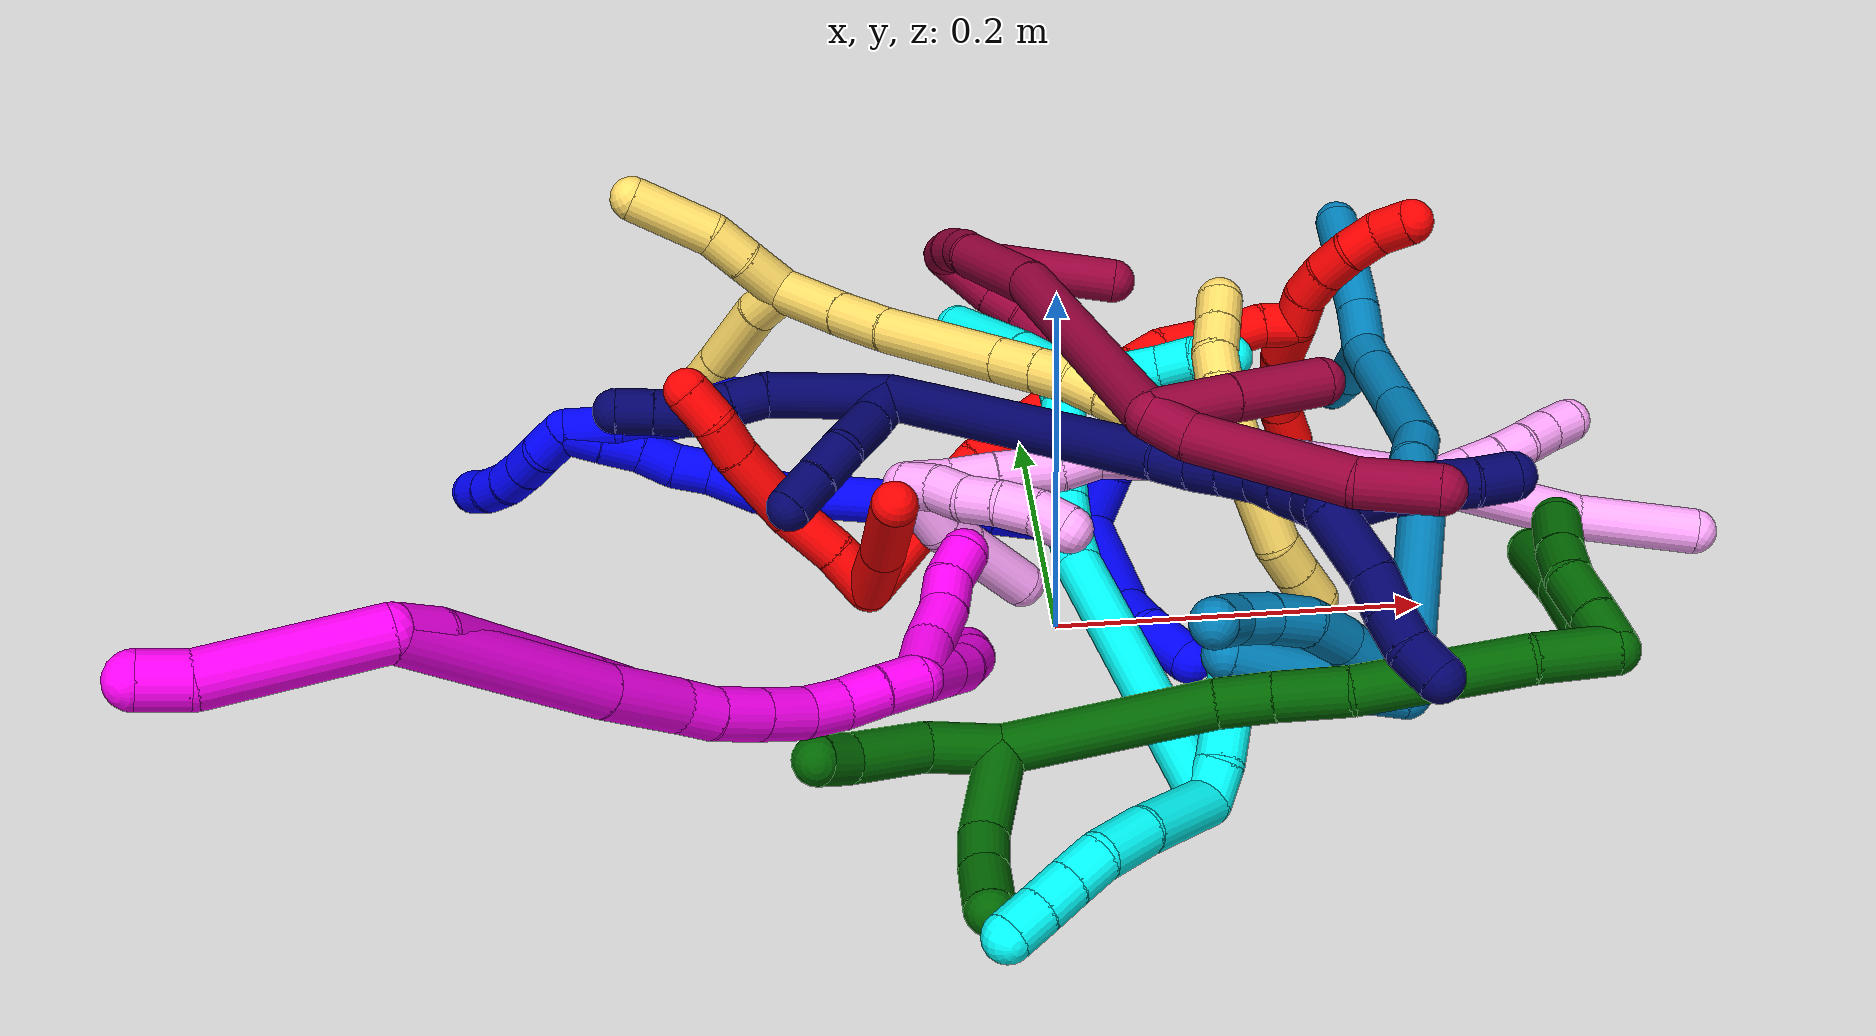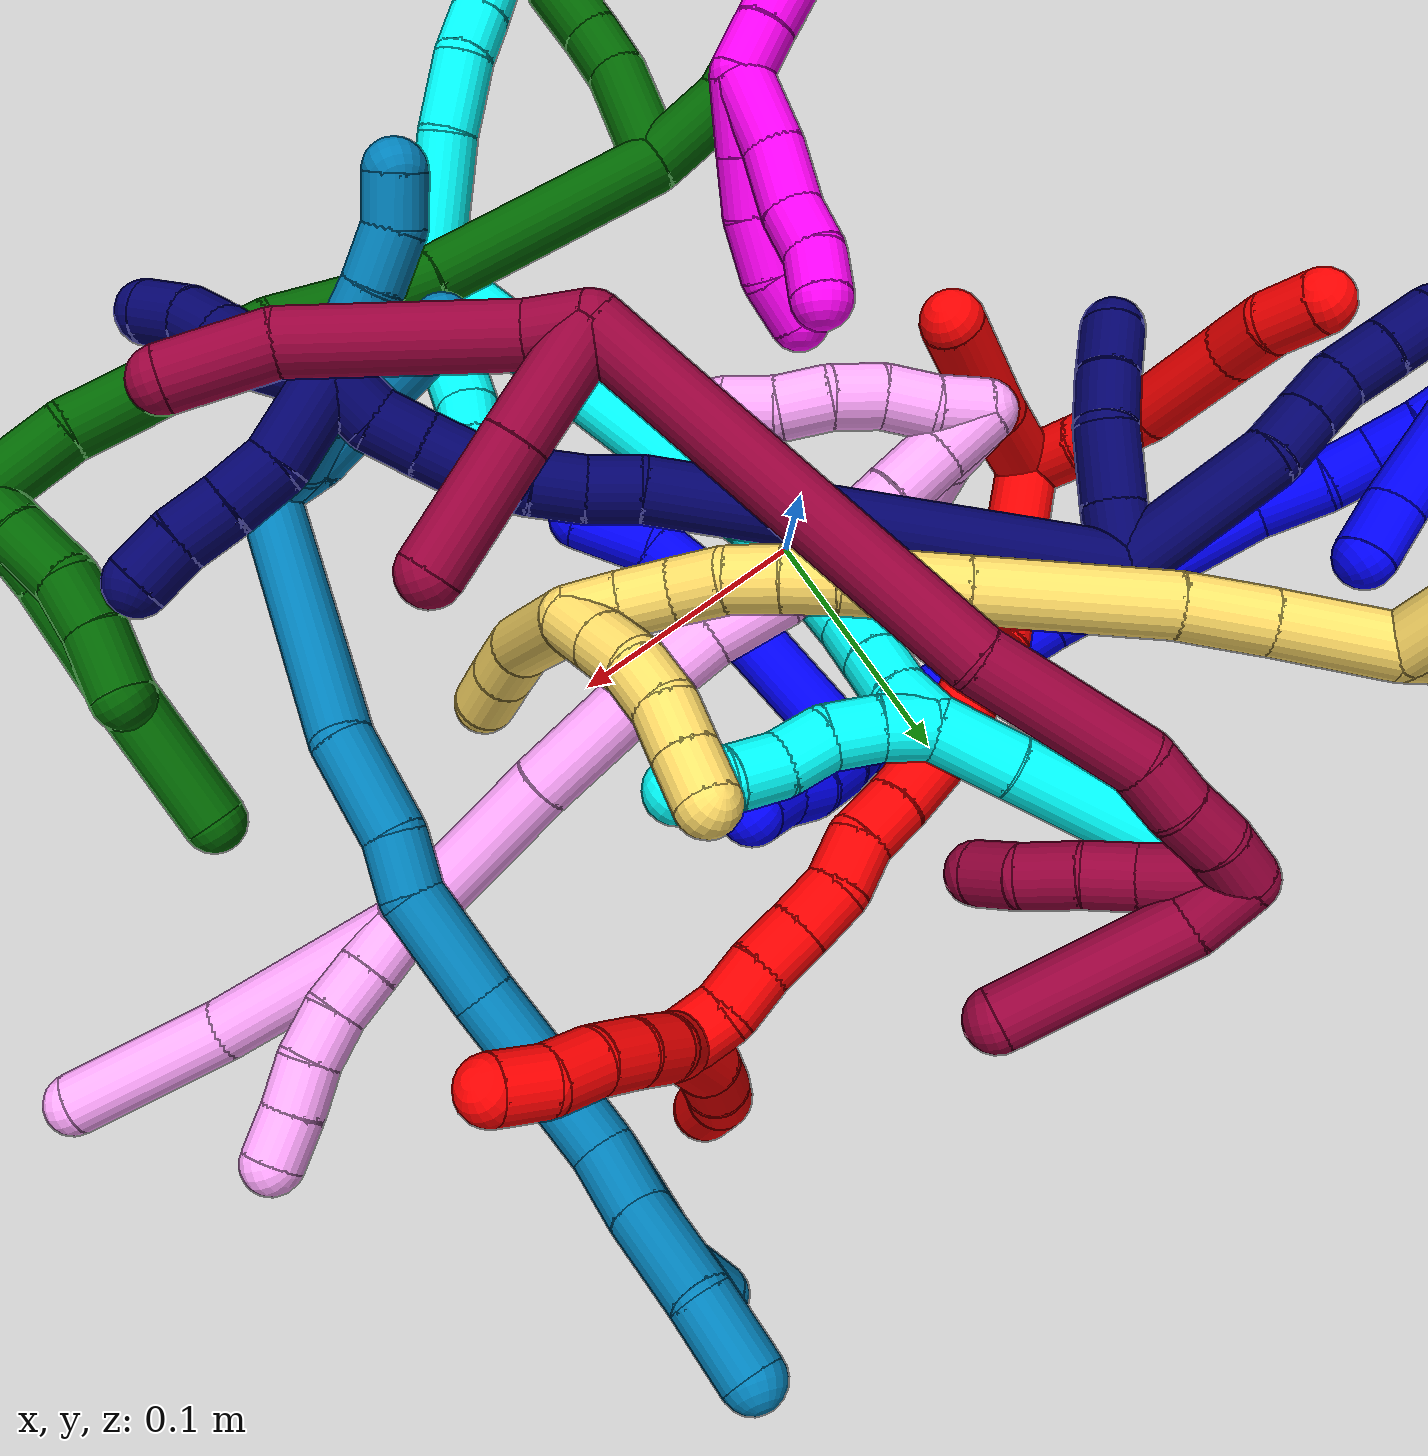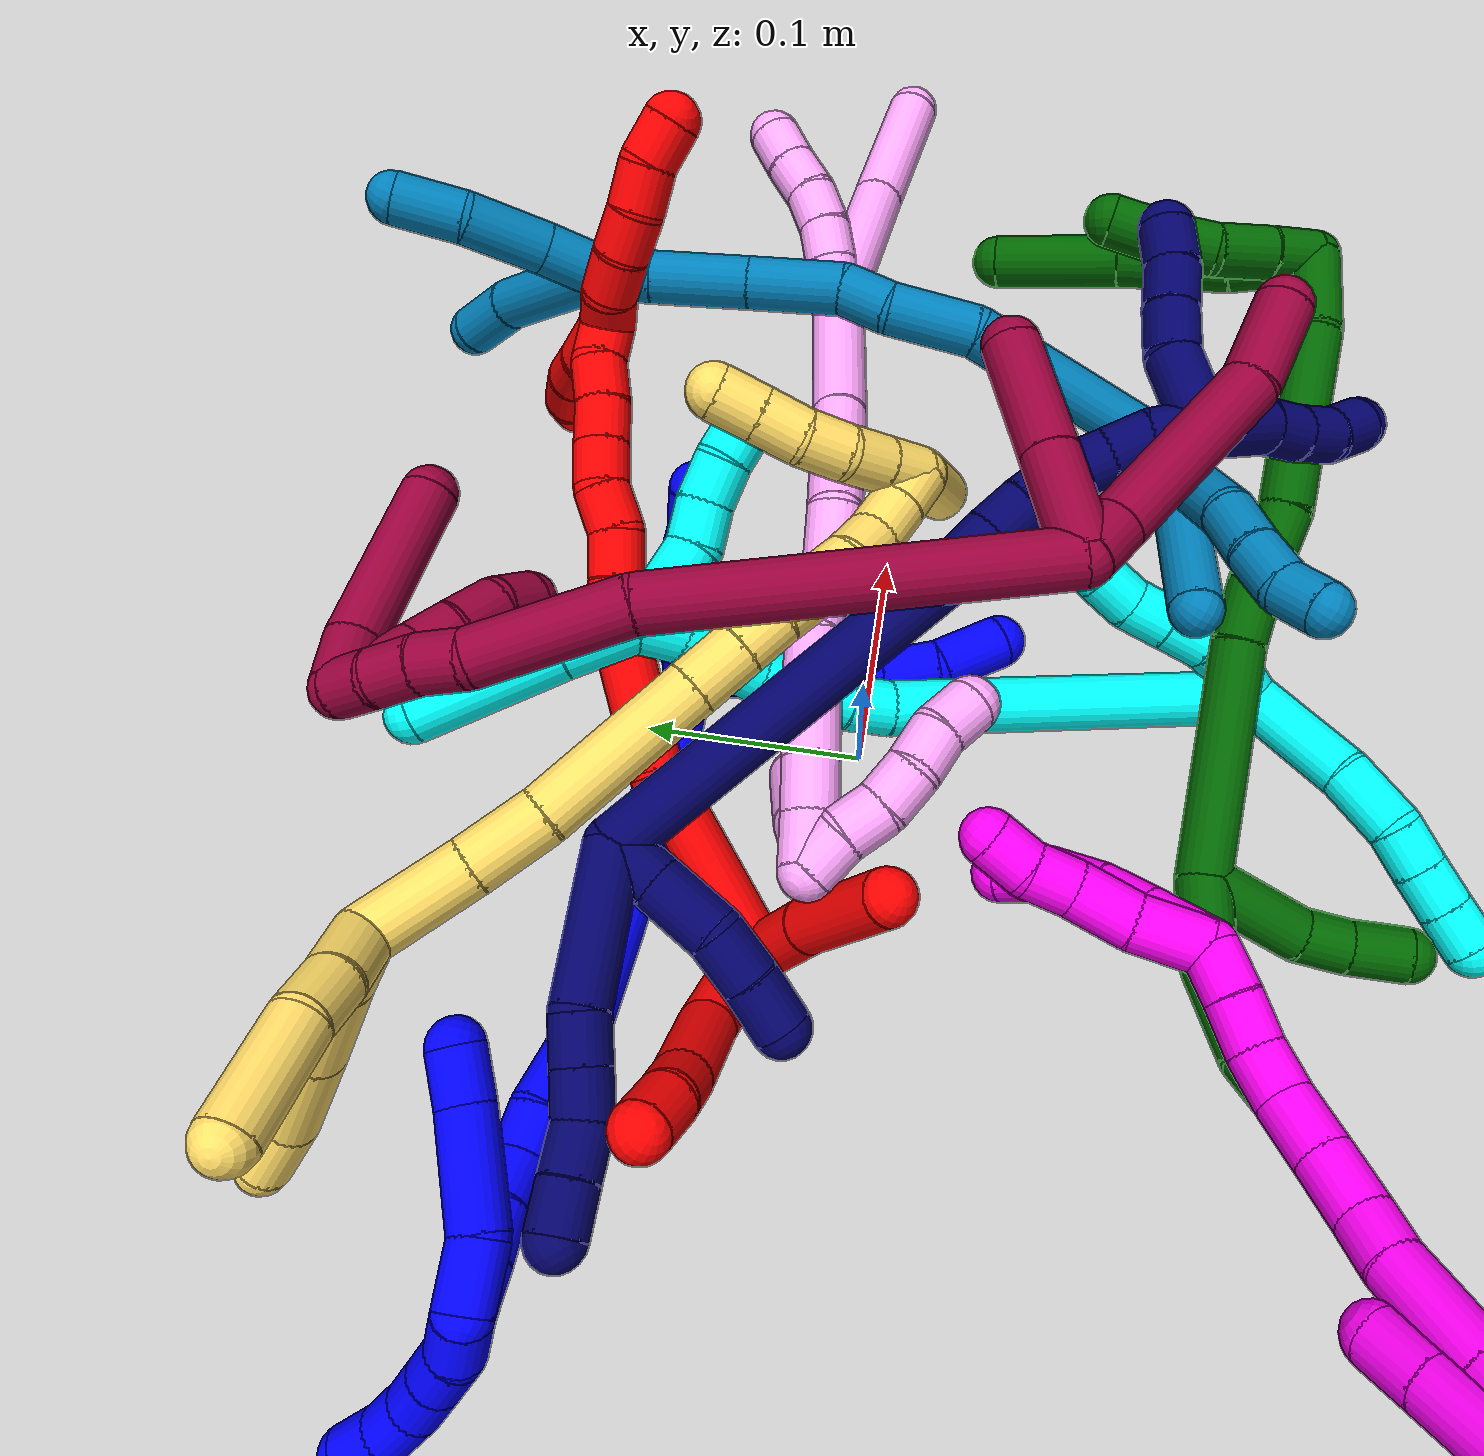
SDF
<sdf version="1.7">
 <world name="default">
  <plugin name="TubeGeneratorPlugin" filename="libtube_generator_plugin.so"/>
  <model name="photoneo_s_sensor">
   <static>1</static>
   <pose>0 0 2 1.57079 1.57079 3.14159</pose>
   <link name="link">
    <inertial><mass>0.1</mass></inertial>
    <sensor name="sensor" type="depth">
     <update_rate>30</update_rate>
     <camera>
      <horizontal_fov>1.22</horizontal_fov>
      <image><width>1920</width><height>1200</height><format>B8G8R8</format></image>
      <clip><near>0.1</near><far>4</far></clip>
      <depth_camera><output>points</output></depth_camera>
     </camera>
     <plugin name="camera_plugin" filename="libgazebo_ros_depth_camera.so">
      <baseline>0.2</baseline>
      <alwaysOn>1</alwaysOn>
      <updateRate>0.0</updateRate>
      <cameraName>camera_ir</cameraName>
      <imageTopicName>/camera/color/image_raw</imageTopicName>
      <cameraInfoTopicName>/camera/color/camera_info</cameraInfoTopicName>
      <depthImageTopicName>/camera/depth/image_raw</depthImageTopicName>
      <depthImageCameraInfoTopicName>/camera/depth/camera_info</depthImageCameraInfoTopicName>
      <pointCloudTopicName>/camera/depth/points</pointCloudTopicName>
      <frameName>fr_optical</frameName>
      <pointCloudCutoff>0.1</pointCloudCutoff>
      <pointCloudCutoffMax>2.0</pointCloudCutoffMax>
      <distortionK1>0</distortionK1>
      <distortionK2>0</distortionK2>
      <distortionK3>0</distortionK3>
      <distortionT1>0</distortionT1>
      <distortionT2>0</distortionT2>
      <CxPrime>0</CxPrime>
      <Cx>0</Cx>
      <Cy>0</Cy>
      <focalLength>0</focalLength>
      <hackBaseline>0</hackBaseline>
     </plugin>
    </sensor>
   </link>
  </model>
  <gravity>0 0 -9.8</gravity>
  <magnetic_field>6e-06 2.3e-05 -4.2e-05</magnetic_field>
  <atmosphere type="adiabatic"/>
  <physics name="default_physics" default="0" type="ode">
   <max_step_size>0.003</max_step_size>
   <real_time_factor>1</real_time_factor>
   <real_time_update_rate>1000</real_time_update_rate>
   <max_contacts>10000</max_contacts>
   <ode>
    <solver>
     <type>quick</type>
     <iters>100</iters>
     <sor>1.3</sor>
     <use_dynamic_moi_rescaling>0</use_dynamic_moi_rescaling>
    </solver>
    <constraints>
     <contact_max_correcting_vel>0</contact_max_correcting_vel>
     <contact_surface_layer>0.001</contact_surface_layer>
     <cfm>0</cfm>
     <erp>0.2</erp>
    </constraints>
   </ode>
  </physics>
  <scene><ambient>0.4 0.4 0.4 1</ambient><background>0.7 0.7 0.7 1</background><shadows>0</shadows></scene>
  <audio><device>default</device></audio>
  <spherical_coordinates>
   <surface_model>EARTH_WGS84</surface_model>
   <latitude_deg>0</latitude_deg>
   <longitude_deg>0</longitude_deg>
   <elevation>0</elevation>
   <heading_deg>0</heading_deg>
  </spherical_coordinates>
  <model name="bin">
   <static>1</static>
   <link name="bottom">
    <collision name="collision-bottom">
     <pose>0 0 -0.01 0 -0 0</pose>
     <geometry><box><size>0.8 0.6 0.02</size></box></geometry>
     <surface>
      <friction><ode><mu>100</mu><mu2>100</mu2></ode></friction>
      <contact><collide_bitmask>65535</collide_bitmask></contact>
     </surface>
    </collision>
   </link>
   <link name="west_wall">
    <collision name="collision-west_wall">
     <pose>-0.41 0 0.1 0 -0 0</pose>
     <geometry><box><size>0.02 0.6 0.2</size></box></geometry>
     <surface>
      <friction><ode><mu>100</mu><mu2>100</mu2></ode></friction>
      <contact><collide_bitmask>65535</collide_bitmask></contact>
     </surface>
    </collision>
   </link>
   <link name="east_wall">
    <collision name="collision-east_wall">
     <pose>0.41 0 0.1 0 -0 0</pose>
     <geometry><box><size>0.02 0.6 0.2</size></box></geometry>
     <surface>
      <friction><ode><mu>100</mu><mu2>100</mu2></ode></friction>
      <contact><collide_bitmask>65535</collide_bitmask></contact>
     </surface>
    </collision>
   </link>
   <link name="south_wall">
    <collision name="collision-south_wall">
     <pose>0 -0.31 0.1 0 -0 0</pose>
     <geometry><box><size>0.8 0.02 0.2</size></box></geometry>
     <surface>
      <friction><ode><mu>100</mu><mu2>100</mu2></ode></friction>
      <contact><collide_bitmask>65535</collide_bitmask></contact>
     </surface>
    </collision>
   </link>
   <link name="north_wall">
    <collision name="collision-north_wall">
     <pose>0 0.31 0.1 0 -0 0</pose>
     <geometry><box><size>0.8 0.02 0.2</size></box></geometry>
     <surface>
      <friction><ode><mu>100</mu><mu2>100</mu2></ode></friction>
      <contact><collide_bitmask>65535</collide_bitmask></contact>
     </surface>
    </collision>
   </link>
  </model>
  <model name="1">
   <static>0</static>
   <link name="1">
    <collision name="collision-cylinder-e_1_2_8">
     <pose>0.026461 -0.037027 -0.004909 1.70261 0.616372 0.696981</pose>
     <geometry><cylinder><radius>0.0125</radius><length>0.091549</length></cylinder></geometry>
     <surface>
      <friction><ode><mu>1.16</mu><mu2>1.16</mu2><slip1>0</slip1><slip2>0</slip2></ode></friction>
      <contact><ode><kp>1e+06</kp><kd>1</kd><max_vel>0</max_vel><min_depth>0.001</min_depth></ode></contact>
     </surface>
    </collision>
    <visual name="visual-cylinder-e_1_2_8">
     <pose>0.026461 -0.037027 -0.004909 1.70261 0.616372 0.696981</pose>
     <geometry><cylinder><radius>0.0125</radius><length>0.091549</length></cylinder></geometry>
     <material><ambient>0 0 1 1</ambient></material>
    </visual>
    <collision name="collision-cylinder-e_2_8_9">
     <pose>0.061632 -0.083363 -0.0134 1.93809 0.717813 1.00001</pose>
     <geometry><cylinder><radius>0.0125</radius><length>0.026485</length></cylinder></geometry>
     <surface>
      <friction><ode><mu>1.16</mu><mu2>1.16</mu2><slip1>0</slip1><slip2>0</slip2></ode></friction>
      <contact><ode><kp>1e+06</kp><kd>1</kd><max_vel>0</max_vel><min_depth>0.001</min_depth></ode></contact>
     </surface>
    </collision>
    <visual name="visual-cylinder-e_2_8_9">
     <pose>0.061632 -0.083363 -0.0134 1.93809 0.717813 1.00001</pose>
     <geometry><cylinder><radius>0.0125</radius><length>0.026485</length></cylinder></geometry>
     <material><ambient>0 0 1 1</ambient></material>
    </visual>
    <collision name="collision-cylinder-e_3_9_6">
     <pose>0.077987 -0.103526 -0.025884 2.25773 0.498688 0.987476</pose>
     <geometry><cylinder><radius>0.0125</radius><length>0.031967</length></cylinder></geometry>
     <surface>
      <friction><ode><mu>1.16</mu><mu2>1.16</mu2><slip1>0</slip1><slip2>0</slip2></ode></friction>
      <contact><ode><kp>1e+06</kp><kd>1</kd><max_vel>0</max_vel><min_depth>0.001</min_depth></ode></contact>
     </surface>
    </collision>
    <visual name="visual-cylinder-e_3_9_6">
     <pose>0.077987 -0.103526 -0.025884 2.25773 0.498688 0.987476</pose>
     <geometry><cylinder><radius>0.0125</radius><length>0.031967</length></cylinder></geometry>
     <material><ambient>0 0 1 1</ambient></material>
    </visual>
    <collision name="collision-cylinder-e_1_2_10">
     <pose>0.013766 0.010976 -0.0036 -1.8877 0.872658 -1.14382</pose>
     <geometry><cylinder><radius>0.0125</radius><length>0.035941</length></cylinder></geometry>
     <surface>
      <friction><ode><mu>1.16</mu><mu2>1.16</mu2><slip1>0</slip1><slip2>0</slip2></ode></friction>
      <contact><ode><kp>1e+06</kp><kd>1</kd><max_vel>0</max_vel><min_depth>0.001</min_depth></ode></contact>
     </surface>
    </collision>
    <visual name="visual-cylinder-e_1_2_10">
     <pose>0.013766 0.010976 -0.0036 -1.8877 0.872658 -1.14382</pose>
     <geometry><cylinder><radius>0.0125</radius><length>0.035941</length></cylinder></geometry>
     <material><ambient>0 0 1 1</ambient></material>
    </visual>
    <collision name="collision-cylinder-e_2_10_11">
     <pose>0.03597 0.028078 -0.01259 -2.29244 0.802138 -1.50686</pose>
     <geometry><cylinder><radius>0.0125</radius><length>0.023476</length></cylinder></geometry>
     <surface>
      <friction><ode><mu>1.16</mu><mu2>1.16</mu2><slip1>0</slip1><slip2>0</slip2></ode></friction>
      <contact><ode><kp>1e+06</kp><kd>1</kd><max_vel>0</max_vel><min_depth>0.001</min_depth></ode></contact>
     </surface>
    </collision>
    <visual name="visual-cylinder-e_2_10_11">
     <pose>0.03597 0.028078 -0.01259 -2.29244 0.802138 -1.50686</pose>
     <geometry><cylinder><radius>0.0125</radius><length>0.023476</length></cylinder></geometry>
     <material><ambient>0 0 1 1</ambient></material>
    </visual>
    <collision name="collision-cylinder-e_3_11_12">
     <pose>0.05263 0.037373 -0.023142 -2.59093 0.935875 -2.12214</pose>
     <geometry><cylinder><radius>0.0125</radius><length>0.020426</length></cylinder></geometry>
     <surface>
      <friction><ode><mu>1.16</mu><mu2>1.16</mu2><slip1>0</slip1><slip2>0</slip2></ode></friction>
      <contact><ode><kp>1e+06</kp><kd>1</kd><max_vel>0</max_vel><min_depth>0.001</min_depth></ode></contact>
     </surface>
    </collision>
    <visual name="visual-cylinder-e_3_11_12">
     <pose>0.05263 0.037373 -0.023142 -2.59093 0.935875 -2.12214</pose>
     <geometry><cylinder><radius>0.0125</radius><length>0.020426</length></cylinder></geometry>
     <material><ambient>0 0 1 1</ambient></material>
    </visual>
    <collision name="collision-cylinder-e_4_12_5">
     <pose>0.068087 0.045539 -0.033233 -2.34931 0.800547 -1.58235</pose>
     <geometry><cylinder><radius>0.0125</radius><length>0.020158</length></cylinder></geometry>
     <surface>
      <friction><ode><mu>1.16</mu><mu2>1.16</mu2><slip1>0</slip1><slip2>0</slip2></ode></friction>
      <contact><ode><kp>1e+06</kp><kd>1</kd><max_vel>0</max_vel><min_depth>0.001</min_depth></ode></contact>
     </surface>
    </collision>
    <visual name="visual-cylinder-e_4_12_5">
     <pose>0.068087 0.045539 -0.033233 -2.34931 0.800547 -1.58235</pose>
     <geometry><cylinder><radius>0.0125</radius><length>0.020158</length></cylinder></geometry>
     <material><ambient>0 0 1 1</ambient></material>
    </visual>
    <collision name="collision-cylinder-e_1_2_13">
     <pose>0.000174 0.000601 0.027975 -0.021477 0.006202 -6.7e-05</pose>
     <geometry><cylinder><radius>0.0125</radius><length>0.055965</length></cylinder></geometry>
     <surface>
      <friction><ode><mu>1.16</mu><mu2>1.16</mu2><slip1>0</slip1><slip2>0</slip2></ode></friction>
      <contact><ode><kp>1e+06</kp><kd>1</kd><max_vel>0</max_vel><min_depth>0.001</min_depth></ode></contact>
     </surface>
    </collision>
    <visual name="visual-cylinder-e_1_2_13">
     <pose>0.000174 0.000601 0.027975 -0.021477 0.006202 -6.7e-05</pose>
     <geometry><cylinder><radius>0.0125</radius><length>0.055965</length></cylinder></geometry>
     <material><ambient>0 0 1 1</ambient></material>
    </visual>
    <collision name="collision-cylinder-e_2_13_14">
     <pose>-0.000499 0.001966 0.074976 -0.040153 -0.0444 0.000892</pose>
     <geometry><cylinder><radius>0.0125</radius><length>0.038118</length></cylinder></geometry>
     <surface>
      <friction><ode><mu>1.16</mu><mu2>1.16</mu2><slip1>0</slip1><slip2>0</slip2></ode></friction>
      <contact><ode><kp>1e+06</kp><kd>1</kd><max_vel>0</max_vel><min_depth>0.001</min_depth></ode></contact>
     </surface>
    </collision>
    <visual name="visual-cylinder-e_2_13_14">
     <pose>-0.000499 0.001966 0.074976 -0.040153 -0.0444 0.000892</pose>
     <geometry><cylinder><radius>0.0125</radius><length>0.038118</length></cylinder></geometry>
     <material><ambient>0 0 1 1</ambient></material>
    </visual>
    <collision name="collision-cylinder-e_3_14_15">
     <pose>-0.008195 0.004753 0.139647 -0.04427 -0.148808 0.003301</pose>
     <geometry><cylinder><radius>0.0125</radius><length>0.092403</length></cylinder></geometry>
     <surface>
      <friction><ode><mu>1.16</mu><mu2>1.16</mu2><slip1>0</slip1><slip2>0</slip2></ode></friction>
      <contact><ode><kp>1e+06</kp><kd>1</kd><max_vel>0</max_vel><min_depth>0.001</min_depth></ode></contact>
     </surface>
    </collision>
    <visual name="visual-cylinder-e_3_14_15">
     <pose>-0.008195 0.004753 0.139647 -0.04427 -0.148808 0.003301</pose>
     <geometry><cylinder><radius>0.0125</radius><length>0.092403</length></cylinder></geometry>
     <material><ambient>0 0 1 1</ambient></material>
    </visual>
    <collision name="collision-cylinder-e_4_15_16">
     <pose>-0.01514 0.011345 0.19915 -0.318613 -0.006564 0.001055</pose>
     <geometry><cylinder><radius>0.0125</radius><length>0.029181</length></cylinder></geometry>
     <surface>
      <friction><ode><mu>1.16</mu><mu2>1.16</mu2><slip1>0</slip1><slip2>0</slip2></ode></friction>
      <contact><ode><kp>1e+06</kp><kd>1</kd><max_vel>0</max_vel><min_depth>0.001</min_depth></ode></contact>
     </surface>
    </collision>
    <visual name="visual-cylinder-e_4_15_16">
     <pose>-0.01514 0.011345 0.19915 -0.318613 -0.006564 0.001055</pose>
     <geometry><cylinder><radius>0.0125</radius><length>0.029181</length></cylinder></geometry>
     <material><ambient>0 0 1 1</ambient></material>
    </visual>
    <collision name="collision-cylinder-e_5_16_17">
     <pose>-0.015875 0.017174 0.223287 -0.121772 -0.061598 0.003756</pose>
     <geometry><cylinder><radius>0.0125</radius><length>0.020756</length></cylinder></geometry>
     <surface>
      <friction><ode><mu>1.16</mu><mu2>1.16</mu2><slip1>0</slip1><slip2>0</slip2></ode></friction>
      <contact><ode><kp>1e+06</kp><kd>1</kd><max_vel>0</max_vel><min_depth>0.001</min_depth></ode></contact>
     </surface>
    </collision>
    <visual name="visual-cylinder-e_5_16_17">
     <pose>-0.015875 0.017174 0.223287 -0.121772 -0.061598 0.003756</pose>
     <geometry><cylinder><radius>0.0125</radius><length>0.020756</length></cylinder></geometry>
     <material><ambient>0 0 1 1</ambient></material>
    </visual>
    <collision name="collision-cylinder-e_6_17_18">
     <pose>-0.014685 0.021256 0.243317 -0.281942 0.178255 -0.025362</pose>
     <geometry><cylinder><radius>0.0125</radius><length>0.020625</length></cylinder></geometry>
     <surface>
      <friction><ode><mu>1.16</mu><mu2>1.16</mu2><slip1>0</slip1><slip2>0</slip2></ode></friction>
      <contact><ode><kp>1e+06</kp><kd>1</kd><max_vel>0</max_vel><min_depth>0.001</min_depth></ode></contact>
     </surface>
    </collision>
    <visual name="visual-cylinder-e_6_17_18">
     <pose>-0.014685 0.021256 0.243317 -0.281942 0.178255 -0.025362</pose>
     <geometry><cylinder><radius>0.0125</radius><length>0.020625</length></cylinder></geometry>
     <material><ambient>0 0 1 1</ambient></material>
    </visual>
    <collision name="collision-cylinder-e_7_18_19">
     <pose>-0.011796 0.025139 0.264133 -0.095469 0.09509 -0.004546</pose>
     <geometry><cylinder><radius>0.0125</radius><length>0.022336</length></cylinder></geometry>
     <surface>
      <friction><ode><mu>1.16</mu><mu2>1.16</mu2><slip1>0</slip1><slip2>0</slip2></ode></friction>
      <contact><ode><kp>1e+06</kp><kd>1</kd><max_vel>0</max_vel><min_depth>0.001</min_depth></ode></contact>
     </surface>
    </collision>
    <visual name="visual-cylinder-e_7_18_19">
     <pose>-0.011796 0.025139 0.264133 -0.095469 0.09509 -0.004546</pose>
     <geometry><cylinder><radius>0.0125</radius><length>0.022336</length></cylinder></geometry>
     <material><ambient>0 0 1 1</ambient></material>
    </visual>
    <collision name="collision-cylinder-e_8_19_1">
     <pose>-0.009708 0.027609 0.285358 -0.137914 0.099916 -0.006907</pose>
     <geometry><cylinder><radius>0.0125</radius><length>0.020615</length></cylinder></geometry>
     <surface>
      <friction><ode><mu>1.16</mu><mu2>1.16</mu2><slip1>0</slip1><slip2>0</slip2></ode></friction>
      <contact><ode><kp>1e+06</kp><kd>1</kd><max_vel>0</max_vel><min_depth>0.001</min_depth></ode></contact>
     </surface>
    </collision>
    <visual name="visual-cylinder-e_8_19_1">
     <pose>-0.009708 0.027609 0.285358 -0.137914 0.099916 -0.006907</pose>
     <geometry><cylinder><radius>0.0125</radius><length>0.020615</length></cylinder></geometry>
     <material><ambient>0 0 1 1</ambient></material>
    </visual>
    <collision name="collision-cylinder-e_1_1_20">
     <pose>-0.016314 0.025515 0.300942 0.573416 -0.868662 -0.271842</pose>
     <geometry><cylinder><radius>0.0125</radius><length>0.02</length></cylinder></geometry>
     <surface>
      <friction><ode><mu>1.16</mu><mu2>1.16</mu2><slip1>0</slip1><slip2>0</slip2></ode></friction>
      <contact><ode><kp>1e+06</kp><kd>1</kd><max_vel>0</max_vel><min_depth>0.001</min_depth></ode></contact>
     </surface>
    </collision>
    <visual name="visual-cylinder-e_1_1_20">
     <pose>-0.016314 0.025515 0.300942 0.573416 -0.868662 -0.271842</pose>
     <geometry><cylinder><radius>0.0125</radius><length>0.02</length></cylinder></geometry>
     <material><ambient>0 0 1 1</ambient></material>
    </visual>
    <collision name="collision-cylinder-e_2_20_21">
     <pose>-0.033009 0.020884 0.310447 0.269577 -1.13378 -0.17223</pose>
     <geometry><cylinder><radius>0.0125</radius><length>0.02</length></cylinder></geometry>
     <surface>
      <friction><ode><mu>1.16</mu><mu2>1.16</mu2><slip1>0</slip1><slip2>0</slip2></ode></friction>
      <contact><ode><kp>1e+06</kp><kd>1</kd><max_vel>0</max_vel><min_depth>0.001</min_depth></ode></contact>
     </surface>
    </collision>
    <visual name="visual-cylinder-e_2_20_21">
     <pose>-0.033009 0.020884 0.310447 0.269577 -1.13378 -0.17223</pose>
     <geometry><cylinder><radius>0.0125</radius><length>0.02</length></cylinder></geometry>
     <material><ambient>0 0 1 1</ambient></material>
    </visual>
    <collision name="collision-cylinder-e_3_21_22">
     <pose>-0.05093 0.018993 0.3191 0.165616 -1.08872 -0.100404</pose>
     <geometry><cylinder><radius>0.0125</radius><length>0.02</length></cylinder></geometry>
     <surface>
      <friction><ode><mu>1.16</mu><mu2>1.16</mu2><slip1>0</slip1><slip2>0</slip2></ode></friction>
      <contact><ode><kp>1e+06</kp><kd>1</kd><max_vel>0</max_vel><min_depth>0.001</min_depth></ode></contact>
     </surface>
    </collision>
    <visual name="visual-cylinder-e_3_21_22">
     <pose>-0.05093 0.018993 0.3191 0.165616 -1.08872 -0.100404</pose>
     <geometry><cylinder><radius>0.0125</radius><length>0.02</length></cylinder></geometry>
     <material><ambient>0 0 1 1</ambient></material>
    </visual>
    <collision name="collision-cylinder-e_4_22_23">
     <pose>-0.068375 0.019352 0.328677 -0.220788 -1.03227 0.12563</pose>
     <geometry><cylinder><radius>0.0125</radius><length>0.02</length></cylinder></geometry>
     <surface>
      <friction><ode><mu>1.16</mu><mu2>1.16</mu2><slip1>0</slip1><slip2>0</slip2></ode></friction>
      <contact><ode><kp>1e+06</kp><kd>1</kd><max_vel>0</max_vel><min_depth>0.001</min_depth></ode></contact>
     </surface>
    </collision>
    <visual name="visual-cylinder-e_4_22_23">
     <pose>-0.068375 0.019352 0.328677 -0.220788 -1.03227 0.12563</pose>
     <geometry><cylinder><radius>0.0125</radius><length>0.02</length></cylinder></geometry>
     <material><ambient>0 0 1 1</ambient></material>
    </visual>
    <collision name="collision-cylinder-e_5_23_4">
     <pose>-0.085345 0.023652 0.338106 -0.622657 -0.994644 0.345868</pose>
     <geometry><cylinder><radius>0.0125</radius><length>0.02</length></cylinder></geometry>
     <surface>
      <friction><ode><mu>1.16</mu><mu2>1.16</mu2><slip1>0</slip1><slip2>0</slip2></ode></friction>
      <contact><ode><kp>1e+06</kp><kd>1</kd><max_vel>0</max_vel><min_depth>0.001</min_depth></ode></contact>
     </surface>
    </collision>
    <visual name="visual-cylinder-e_5_23_4">
     <pose>-0.085345 0.023652 0.338106 -0.622657 -0.994644 0.345868</pose>
     <geometry><cylinder><radius>0.0125</radius><length>0.02</length></cylinder></geometry>
     <material><ambient>0 0 1 1</ambient></material>
    </visual>
    <collision name="collision-cylinder-e_1_1_24">
     <pose>-0.006587 0.030545 0.281926 -3.02978 0.151828 -1.87294</pose>
     <geometry><cylinder><radius>0.0125</radius><length>0.02767</length></cylinder></geometry>
     <surface>
      <friction><ode><mu>1.16</mu><mu2>1.16</mu2><slip1>0</slip1><slip2>0</slip2></ode></friction>
      <contact><ode><kp>1e+06</kp><kd>1</kd><max_vel>0</max_vel><min_depth>0.001</min_depth></ode></contact>
     </surface>
    </collision>
    <visual name="visual-cylinder-e_1_1_24">
     <pose>-0.006587 0.030545 0.281926 -3.02978 0.151828 -1.87294</pose>
     <geometry><cylinder><radius>0.0125</radius><length>0.02767</length></cylinder></geometry>
     <material><ambient>0 0 1 1</ambient></material>
    </visual>
    <collision name="collision-cylinder-e_2_24_25">
     <pose>-0.00635 0.040621 0.245595 -2.78194 -0.076229 0.413535</pose>
     <geometry><cylinder><radius>0.0125</radius><length>0.048732</length></cylinder></geometry>
     <surface>
      <friction><ode><mu>1.16</mu><mu2>1.16</mu2><slip1>0</slip1><slip2>0</slip2></ode></friction>
      <contact><ode><kp>1e+06</kp><kd>1</kd><max_vel>0</max_vel><min_depth>0.001</min_depth></ode></contact>
     </surface>
    </collision>
    <visual name="visual-cylinder-e_2_24_25">
     <pose>-0.00635 0.040621 0.245595 -2.78194 -0.076229 0.413535</pose>
     <geometry><cylinder><radius>0.0125</radius><length>0.048732</length></cylinder></geometry>
     <material><ambient>0 0 1 1</ambient></material>
    </visual>
    <collision name="collision-cylinder-e_3_25_3">
     <pose>-0.007919 0.054544 0.212353 -2.66873 0.024267 -0.100637</pose>
     <geometry><cylinder><radius>0.0125</radius><length>0.023598</length></cylinder></geometry>
     <surface>
      <friction><ode><mu>1.16</mu><mu2>1.16</mu2><slip1>0</slip1><slip2>0</slip2></ode></friction>
      <contact><ode><kp>1e+06</kp><kd>1</kd><max_vel>0</max_vel><min_depth>0.001</min_depth></ode></contact>
     </surface>
    </collision>
    <visual name="visual-cylinder-e_3_25_3">
     <pose>-0.007919 0.054544 0.212353 -2.66873 0.024267 -0.100637</pose>
     <geometry><cylinder><radius>0.0125</radius><length>0.023598</length></cylinder></geometry>
     <material><ambient>0 0 1 1</ambient></material>
    </visual>
    <collision name="collision-sphere-3">
     <pose>-0.007633 0.059916 0.201852 0 -0 0</pose>
     <geometry><sphere><radius>0.0125</radius></sphere></geometry>
     <surface>
      <friction><ode><mu>1.16</mu><mu2>1.16</mu2><slip1>0</slip1><slip2>0</slip2></ode></friction>
      <contact><ode><kp>1e+06</kp><kd>1</kd><max_vel>0</max_vel><min_depth>0.001</min_depth></ode></contact>
     </surface>
    </collision>
    <visual name="visual-sphere-3">
     <pose>-0.007633 0.059916 0.201852 0 -0 0</pose>
     <geometry><sphere><radius>0.0125</radius></sphere></geometry>
     <material><ambient>0 0 1 1</ambient></material>
    </visual>
    <collision name="collision-sphere-25">
     <pose>-0.008206 0.049172 0.222854 0 -0 0</pose>
     <geometry><sphere><radius>0.0125</radius></sphere></geometry>
     <surface>
      <friction><ode><mu>1.16</mu><mu2>1.16</mu2><slip1>0</slip1><slip2>0</slip2></ode></friction>
      <contact><ode><kp>1e+06</kp><kd>1</kd><max_vel>0</max_vel><min_depth>0.001</min_depth></ode></contact>
     </surface>
    </collision>
    <visual name="visual-sphere-25">
     <pose>-0.008206 0.049172 0.222854 0 -0 0</pose>
     <geometry><sphere><radius>0.0125</radius></sphere></geometry>
     <material><ambient>0 0 1 1</ambient></material>
    </visual>
    <collision name="collision-sphere-24">
     <pose>-0.004495 0.032071 0.268336 0 -0 0</pose>
     <geometry><sphere><radius>0.0125</radius></sphere></geometry>
     <surface>
      <friction><ode><mu>1.16</mu><mu2>1.16</mu2><slip1>0</slip1><slip2>0</slip2></ode></friction>
      <contact><ode><kp>1e+06</kp><kd>1</kd><max_vel>0</max_vel><min_depth>0.001</min_depth></ode></contact>
     </surface>
    </collision>
    <visual name="visual-sphere-24">
     <pose>-0.004495 0.032071 0.268336 0 -0 0</pose>
     <geometry><sphere><radius>0.0125</radius></sphere></geometry>
     <material><ambient>0 0 1 1</ambient></material>
    </visual>
    <collision name="collision-sphere-4">
     <pose>-0.093731 0.026829 0.342532 0 -0 0</pose>
     <geometry><sphere><radius>0.0125</radius></sphere></geometry>
     <surface>
      <friction><ode><mu>1.16</mu><mu2>1.16</mu2><slip1>0</slip1><slip2>0</slip2></ode></friction>
      <contact><ode><kp>1e+06</kp><kd>1</kd><max_vel>0</max_vel><min_depth>0.001</min_depth></ode></contact>
     </surface>
    </collision>
    <visual name="visual-sphere-4">
     <pose>-0.093731 0.026829 0.342532 0 -0 0</pose>
     <geometry><sphere><radius>0.0125</radius></sphere></geometry>
     <material><ambient>0 0 1 1</ambient></material>
    </visual>
    <collision name="collision-sphere-23">
     <pose>-0.076959 0.020475 0.333681 0 -0 0</pose>
     <geometry><sphere><radius>0.0125</radius></sphere></geometry>
     <surface>
      <friction><ode><mu>1.16</mu><mu2>1.16</mu2><slip1>0</slip1><slip2>0</slip2></ode></friction>
      <contact><ode><kp>1e+06</kp><kd>1</kd><max_vel>0</max_vel><min_depth>0.001</min_depth></ode></contact>
     </surface>
    </collision>
    <visual name="visual-sphere-23">
     <pose>-0.076959 0.020475 0.333681 0 -0 0</pose>
     <geometry><sphere><radius>0.0125</radius></sphere></geometry>
     <material><ambient>0 0 1 1</ambient></material>
    </visual>
    <collision name="collision-sphere-22">
     <pose>-0.05979 0.018229 0.323672 0 -0 0</pose>
     <geometry><sphere><radius>0.0125</radius></sphere></geometry>
     <surface>
      <friction><ode><mu>1.16</mu><mu2>1.16</mu2><slip1>0</slip1><slip2>0</slip2></ode></friction>
      <contact><ode><kp>1e+06</kp><kd>1</kd><max_vel>0</max_vel><min_depth>0.001</min_depth></ode></contact>
     </surface>
    </collision>
    <visual name="visual-sphere-22">
     <pose>-0.05979 0.018229 0.323672 0 -0 0</pose>
     <geometry><sphere><radius>0.0125</radius></sphere></geometry>
     <material><ambient>0 0 1 1</ambient></material>
    </visual>
    <collision name="collision-sphere-21">
     <pose>-0.042069 0.019757 0.314527 0 -0 0</pose>
     <geometry><sphere><radius>0.0125</radius></sphere></geometry>
     <surface>
      <friction><ode><mu>1.16</mu><mu2>1.16</mu2><slip1>0</slip1><slip2>0</slip2></ode></friction>
      <contact><ode><kp>1e+06</kp><kd>1</kd><max_vel>0</max_vel><min_depth>0.001</min_depth></ode></contact>
     </surface>
    </collision>
    <visual name="visual-sphere-21">
     <pose>-0.042069 0.019757 0.314527 0 -0 0</pose>
     <geometry><sphere><radius>0.0125</radius></sphere></geometry>
     <material><ambient>0 0 1 1</ambient></material>
    </visual>
    <collision name="collision-sphere-20">
     <pose>-0.023949 0.022012 0.306368 0 -0 0</pose>
     <geometry><sphere><radius>0.0125</radius></sphere></geometry>
     <surface>
      <friction><ode><mu>1.16</mu><mu2>1.16</mu2><slip1>0</slip1><slip2>0</slip2></ode></friction>
      <contact><ode><kp>1e+06</kp><kd>1</kd><max_vel>0</max_vel><min_depth>0.001</min_depth></ode></contact>
     </surface>
    </collision>
    <visual name="visual-sphere-20">
     <pose>-0.023949 0.022012 0.306368 0 -0 0</pose>
     <geometry><sphere><radius>0.0125</radius></sphere></geometry>
     <material><ambient>0 0 1 1</ambient></material>
    </visual>
    <collision name="collision-sphere-11">
     <pose>0.044407 0.034204 -0.01798 0 -0 0</pose>
     <geometry><sphere><radius>0.0125</radius></sphere></geometry>
     <surface>
      <friction><ode><mu>1.16</mu><mu2>1.16</mu2><slip1>0</slip1><slip2>0</slip2></ode></friction>
      <contact><ode><kp>1e+06</kp><kd>1</kd><max_vel>0</max_vel><min_depth>0.001</min_depth></ode></contact>
     </surface>
    </collision>
    <visual name="visual-sphere-11">
     <pose>0.044407 0.034204 -0.01798 0 -0 0</pose>
     <geometry><sphere><radius>0.0125</radius></sphere></geometry>
     <material><ambient>0 0 1 1</ambient></material>
    </visual>
    <collision name="collision-sphere-10">
     <pose>0.027532 0.021952 -0.007199 0 -0 0</pose>
     <geometry><sphere><radius>0.0125</radius></sphere></geometry>
     <surface>
      <friction><ode><mu>1.16</mu><mu2>1.16</mu2><slip1>0</slip1><slip2>0</slip2></ode></friction>
      <contact><ode><kp>1e+06</kp><kd>1</kd><max_vel>0</max_vel><min_depth>0.001</min_depth></ode></contact>
     </surface>
    </collision>
    <visual name="visual-sphere-10">
     <pose>0.027532 0.021952 -0.007199 0 -0 0</pose>
     <geometry><sphere><radius>0.0125</radius></sphere></geometry>
     <material><ambient>0 0 1 1</ambient></material>
    </visual>
    <collision name="collision-sphere-6">
     <pose>0.085631 -0.114379 -0.034785 0 -0 0</pose>
     <geometry><sphere><radius>0.0125</radius></sphere></geometry>
     <surface>
      <friction><ode><mu>1.16</mu><mu2>1.16</mu2><slip1>0</slip1><slip2>0</slip2></ode></friction>
      <contact><ode><kp>1e+06</kp><kd>1</kd><max_vel>0</max_vel><min_depth>0.001</min_depth></ode></contact>
     </surface>
    </collision>
    <visual name="visual-sphere-6">
     <pose>0.085631 -0.114379 -0.034785 0 -0 0</pose>
     <geometry><sphere><radius>0.0125</radius></sphere></geometry>
     <material><ambient>0 0 1 1</ambient></material>
    </visual>
    <collision name="collision-sphere-9">
     <pose>0.070342 -0.092673 -0.016982 0 -0 0</pose>
     <geometry><sphere><radius>0.0125</radius></sphere></geometry>
     <surface>
      <friction><ode><mu>1.16</mu><mu2>1.16</mu2><slip1>0</slip1><slip2>0</slip2></ode></friction>
      <contact><ode><kp>1e+06</kp><kd>1</kd><max_vel>0</max_vel><min_depth>0.001</min_depth></ode></contact>
     </surface>
    </collision>
    <visual name="visual-sphere-9">
     <pose>0.070342 -0.092673 -0.016982 0 -0 0</pose>
     <geometry><sphere><radius>0.0125</radius></sphere></geometry>
     <material><ambient>0 0 1 1</ambient></material>
    </visual>
    <collision name="collision-sphere-2">
     <geometry><sphere><radius>0.0125</radius></sphere></geometry>
     <surface>
      <friction><ode><mu>1.16</mu><mu2>1.16</mu2><slip1>0</slip1><slip2>0</slip2></ode></friction>
      <contact><ode><kp>1e+06</kp><kd>1</kd><max_vel>0</max_vel><min_depth>0.001</min_depth></ode></contact>
     </surface>
    </collision>
    <visual name="visual-sphere-2">
     <geometry><sphere><radius>0.0125</radius></sphere></geometry>
     <material><ambient>0 0 1 1</ambient></material>
    </visual>
    <collision name="collision-sphere-19">
     <pose>-0.010736 0.026199 0.2752 0 -0 0</pose>
     <geometry><sphere><radius>0.0125</radius></sphere></geometry>
     <surface>
      <friction><ode><mu>1.16</mu><mu2>1.16</mu2><slip1>0</slip1><slip2>0</slip2></ode></friction>
      <contact><ode><kp>1e+06</kp><kd>1</kd><max_vel>0</max_vel><min_depth>0.001</min_depth></ode></contact>
     </surface>
    </collision>
    <visual name="visual-sphere-19">
     <pose>-0.010736 0.026199 0.2752 0 -0 0</pose>
     <geometry><sphere><radius>0.0125</radius></sphere></geometry>
     <material><ambient>0 0 1 1</ambient></material>
    </visual>
    <collision name="collision-sphere-8">
     <pose>0.052922 -0.074054 -0.009818 0 -0 0</pose>
     <geometry><sphere><radius>0.0125</radius></sphere></geometry>
     <surface>
      <friction><ode><mu>1.16</mu><mu2>1.16</mu2><slip1>0</slip1><slip2>0</slip2></ode></friction>
      <contact><ode><kp>1e+06</kp><kd>1</kd><max_vel>0</max_vel><min_depth>0.001</min_depth></ode></contact>
     </surface>
    </collision>
    <visual name="visual-sphere-8">
     <pose>0.052922 -0.074054 -0.009818 0 -0 0</pose>
     <geometry><sphere><radius>0.0125</radius></sphere></geometry>
     <material><ambient>0 0 1 1</ambient></material>
    </visual>
    <collision name="collision-sphere-12">
     <pose>0.060853 0.040543 -0.028304 0 -0 0</pose>
     <geometry><sphere><radius>0.0125</radius></sphere></geometry>
     <surface>
      <friction><ode><mu>1.16</mu><mu2>1.16</mu2><slip1>0</slip1><slip2>0</slip2></ode></friction>
      <contact><ode><kp>1e+06</kp><kd>1</kd><max_vel>0</max_vel><min_depth>0.001</min_depth></ode></contact>
     </surface>
    </collision>
    <visual name="visual-sphere-12">
     <pose>0.060853 0.040543 -0.028304 0 -0 0</pose>
     <geometry><sphere><radius>0.0125</radius></sphere></geometry>
     <material><ambient>0 0 1 1</ambient></material>
    </visual>
    <collision name="collision-sphere-5">
     <pose>0.075321 0.050536 -0.038161 0 -0 0</pose>
     <geometry><sphere><radius>0.0125</radius></sphere></geometry>
     <surface>
      <friction><ode><mu>1.16</mu><mu2>1.16</mu2><slip1>0</slip1><slip2>0</slip2></ode></friction>
      <contact><ode><kp>1e+06</kp><kd>1</kd><max_vel>0</max_vel><min_depth>0.001</min_depth></ode></contact>
     </surface>
    </collision>
    <visual name="visual-sphere-5">
     <pose>0.075321 0.050536 -0.038161 0 -0 0</pose>
     <geometry><sphere><radius>0.0125</radius></sphere></geometry>
     <material><ambient>0 0 1 1</ambient></material>
    </visual>
    <collision name="collision-sphere-13">
     <pose>0.000347 0.001202 0.055951 0 -0 0</pose>
     <geometry><sphere><radius>0.0125</radius></sphere></geometry>
     <surface>
      <friction><ode><mu>1.16</mu><mu2>1.16</mu2><slip1>0</slip1><slip2>0</slip2></ode></friction>
      <contact><ode><kp>1e+06</kp><kd>1</kd><max_vel>0</max_vel><min_depth>0.001</min_depth></ode></contact>
     </surface>
    </collision>
    <visual name="visual-sphere-13">
     <pose>0.000347 0.001202 0.055951 0 -0 0</pose>
     <geometry><sphere><radius>0.0125</radius></sphere></geometry>
     <material><ambient>0 0 1 1</ambient></material>
    </visual>
    <collision name="collision-sphere-14">
     <pose>-0.001345 0.002731 0.094001 0 -0 0</pose>
     <geometry><sphere><radius>0.0125</radius></sphere></geometry>
     <surface>
      <friction><ode><mu>1.16</mu><mu2>1.16</mu2><slip1>0</slip1><slip2>0</slip2></ode></friction>
      <contact><ode><kp>1e+06</kp><kd>1</kd><max_vel>0</max_vel><min_depth>0.001</min_depth></ode></contact>
     </surface>
    </collision>
    <visual name="visual-sphere-14">
     <pose>-0.001345 0.002731 0.094001 0 -0 0</pose>
     <geometry><sphere><radius>0.0125</radius></sphere></geometry>
     <material><ambient>0 0 1 1</ambient></material>
    </visual>
    <collision name="collision-sphere-15">
     <pose>-0.015044 0.006775 0.185294 0 -0 0</pose>
     <geometry><sphere><radius>0.0125</radius></sphere></geometry>
     <surface>
      <friction><ode><mu>1.16</mu><mu2>1.16</mu2><slip1>0</slip1><slip2>0</slip2></ode></friction>
      <contact><ode><kp>1e+06</kp><kd>1</kd><max_vel>0</max_vel><min_depth>0.001</min_depth></ode></contact>
     </surface>
    </collision>
    <visual name="visual-sphere-15">
     <pose>-0.015044 0.006775 0.185294 0 -0 0</pose>
     <geometry><sphere><radius>0.0125</radius></sphere></geometry>
     <material><ambient>0 0 1 1</ambient></material>
    </visual>
    <collision name="collision-sphere-16">
     <pose>-0.015236 0.015916 0.213006 0 -0 0</pose>
     <geometry><sphere><radius>0.0125</radius></sphere></geometry>
     <surface>
      <friction><ode><mu>1.16</mu><mu2>1.16</mu2><slip1>0</slip1><slip2>0</slip2></ode></friction>
      <contact><ode><kp>1e+06</kp><kd>1</kd><max_vel>0</max_vel><min_depth>0.001</min_depth></ode></contact>
     </surface>
    </collision>
    <visual name="visual-sphere-16">
     <pose>-0.015236 0.015916 0.213006 0 -0 0</pose>
     <geometry><sphere><radius>0.0125</radius></sphere></geometry>
     <material><ambient>0 0 1 1</ambient></material>
    </visual>
    <collision name="collision-sphere-17">
     <pose>-0.016514 0.018432 0.233569 0 -0 0</pose>
     <geometry><sphere><radius>0.0125</radius></sphere></geometry>
     <surface>
      <friction><ode><mu>1.16</mu><mu2>1.16</mu2><slip1>0</slip1><slip2>0</slip2></ode></friction>
      <contact><ode><kp>1e+06</kp><kd>1</kd><max_vel>0</max_vel><min_depth>0.001</min_depth></ode></contact>
     </surface>
    </collision>
    <visual name="visual-sphere-17">
     <pose>-0.016514 0.018432 0.233569 0 -0 0</pose>
     <geometry><sphere><radius>0.0125</radius></sphere></geometry>
     <material><ambient>0 0 1 1</ambient></material>
    </visual>
    <collision name="collision-sphere-18">
     <pose>-0.012857 0.02408 0.253066 0 -0 0</pose>
     <geometry><sphere><radius>0.0125</radius></sphere></geometry>
     <surface>
      <friction><ode><mu>1.16</mu><mu2>1.16</mu2><slip1>0</slip1><slip2>0</slip2></ode></friction>
      <contact><ode><kp>1e+06</kp><kd>1</kd><max_vel>0</max_vel><min_depth>0.001</min_depth></ode></contact>
     </surface>
    </collision>
    <visual name="visual-sphere-18">
     <pose>-0.012857 0.02408 0.253066 0 -0 0</pose>
     <geometry><sphere><radius>0.0125</radius></sphere></geometry>
     <material><ambient>0 0 1 1</ambient></material>
    </visual>
    <collision name="collision-sphere-1">
     <pose>-0.00868 0.029019 0.295517 0 -0 0</pose>
     <geometry><sphere><radius>0.0125</radius></sphere></geometry>
     <surface>
      <friction><ode><mu>1.16</mu><mu2>1.16</mu2><slip1>0</slip1><slip2>0</slip2></ode></friction>
      <contact><ode><kp>1e+06</kp><kd>1</kd><max_vel>0</max_vel><min_depth>0.001</min_depth></ode></contact>
     </surface>
    </collision>
    <visual name="visual-sphere-1">
     <pose>-0.00868 0.029019 0.295517 0 -0 0</pose>
     <geometry><sphere><radius>0.0125</radius></sphere></geometry>
     <material><ambient>0 0 1 1</ambient></material>
    </visual>
    <inertial>
     <pose>0.003029 0.003883 0.130801 0 -0 0</pose>
     <mass>0.75</mass>
     <inertia>
      <ixx>0.000204</ixx>
      <ixy>0</ixy>
      <ixz>0</ixz>
      <iyy>0.000157</iyy>
      <iyz>0</iyz>
      <izz>2.3e-05</izz>
     </inertia>
    </inertial>
   </link>
   <pose>0.027929 0.084816 0.011588 1.25263 -0.956243 -1.30685</pose>
  </model>
  <model name="2">
   <static>0</static>
   <link name="2">
    <collision name="collision-cylinder-e_1_2_8">
     <pose>-0.009098 0.009151 0.005649 -1.01776 -0.702137 0.403096</pose>
     <geometry><cylinder><radius>0.0125</radius><length>0.028173</length></cylinder></geometry>
     <surface>
      <friction><ode><mu>1.16</mu><mu2>1.16</mu2><slip1>0</slip1><slip2>0</slip2></ode></friction>
      <contact><ode><kp>1e+06</kp><kd>1</kd><max_vel>0</max_vel><min_depth>0.001</min_depth></ode></contact>
     </surface>
    </collision>
    <visual name="visual-cylinder-e_1_2_8">
     <pose>-0.009098 0.009151 0.005649 -1.01776 -0.702137 0.403096</pose>
     <geometry><cylinder><radius>0.0125</radius><length>0.028173</length></cylinder></geometry>
     <material><ambient>1 0 0 1</ambient></material>
    </visual>
    <collision name="collision-cylinder-e_2_8_9">
     <pose>-0.030376 0.027633 0.016666 -1.04871 -0.847033 0.510091</pose>
     <geometry><cylinder><radius>0.0125</radius><length>0.03251</length></cylinder></geometry>
     <surface>
      <friction><ode><mu>1.16</mu><mu2>1.16</mu2><slip1>0</slip1><slip2>0</slip2></ode></friction>
      <contact><ode><kp>1e+06</kp><kd>1</kd><max_vel>0</max_vel><min_depth>0.001</min_depth></ode></contact>
     </surface>
    </collision>
    <visual name="visual-cylinder-e_2_8_9">
     <pose>-0.030376 0.027633 0.016666 -1.04871 -0.847033 0.510091</pose>
     <geometry><cylinder><radius>0.0125</radius><length>0.03251</length></cylinder></geometry>
     <material><ambient>1 0 0 1</ambient></material>
    </visual>
    <collision name="collision-cylinder-e_3_9_10">
     <pose>-0.057338 0.048867 0.03454 -0.7607 -0.708073 0.29343</pose>
     <geometry><cylinder><radius>0.0125</radius><length>0.045459</length></cylinder></geometry>
     <surface>
      <friction><ode><mu>1.16</mu><mu2>1.16</mu2><slip1>0</slip1><slip2>0</slip2></ode></friction>
      <contact><ode><kp>1e+06</kp><kd>1</kd><max_vel>0</max_vel><min_depth>0.001</min_depth></ode></contact>
     </surface>
    </collision>
    <visual name="visual-cylinder-e_3_9_10">
     <pose>-0.057338 0.048867 0.03454 -0.7607 -0.708073 0.29343</pose>
     <geometry><cylinder><radius>0.0125</radius><length>0.045459</length></cylinder></geometry>
     <material><ambient>1 0 0 1</ambient></material>
    </visual>
    <collision name="collision-cylinder-e_4_10_11">
     <pose>-0.077959 0.067089 0.053975 -0.739479 -0.556888 0.220686</pose>
     <geometry><cylinder><radius>0.0125</radius><length>0.022093</length></cylinder></geometry>
     <surface>
      <friction><ode><mu>1.16</mu><mu2>1.16</mu2><slip1>0</slip1><slip2>0</slip2></ode></friction>
      <contact><ode><kp>1e+06</kp><kd>1</kd><max_vel>0</max_vel><min_depth>0.001</min_depth></ode></contact>
     </surface>
    </collision>
    <visual name="visual-cylinder-e_4_10_11">
     <pose>-0.077959 0.067089 0.053975 -0.739479 -0.556888 0.220686</pose>
     <geometry><cylinder><radius>0.0125</radius><length>0.022093</length></cylinder></geometry>
     <material><ambient>1 0 0 1</ambient></material>
    </visual>
    <collision name="collision-cylinder-e_5_11_6">
     <pose>-0.090735 0.080612 0.065195 -1.03341 -0.691201 0.403588</pose>
     <geometry><cylinder><radius>0.0125</radius><length>0.021766</length></cylinder></geometry>
     <surface>
      <friction><ode><mu>1.16</mu><mu2>1.16</mu2><slip1>0</slip1><slip2>0</slip2></ode></friction>
      <contact><ode><kp>1e+06</kp><kd>1</kd><max_vel>0</max_vel><min_depth>0.001</min_depth></ode></contact>
     </surface>
    </collision>
    <visual name="visual-cylinder-e_5_11_6">
     <pose>-0.090735 0.080612 0.065195 -1.03341 -0.691201 0.403588</pose>
     <geometry><cylinder><radius>0.0125</radius><length>0.021766</length></cylinder></geometry>
     <material><ambient>1 0 0 1</ambient></material>
    </visual>
    <collision name="collision-cylinder-e_1_2_12">
     <pose>2.5e-05 0.000365 0.021582 -0.016927 0.001144 -1e-05</pose>
     <geometry><cylinder><radius>0.0125</radius><length>0.043171</length></cylinder></geometry>
     <surface>
      <friction><ode><mu>1.16</mu><mu2>1.16</mu2><slip1>0</slip1><slip2>0</slip2></ode></friction>
      <contact><ode><kp>1e+06</kp><kd>1</kd><max_vel>0</max_vel><min_depth>0.001</min_depth></ode></contact>
     </surface>
    </collision>
    <visual name="visual-cylinder-e_1_2_12">
     <pose>2.5e-05 0.000365 0.021582 -0.016927 0.001144 -1e-05</pose>
     <geometry><cylinder><radius>0.0125</radius><length>0.043171</length></cylinder></geometry>
     <material><ambient>1 0 0 1</ambient></material>
    </visual>
    <collision name="collision-cylinder-e_2_12_5">
     <pose>-0.002258 -0.000511 0.071458 0.043873 -0.081292 -0.001785</pose>
     <geometry><cylinder><radius>0.0125</radius><length>0.056829</length></cylinder></geometry>
     <surface>
      <friction><ode><mu>1.16</mu><mu2>1.16</mu2><slip1>0</slip1><slip2>0</slip2></ode></friction>
      <contact><ode><kp>1e+06</kp><kd>1</kd><max_vel>0</max_vel><min_depth>0.001</min_depth></ode></contact>
     </surface>
    </collision>
    <visual name="visual-cylinder-e_2_12_5">
     <pose>-0.002258 -0.000511 0.071458 0.043873 -0.081292 -0.001785</pose>
     <geometry><cylinder><radius>0.0125</radius><length>0.056829</length></cylinder></geometry>
     <material><ambient>1 0 0 1</ambient></material>
    </visual>
    <collision name="collision-cylinder-e_1_2_13">
     <pose>0.03344 0.032523 0.011043 -1.24346 0.772024 -0.56672</pose>
     <geometry><cylinder><radius>0.0125</radius><length>0.095873</length></cylinder></geometry>
     <surface>
      <friction><ode><mu>1.16</mu><mu2>1.16</mu2><slip1>0</slip1><slip2>0</slip2></ode></friction>
      <contact><ode><kp>1e+06</kp><kd>1</kd><max_vel>0</max_vel><min_depth>0.001</min_depth></ode></contact>
     </surface>
    </collision>
    <visual name="visual-cylinder-e_1_2_13">
     <pose>0.03344 0.032523 0.011043 -1.24346 0.772024 -0.56672</pose>
     <geometry><cylinder><radius>0.0125</radius><length>0.095873</length></cylinder></geometry>
     <material><ambient>1 0 0 1</ambient></material>
    </visual>
    <collision name="collision-cylinder-e_2_13_14">
     <pose>0.091281 0.078274 0.03097 -0.979391 0.992287 -0.561773</pose>
     <geometry><cylinder><radius>0.0125</radius><length>0.058286</length></cylinder></geometry>
     <surface>
      <friction><ode><mu>1.16</mu><mu2>1.16</mu2><slip1>0</slip1><slip2>0</slip2></ode></friction>
      <contact><ode><kp>1e+06</kp><kd>1</kd><max_vel>0</max_vel><min_depth>0.001</min_depth></ode></contact>
     </surface>
    </collision>
    <visual name="visual-cylinder-e_2_13_14">
     <pose>0.091281 0.078274 0.03097 -0.979391 0.992287 -0.561773</pose>
     <geometry><cylinder><radius>0.0125</radius><length>0.058286</length></cylinder></geometry>
     <material><ambient>1 0 0 1</ambient></material>
    </visual>
    <collision name="collision-cylinder-e_3_14_15">
     <pose>0.127003 0.094993 0.043971 -0.703336 1.12588 -0.455072</pose>
     <geometry><cylinder><radius>0.0125</radius><length>0.025084</length></cylinder></geometry>
     <surface>
      <friction><ode><mu>1.16</mu><mu2>1.16</mu2><slip1>0</slip1><slip2>0</slip2></ode></friction>
      <contact><ode><kp>1e+06</kp><kd>1</kd><max_vel>0</max_vel><min_depth>0.001</min_depth></ode></contact>
     </surface>
    </collision>
    <visual name="visual-cylinder-e_3_14_15">
     <pose>0.127003 0.094993 0.043971 -0.703336 1.12588 -0.455072</pose>
     <geometry><cylinder><radius>0.0125</radius><length>0.025084</length></cylinder></geometry>
     <material><ambient>1 0 0 1</ambient></material>
    </visual>
    <collision name="collision-cylinder-e_4_15_16">
     <pose>0.147636 0.100587 0.051513 -0.550635 1.16337 -0.367335</pose>
     <geometry><cylinder><radius>0.0125</radius><length>0.020285</length></cylinder></geometry>
     <surface>
      <friction><ode><mu>1.16</mu><mu2>1.16</mu2><slip1>0</slip1><slip2>0</slip2></ode></friction>
      <contact><ode><kp>1e+06</kp><kd>1</kd><max_vel>0</max_vel><min_depth>0.001</min_depth></ode></contact>
     </surface>
    </collision>
    <visual name="visual-cylinder-e_4_15_16">
     <pose>0.147636 0.100587 0.051513 -0.550635 1.16337 -0.367335</pose>
     <geometry><cylinder><radius>0.0125</radius><length>0.020285</length></cylinder></geometry>
     <material><ambient>1 0 0 1</ambient></material>
    </visual>
    <collision name="collision-cylinder-e_5_16_17">
     <pose>0.165941 0.107235 0.056157 -1.30876 1.08875 -0.869563</pose>
     <geometry><cylinder><radius>0.0125</radius><length>0.020299</length></cylinder></geometry>
     <surface>
      <friction><ode><mu>1.16</mu><mu2>1.16</mu2><slip1>0</slip1><slip2>0</slip2></ode></friction>
      <contact><ode><kp>1e+06</kp><kd>1</kd><max_vel>0</max_vel><min_depth>0.001</min_depth></ode></contact>
     </surface>
    </collision>
    <visual name="visual-cylinder-e_5_16_17">
     <pose>0.165941 0.107235 0.056157 -1.30876 1.08875 -0.869563</pose>
     <geometry><cylinder><radius>0.0125</radius><length>0.020299</length></cylinder></geometry>
     <material><ambient>1 0 0 1</ambient></material>
    </visual>
    <collision name="collision-cylinder-e_6_17_18">
     <pose>0.184815 0.112983 0.058775 -0.710421 1.38615 -0.597702</pose>
     <geometry><cylinder><radius>0.0125</radius><length>0.020104</length></cylinder></geometry>
     <surface>
      <friction><ode><mu>1.16</mu><mu2>1.16</mu2><slip1>0</slip1><slip2>0</slip2></ode></friction>
      <contact><ode><kp>1e+06</kp><kd>1</kd><max_vel>0</max_vel><min_depth>0.001</min_depth></ode></contact>
     </surface>
    </collision>
    <visual name="visual-cylinder-e_6_17_18">
     <pose>0.184815 0.112983 0.058775 -0.710421 1.38615 -0.597702</pose>
     <geometry><cylinder><radius>0.0125</radius><length>0.020104</length></cylinder></geometry>
     <material><ambient>1 0 0 1</ambient></material>
    </visual>
    <collision name="collision-cylinder-e_7_18_19">
     <pose>0.204521 0.115134 0.061926 -0.495794 1.37079 -0.408126</pose>
     <geometry><cylinder><radius>0.0125</radius><length>0.020051</length></cylinder></geometry>
     <surface>
      <friction><ode><mu>1.16</mu><mu2>1.16</mu2><slip1>0</slip1><slip2>0</slip2></ode></friction>
      <contact><ode><kp>1e+06</kp><kd>1</kd><max_vel>0</max_vel><min_depth>0.001</min_depth></ode></contact>
     </surface>
    </collision>
    <visual name="visual-cylinder-e_7_18_19">
     <pose>0.204521 0.115134 0.061926 -0.495794 1.37079 -0.408126</pose>
     <geometry><cylinder><radius>0.0125</radius><length>0.020051</length></cylinder></geometry>
     <material><ambient>1 0 0 1</ambient></material>
    </visual>
    <collision name="collision-cylinder-e_8_19_20">
     <pose>0.224001 0.118293 0.0651 -0.999422 1.30492 -0.790386</pose>
     <geometry><cylinder><radius>0.0125</radius><length>0.020012</length></cylinder></geometry>
     <surface>
      <friction><ode><mu>1.16</mu><mu2>1.16</mu2><slip1>0</slip1><slip2>0</slip2></ode></friction>
      <contact><ode><kp>1e+06</kp><kd>1</kd><max_vel>0</max_vel><min_depth>0.001</min_depth></ode></contact>
     </surface>
    </collision>
    <visual name="visual-cylinder-e_8_19_20">
     <pose>0.224001 0.118293 0.0651 -0.999422 1.30492 -0.790386</pose>
     <geometry><cylinder><radius>0.0125</radius><length>0.020012</length></cylinder></geometry>
     <material><ambient>1 0 0 1</ambient></material>
    </visual>
    <collision name="collision-cylinder-e_9_20_1">
     <pose>0.243503 0.11952 0.067978 0.594714 1.39413 0.502321</pose>
     <geometry><cylinder><radius>0.0125</radius><length>0.020007</length></cylinder></geometry>
     <surface>
      <friction><ode><mu>1.16</mu><mu2>1.16</mu2><slip1>0</slip1><slip2>0</slip2></ode></friction>
      <contact><ode><kp>1e+06</kp><kd>1</kd><max_vel>0</max_vel><min_depth>0.001</min_depth></ode></contact>
     </surface>
    </collision>
    <visual name="visual-cylinder-e_9_20_1">
     <pose>0.243503 0.11952 0.067978 0.594714 1.39413 0.502321</pose>
     <geometry><cylinder><radius>0.0125</radius><length>0.020007</length></cylinder></geometry>
     <material><ambient>1 0 0 1</ambient></material>
    </visual>
    <collision name="collision-cylinder-e_1_1_21">
     <pose>0.253813 0.11735 0.05556 3.0564 0.033196 0.742723</pose>
     <geometry><cylinder><radius>0.0125</radius><length>0.027864</length></cylinder></geometry>
     <surface>
      <friction><ode><mu>1.16</mu><mu2>1.16</mu2><slip1>0</slip1><slip2>0</slip2></ode></friction>
      <contact><ode><kp>1e+06</kp><kd>1</kd><max_vel>0</max_vel><min_depth>0.001</min_depth></ode></contact>
     </surface>
    </collision>
    <visual name="visual-cylinder-e_1_1_21">
     <pose>0.253813 0.11735 0.05556 3.0564 0.033196 0.742723</pose>
     <geometry><cylinder><radius>0.0125</radius><length>0.027864</length></cylinder></geometry>
     <material><ambient>1 0 0 1</ambient></material>
    </visual>
    <collision name="collision-cylinder-e_2_21_22">
     <pose>0.256935 0.114589 0.030797 2.99785 0.237192 2.05455</pose>
     <geometry><cylinder><radius>0.0125</radius><length>0.02264</length></cylinder></geometry>
     <surface>
      <friction><ode><mu>1.16</mu><mu2>1.16</mu2><slip1>0</slip1><slip2>0</slip2></ode></friction>
      <contact><ode><kp>1e+06</kp><kd>1</kd><max_vel>0</max_vel><min_depth>0.001</min_depth></ode></contact>
     </surface>
    </collision>
    <visual name="visual-cylinder-e_2_21_22">
     <pose>0.256935 0.114589 0.030797 2.99785 0.237192 2.05455</pose>
     <geometry><cylinder><radius>0.0125</radius><length>0.02264</length></cylinder></geometry>
     <material><ambient>1 0 0 1</ambient></material>
    </visual>
    <collision name="collision-cylinder-e_3_22_23">
     <pose>0.262411 0.108978 0.008019 2.81445 0.220598 1.18203</pose>
     <geometry><cylinder><radius>0.0125</radius><length>0.025731</length></cylinder></geometry>
     <surface>
      <friction><ode><mu>1.16</mu><mu2>1.16</mu2><slip1>0</slip1><slip2>0</slip2></ode></friction>
      <contact><ode><kp>1e+06</kp><kd>1</kd><max_vel>0</max_vel><min_depth>0.001</min_depth></ode></contact>
     </surface>
    </collision>
    <visual name="visual-cylinder-e_3_22_23">
     <pose>0.262411 0.108978 0.008019 2.81445 0.220598 1.18203</pose>
     <geometry><cylinder><radius>0.0125</radius><length>0.025731</length></cylinder></geometry>
     <material><ambient>1 0 0 1</ambient></material>
    </visual>
    <collision name="collision-cylinder-e_4_23_4">
     <pose>0.270463 0.09945 -0.01301 2.60038 0.456453 1.39415</pose>
     <geometry><cylinder><radius>0.0125</radius><length>0.023765</length></cylinder></geometry>
     <surface>
      <friction><ode><mu>1.16</mu><mu2>1.16</mu2><slip1>0</slip1><slip2>0</slip2></ode></friction>
      <contact><ode><kp>1e+06</kp><kd>1</kd><max_vel>0</max_vel><min_depth>0.001</min_depth></ode></contact>
     </surface>
    </collision>
    <visual name="visual-cylinder-e_4_23_4">
     <pose>0.270463 0.09945 -0.01301 2.60038 0.456453 1.39415</pose>
     <geometry><cylinder><radius>0.0125</radius><length>0.023765</length></cylinder></geometry>
     <material><ambient>1 0 0 1</ambient></material>
    </visual>
    <collision name="collision-cylinder-e_1_1_24">
     <pose>0.254306 0.12241 0.078603 -0.399858 0.095678 -0.019402</pose>
     <geometry><cylinder><radius>0.0125</radius><length>0.02</length></cylinder></geometry>
     <surface>
      <friction><ode><mu>1.16</mu><mu2>1.16</mu2><slip1>0</slip1><slip2>0</slip2></ode></friction>
      <contact><ode><kp>1e+06</kp><kd>1</kd><max_vel>0</max_vel><min_depth>0.001</min_depth></ode></contact>
     </surface>
    </collision>
    <visual name="visual-cylinder-e_1_1_24">
     <pose>0.254306 0.12241 0.078603 -0.399858 0.095678 -0.019402</pose>
     <geometry><cylinder><radius>0.0125</radius><length>0.02</length></cylinder></geometry>
     <material><ambient>1 0 0 1</ambient></material>
    </visual>
    <collision name="collision-cylinder-e_2_24_25">
     <pose>0.258544 0.12801 0.097059 -0.183652 0.33444 -0.031085</pose>
     <geometry><cylinder><radius>0.0125</radius><length>0.02</length></cylinder></geometry>
     <surface>
      <friction><ode><mu>1.16</mu><mu2>1.16</mu2><slip1>0</slip1><slip2>0</slip2></ode></friction>
      <contact><ode><kp>1e+06</kp><kd>1</kd><max_vel>0</max_vel><min_depth>0.001</min_depth></ode></contact>
     </surface>
    </collision>
    <visual name="visual-cylinder-e_2_24_25">
     <pose>0.258544 0.12801 0.097059 -0.183652 0.33444 -0.031085</pose>
     <geometry><cylinder><radius>0.0125</radius><length>0.02</length></cylinder></geometry>
     <material><ambient>1 0 0 1</ambient></material>
    </visual>
    <collision name="collision-cylinder-e_3_25_26">
     <pose>0.266541 0.130682 0.115114 -0.10763 0.490936 -0.026988</pose>
     <geometry><cylinder><radius>0.0125</radius><length>0.02</length></cylinder></geometry>
     <surface>
      <friction><ode><mu>1.16</mu><mu2>1.16</mu2><slip1>0</slip1><slip2>0</slip2></ode></friction>
      <contact><ode><kp>1e+06</kp><kd>1</kd><max_vel>0</max_vel><min_depth>0.001</min_depth></ode></contact>
     </surface>
    </collision>
    <visual name="visual-cylinder-e_3_25_26">
     <pose>0.266541 0.130682 0.115114 -0.10763 0.490936 -0.026988</pose>
     <geometry><cylinder><radius>0.0125</radius><length>0.02</length></cylinder></geometry>
     <material><ambient>1 0 0 1</ambient></material>
    </visual>
    <collision name="collision-cylinder-e_4_26_27">
     <pose>0.27769 0.132792 0.131448 -0.152455 0.698996 -0.055657</pose>
     <geometry><cylinder><radius>0.0125</radius><length>0.02</length></cylinder></geometry>
     <surface>
      <friction><ode><mu>1.16</mu><mu2>1.16</mu2><slip1>0</slip1><slip2>0</slip2></ode></friction>
      <contact><ode><kp>1e+06</kp><kd>1</kd><max_vel>0</max_vel><min_depth>0.001</min_depth></ode></contact>
     </surface>
    </collision>
    <visual name="visual-cylinder-e_4_26_27">
     <pose>0.27769 0.132792 0.131448 -0.152455 0.698996 -0.055657</pose>
     <geometry><cylinder><radius>0.0125</radius><length>0.02</length></cylinder></geometry>
     <material><ambient>1 0 0 1</ambient></material>
    </visual>
    <collision name="collision-cylinder-e_5_27_3">
     <pose>0.290548 0.132339 0.146506 0.212357 0.697615 0.077482</pose>
     <geometry><cylinder><radius>0.0125</radius><length>0.02</length></cylinder></geometry>
     <surface>
      <friction><ode><mu>1.16</mu><mu2>1.16</mu2><slip1>0</slip1><slip2>0</slip2></ode></friction>
      <contact><ode><kp>1e+06</kp><kd>1</kd><max_vel>0</max_vel><min_depth>0.001</min_depth></ode></contact>
     </surface>
    </collision>
    <visual name="visual-cylinder-e_5_27_3">
     <pose>0.290548 0.132339 0.146506 0.212357 0.697615 0.077482</pose>
     <geometry><cylinder><radius>0.0125</radius><length>0.02</length></cylinder></geometry>
     <material><ambient>1 0 0 1</ambient></material>
    </visual>
    <collision name="collision-sphere-3">
     <pose>0.296972 0.130724 0.153997 0 -0 0</pose>
     <geometry><sphere><radius>0.0125</radius></sphere></geometry>
     <surface>
      <friction><ode><mu>1.16</mu><mu2>1.16</mu2><slip1>0</slip1><slip2>0</slip2></ode></friction>
      <contact><ode><kp>1e+06</kp><kd>1</kd><max_vel>0</max_vel><min_depth>0.001</min_depth></ode></contact>
     </surface>
    </collision>
    <visual name="visual-sphere-3">
     <pose>0.296972 0.130724 0.153997 0 -0 0</pose>
     <geometry><sphere><radius>0.0125</radius></sphere></geometry>
     <material><ambient>1 0 0 1</ambient></material>
    </visual>
    <collision name="collision-sphere-27">
     <pose>0.284124 0.133954 0.139014 0 -0 0</pose>
     <geometry><sphere><radius>0.0125</radius></sphere></geometry>
     <surface>
      <friction><ode><mu>1.16</mu><mu2>1.16</mu2><slip1>0</slip1><slip2>0</slip2></ode></friction>
      <contact><ode><kp>1e+06</kp><kd>1</kd><max_vel>0</max_vel><min_depth>0.001</min_depth></ode></contact>
     </surface>
    </collision>
    <visual name="visual-sphere-27">
     <pose>0.284124 0.133954 0.139014 0 -0 0</pose>
     <geometry><sphere><radius>0.0125</radius></sphere></geometry>
     <material><ambient>1 0 0 1</ambient></material>
    </visual>
    <collision name="collision-sphere-26">
     <pose>0.271255 0.131629 0.123882 0 -0 0</pose>
     <geometry><sphere><radius>0.0125</radius></sphere></geometry>
     <surface>
      <friction><ode><mu>1.16</mu><mu2>1.16</mu2><slip1>0</slip1><slip2>0</slip2></ode></friction>
      <contact><ode><kp>1e+06</kp><kd>1</kd><max_vel>0</max_vel><min_depth>0.001</min_depth></ode></contact>
     </surface>
    </collision>
    <visual name="visual-sphere-26">
     <pose>0.271255 0.131629 0.123882 0 -0 0</pose>
     <geometry><sphere><radius>0.0125</radius></sphere></geometry>
     <material><ambient>1 0 0 1</ambient></material>
    </visual>
    <collision name="collision-sphere-25">
     <pose>0.261826 0.129735 0.106346 0 -0 0</pose>
     <geometry><sphere><radius>0.0125</radius></sphere></geometry>
     <surface>
      <friction><ode><mu>1.16</mu><mu2>1.16</mu2><slip1>0</slip1><slip2>0</slip2></ode></friction>
      <contact><ode><kp>1e+06</kp><kd>1</kd><max_vel>0</max_vel><min_depth>0.001</min_depth></ode></contact>
     </surface>
    </collision>
    <visual name="visual-sphere-25">
     <pose>0.261826 0.129735 0.106346 0 -0 0</pose>
     <geometry><sphere><radius>0.0125</radius></sphere></geometry>
     <material><ambient>1 0 0 1</ambient></material>
    </visual>
    <collision name="collision-sphere-24">
     <pose>0.255261 0.126285 0.087772 0 -0 0</pose>
     <geometry><sphere><radius>0.0125</radius></sphere></geometry>
     <surface>
      <friction><ode><mu>1.16</mu><mu2>1.16</mu2><slip1>0</slip1><slip2>0</slip2></ode></friction>
      <contact><ode><kp>1e+06</kp><kd>1</kd><max_vel>0</max_vel><min_depth>0.001</min_depth></ode></contact>
     </surface>
    </collision>
    <visual name="visual-sphere-24">
     <pose>0.255261 0.126285 0.087772 0 -0 0</pose>
     <geometry><sphere><radius>0.0125</radius></sphere></geometry>
     <material><ambient>1 0 0 1</ambient></material>
    </visual>
    <collision name="collision-sphere-4">
     <pose>0.275701 0.093955 -0.022152 0 -0 0</pose>
     <geometry><sphere><radius>0.0125</radius></sphere></geometry>
     <surface>
      <friction><ode><mu>1.16</mu><mu2>1.16</mu2><slip1>0</slip1><slip2>0</slip2></ode></friction>
      <contact><ode><kp>1e+06</kp><kd>1</kd><max_vel>0</max_vel><min_depth>0.001</min_depth></ode></contact>
     </surface>
    </collision>
    <visual name="visual-sphere-4">
     <pose>0.275701 0.093955 -0.022152 0 -0 0</pose>
     <geometry><sphere><radius>0.0125</radius></sphere></geometry>
     <material><ambient>1 0 0 1</ambient></material>
    </visual>
    <collision name="collision-sphere-23">
     <pose>0.265226 0.104945 -0.003869 0 -0 0</pose>
     <geometry><sphere><radius>0.0125</radius></sphere></geometry>
     <surface>
      <friction><ode><mu>1.16</mu><mu2>1.16</mu2><slip1>0</slip1><slip2>0</slip2></ode></friction>
      <contact><ode><kp>1e+06</kp><kd>1</kd><max_vel>0</max_vel><min_depth>0.001</min_depth></ode></contact>
     </surface>
    </collision>
    <visual name="visual-sphere-23">
     <pose>0.265226 0.104945 -0.003869 0 -0 0</pose>
     <geometry><sphere><radius>0.0125</radius></sphere></geometry>
     <material><ambient>1 0 0 1</ambient></material>
    </visual>
    <collision name="collision-sphere-22">
     <pose>0.259595 0.113012 0.019907 0 -0 0</pose>
     <geometry><sphere><radius>0.0125</radius></sphere></geometry>
     <surface>
      <friction><ode><mu>1.16</mu><mu2>1.16</mu2><slip1>0</slip1><slip2>0</slip2></ode></friction>
      <contact><ode><kp>1e+06</kp><kd>1</kd><max_vel>0</max_vel><min_depth>0.001</min_depth></ode></contact>
     </surface>
    </collision>
    <visual name="visual-sphere-22">
     <pose>0.259595 0.113012 0.019907 0 -0 0</pose>
     <geometry><sphere><radius>0.0125</radius></sphere></geometry>
     <material><ambient>1 0 0 1</ambient></material>
    </visual>
    <collision name="collision-sphere-21">
     <pose>0.254276 0.116165 0.041686 0 -0 0</pose>
     <geometry><sphere><radius>0.0125</radius></sphere></geometry>
     <surface>
      <friction><ode><mu>1.16</mu><mu2>1.16</mu2><slip1>0</slip1><slip2>0</slip2></ode></friction>
      <contact><ode><kp>1e+06</kp><kd>1</kd><max_vel>0</max_vel><min_depth>0.001</min_depth></ode></contact>
     </surface>
    </collision>
    <visual name="visual-sphere-21">
     <pose>0.254276 0.116165 0.041686 0 -0 0</pose>
     <geometry><sphere><radius>0.0125</radius></sphere></geometry>
     <material><ambient>1 0 0 1</ambient></material>
    </visual>
    <collision name="collision-sphere-1">
     <pose>0.253351 0.118535 0.069434 0 -0 0</pose>
     <geometry><sphere><radius>0.0125</radius></sphere></geometry>
     <surface>
      <friction><ode><mu>1.16</mu><mu2>1.16</mu2><slip1>0</slip1><slip2>0</slip2></ode></friction>
      <contact><ode><kp>1e+06</kp><kd>1</kd><max_vel>0</max_vel><min_depth>0.001</min_depth></ode></contact>
     </surface>
    </collision>
    <visual name="visual-sphere-1">
     <pose>0.253351 0.118535 0.069434 0 -0 0</pose>
     <geometry><sphere><radius>0.0125</radius></sphere></geometry>
     <material><ambient>1 0 0 1</ambient></material>
    </visual>
    <collision name="collision-sphere-6">
     <pose>-0.097673 0.087815 0.069488 0 -0 0</pose>
     <geometry><sphere><radius>0.0125</radius></sphere></geometry>
     <surface>
      <friction><ode><mu>1.16</mu><mu2>1.16</mu2><slip1>0</slip1><slip2>0</slip2></ode></friction>
      <contact><ode><kp>1e+06</kp><kd>1</kd><max_vel>0</max_vel><min_depth>0.001</min_depth></ode></contact>
     </surface>
    </collision>
    <visual name="visual-sphere-6">
     <pose>-0.097673 0.087815 0.069488 0 -0 0</pose>
     <geometry><sphere><radius>0.0125</radius></sphere></geometry>
     <material><ambient>1 0 0 1</ambient></material>
    </visual>
    <collision name="collision-sphere-11">
     <pose>-0.083798 0.073409 0.060903 0 -0 0</pose>
     <geometry><sphere><radius>0.0125</radius></sphere></geometry>
     <surface>
      <friction><ode><mu>1.16</mu><mu2>1.16</mu2><slip1>0</slip1><slip2>0</slip2></ode></friction>
      <contact><ode><kp>1e+06</kp><kd>1</kd><max_vel>0</max_vel><min_depth>0.001</min_depth></ode></contact>
     </surface>
    </collision>
    <visual name="visual-sphere-11">
     <pose>-0.083798 0.073409 0.060903 0 -0 0</pose>
     <geometry><sphere><radius>0.0125</radius></sphere></geometry>
     <material><ambient>1 0 0 1</ambient></material>
    </visual>
    <collision name="collision-sphere-10">
     <pose>-0.072121 0.06077 0.047047 0 -0 0</pose>
     <geometry><sphere><radius>0.0125</radius></sphere></geometry>
     <surface>
      <friction><ode><mu>1.16</mu><mu2>1.16</mu2><slip1>0</slip1><slip2>0</slip2></ode></friction>
      <contact><ode><kp>1e+06</kp><kd>1</kd><max_vel>0</max_vel><min_depth>0.001</min_depth></ode></contact>
     </surface>
    </collision>
    <visual name="visual-sphere-10">
     <pose>-0.072121 0.06077 0.047047 0 -0 0</pose>
     <geometry><sphere><radius>0.0125</radius></sphere></geometry>
     <material><ambient>1 0 0 1</ambient></material>
    </visual>
    <collision name="collision-sphere-9">
     <pose>-0.042556 0.036963 0.022034 0 -0 0</pose>
     <geometry><sphere><radius>0.0125</radius></sphere></geometry>
     <surface>
      <friction><ode><mu>1.16</mu><mu2>1.16</mu2><slip1>0</slip1><slip2>0</slip2></ode></friction>
      <contact><ode><kp>1e+06</kp><kd>1</kd><max_vel>0</max_vel><min_depth>0.001</min_depth></ode></contact>
     </surface>
    </collision>
    <visual name="visual-sphere-9">
     <pose>-0.042556 0.036963 0.022034 0 -0 0</pose>
     <geometry><sphere><radius>0.0125</radius></sphere></geometry>
     <material><ambient>1 0 0 1</ambient></material>
    </visual>
    <collision name="collision-sphere-2">
     <geometry><sphere><radius>0.0125</radius></sphere></geometry>
     <surface>
      <friction><ode><mu>1.16</mu><mu2>1.16</mu2><slip1>0</slip1><slip2>0</slip2></ode></friction>
      <contact><ode><kp>1e+06</kp><kd>1</kd><max_vel>0</max_vel><min_depth>0.001</min_depth></ode></contact>
     </surface>
    </collision>
    <visual name="visual-sphere-2">
     <geometry><sphere><radius>0.0125</radius></sphere></geometry>
     <material><ambient>1 0 0 1</ambient></material>
    </visual>
    <collision name="collision-sphere-19">
     <pose>0.214346 0.116081 0.063678 0 -0 0</pose>
     <geometry><sphere><radius>0.0125</radius></sphere></geometry>
     <surface>
      <friction><ode><mu>1.16</mu><mu2>1.16</mu2><slip1>0</slip1><slip2>0</slip2></ode></friction>
      <contact><ode><kp>1e+06</kp><kd>1</kd><max_vel>0</max_vel><min_depth>0.001</min_depth></ode></contact>
     </surface>
    </collision>
    <visual name="visual-sphere-19">
     <pose>0.214346 0.116081 0.063678 0 -0 0</pose>
     <geometry><sphere><radius>0.0125</radius></sphere></geometry>
     <material><ambient>1 0 0 1</ambient></material>
    </visual>
    <collision name="collision-sphere-8">
     <pose>-0.018196 0.018303 0.011298 0 -0 0</pose>
     <geometry><sphere><radius>0.0125</radius></sphere></geometry>
     <surface>
      <friction><ode><mu>1.16</mu><mu2>1.16</mu2><slip1>0</slip1><slip2>0</slip2></ode></friction>
      <contact><ode><kp>1e+06</kp><kd>1</kd><max_vel>0</max_vel><min_depth>0.001</min_depth></ode></contact>
     </surface>
    </collision>
    <visual name="visual-sphere-8">
     <pose>-0.018196 0.018303 0.011298 0 -0 0</pose>
     <geometry><sphere><radius>0.0125</radius></sphere></geometry>
     <material><ambient>1 0 0 1</ambient></material>
    </visual>
    <collision name="collision-sphere-12">
     <pose>4.9e-05 0.000731 0.043165 0 -0 0</pose>
     <geometry><sphere><radius>0.0125</radius></sphere></geometry>
     <surface>
      <friction><ode><mu>1.16</mu><mu2>1.16</mu2><slip1>0</slip1><slip2>0</slip2></ode></friction>
      <contact><ode><kp>1e+06</kp><kd>1</kd><max_vel>0</max_vel><min_depth>0.001</min_depth></ode></contact>
     </surface>
    </collision>
    <visual name="visual-sphere-12">
     <pose>4.9e-05 0.000731 0.043165 0 -0 0</pose>
     <geometry><sphere><radius>0.0125</radius></sphere></geometry>
     <material><ambient>1 0 0 1</ambient></material>
    </visual>
    <collision name="collision-sphere-5">
     <pose>-0.004565 -0.001754 0.099752 0 -0 0</pose>
     <geometry><sphere><radius>0.0125</radius></sphere></geometry>
     <surface>
      <friction><ode><mu>1.16</mu><mu2>1.16</mu2><slip1>0</slip1><slip2>0</slip2></ode></friction>
      <contact><ode><kp>1e+06</kp><kd>1</kd><max_vel>0</max_vel><min_depth>0.001</min_depth></ode></contact>
     </surface>
    </collision>
    <visual name="visual-sphere-5">
     <pose>-0.004565 -0.001754 0.099752 0 -0 0</pose>
     <geometry><sphere><radius>0.0125</radius></sphere></geometry>
     <material><ambient>1 0 0 1</ambient></material>
    </visual>
    <collision name="collision-sphere-13">
     <pose>0.06688 0.065046 0.022086 0 -0 0</pose>
     <geometry><sphere><radius>0.0125</radius></sphere></geometry>
     <surface>
      <friction><ode><mu>1.16</mu><mu2>1.16</mu2><slip1>0</slip1><slip2>0</slip2></ode></friction>
      <contact><ode><kp>1e+06</kp><kd>1</kd><max_vel>0</max_vel><min_depth>0.001</min_depth></ode></contact>
     </surface>
    </collision>
    <visual name="visual-sphere-13">
     <pose>0.06688 0.065046 0.022086 0 -0 0</pose>
     <geometry><sphere><radius>0.0125</radius></sphere></geometry>
     <material><ambient>1 0 0 1</ambient></material>
    </visual>
    <collision name="collision-sphere-14">
     <pose>0.115682 0.091502 0.039855 0 -0 0</pose>
     <geometry><sphere><radius>0.0125</radius></sphere></geometry>
     <surface>
      <friction><ode><mu>1.16</mu><mu2>1.16</mu2><slip1>0</slip1><slip2>0</slip2></ode></friction>
      <contact><ode><kp>1e+06</kp><kd>1</kd><max_vel>0</max_vel><min_depth>0.001</min_depth></ode></contact>
     </surface>
    </collision>
    <visual name="visual-sphere-14">
     <pose>0.115682 0.091502 0.039855 0 -0 0</pose>
     <geometry><sphere><radius>0.0125</radius></sphere></geometry>
     <material><ambient>1 0 0 1</ambient></material>
    </visual>
    <collision name="collision-sphere-15">
     <pose>0.138323 0.098485 0.048088 0 -0 0</pose>
     <geometry><sphere><radius>0.0125</radius></sphere></geometry>
     <surface>
      <friction><ode><mu>1.16</mu><mu2>1.16</mu2><slip1>0</slip1><slip2>0</slip2></ode></friction>
      <contact><ode><kp>1e+06</kp><kd>1</kd><max_vel>0</max_vel><min_depth>0.001</min_depth></ode></contact>
     </surface>
    </collision>
    <visual name="visual-sphere-15">
     <pose>0.138323 0.098485 0.048088 0 -0 0</pose>
     <geometry><sphere><radius>0.0125</radius></sphere></geometry>
     <material><ambient>1 0 0 1</ambient></material>
    </visual>
    <collision name="collision-sphere-16">
     <pose>0.156948 0.10269 0.054938 0 -0 0</pose>
     <geometry><sphere><radius>0.0125</radius></sphere></geometry>
     <surface>
      <friction><ode><mu>1.16</mu><mu2>1.16</mu2><slip1>0</slip1><slip2>0</slip2></ode></friction>
      <contact><ode><kp>1e+06</kp><kd>1</kd><max_vel>0</max_vel><min_depth>0.001</min_depth></ode></contact>
     </surface>
    </collision>
    <visual name="visual-sphere-16">
     <pose>0.156948 0.10269 0.054938 0 -0 0</pose>
     <geometry><sphere><radius>0.0125</radius></sphere></geometry>
     <material><ambient>1 0 0 1</ambient></material>
    </visual>
    <collision name="collision-sphere-17">
     <pose>0.174934 0.111779 0.057376 0 -0 0</pose>
     <geometry><sphere><radius>0.0125</radius></sphere></geometry>
     <surface>
      <friction><ode><mu>1.16</mu><mu2>1.16</mu2><slip1>0</slip1><slip2>0</slip2></ode></friction>
      <contact><ode><kp>1e+06</kp><kd>1</kd><max_vel>0</max_vel><min_depth>0.001</min_depth></ode></contact>
     </surface>
    </collision>
    <visual name="visual-sphere-17">
     <pose>0.174934 0.111779 0.057376 0 -0 0</pose>
     <geometry><sphere><radius>0.0125</radius></sphere></geometry>
     <material><ambient>1 0 0 1</ambient></material>
    </visual>
    <collision name="collision-sphere-18">
     <pose>0.194696 0.114186 0.060174 0 -0 0</pose>
     <geometry><sphere><radius>0.0125</radius></sphere></geometry>
     <surface>
      <friction><ode><mu>1.16</mu><mu2>1.16</mu2><slip1>0</slip1><slip2>0</slip2></ode></friction>
      <contact><ode><kp>1e+06</kp><kd>1</kd><max_vel>0</max_vel><min_depth>0.001</min_depth></ode></contact>
     </surface>
    </collision>
    <visual name="visual-sphere-18">
     <pose>0.194696 0.114186 0.060174 0 -0 0</pose>
     <geometry><sphere><radius>0.0125</radius></sphere></geometry>
     <material><ambient>1 0 0 1</ambient></material>
    </visual>
    <collision name="collision-sphere-20">
     <pose>0.233656 0.120505 0.066521 0 -0 0</pose>
     <geometry><sphere><radius>0.0125</radius></sphere></geometry>
     <surface>
      <friction><ode><mu>1.16</mu><mu2>1.16</mu2><slip1>0</slip1><slip2>0</slip2></ode></friction>
      <contact><ode><kp>1e+06</kp><kd>1</kd><max_vel>0</max_vel><min_depth>0.001</min_depth></ode></contact>
     </surface>
    </collision>
    <visual name="visual-sphere-20">
     <pose>0.233656 0.120505 0.066521 0 -0 0</pose>
     <geometry><sphere><radius>0.0125</radius></sphere></geometry>
     <material><ambient>1 0 0 1</ambient></material>
    </visual>
    <inertial>
     <pose>0.107457 0.072235 0.046173 0 -0 0</pose>
     <mass>0.75</mass>
     <inertia>
      <ixx>0.0001</ixx>
      <ixy>0</ixy>
      <ixz>0</ixz>
      <iyy>0.000112</iyy>
      <iyz>0</iyz>
      <izz>-0.000125</izz>
     </inertia>
    </inertial>
   </link>
   <pose>-0.099287 0.030419 0.01149 0.552232 0.109918 0.165014</pose>
  </model>
  <model name="3">
   <static>0</static>
   <link name="3">
    <collision name="collision-cylinder-e_1_2_8">
     <pose>-0.022593 -0.011159 0.013337 0.69669 -0.914814 -0.353769</pose>
     <geometry><cylinder><radius>0.0125</radius><length>0.057022</length></cylinder></geometry>
     <surface>
      <friction><ode><mu>1.16</mu><mu2>1.16</mu2><slip1>0</slip1><slip2>0</slip2></ode></friction>
      <contact><ode><kp>1e+06</kp><kd>1</kd><max_vel>0</max_vel><min_depth>0.001</min_depth></ode></contact>
     </surface>
    </collision>
    <visual name="visual-cylinder-e_1_2_8">
     <pose>-0.022593 -0.011159 0.013337 0.69669 -0.914814 -0.353769</pose>
     <geometry><cylinder><radius>0.0125</radius><length>0.057022</length></cylinder></geometry>
     <material><ambient>0.003922 1 0.996078 1</ambient></material>
    </visual>
    <collision name="collision-cylinder-e_2_8_9">
     <pose>-0.057067 -0.031076 0.032882 0.954265 -0.835969 -0.451409</pose>
     <geometry><cylinder><radius>0.0125</radius><length>0.032024</length></cylinder></geometry>
     <surface>
      <friction><ode><mu>1.16</mu><mu2>1.16</mu2><slip1>0</slip1><slip2>0</slip2></ode></friction>
      <contact><ode><kp>1e+06</kp><kd>1</kd><max_vel>0</max_vel><min_depth>0.001</min_depth></ode></contact>
     </surface>
    </collision>
    <visual name="visual-cylinder-e_2_8_9">
     <pose>-0.057067 -0.031076 0.032882 0.954265 -0.835969 -0.451409</pose>
     <geometry><cylinder><radius>0.0125</radius><length>0.032024</length></cylinder></geometry>
     <material><ambient>0.003922 1 0.996078 1</ambient></material>
    </visual>
    <collision name="collision-cylinder-e_3_9_10">
     <pose>-0.074591 -0.048008 0.041844 1.24577 -0.579529 -0.421942</pose>
     <geometry><cylinder><radius>0.0125</radius><length>0.020615</length></cylinder></geometry>
     <surface>
      <friction><ode><mu>1.16</mu><mu2>1.16</mu2><slip1>0</slip1><slip2>0</slip2></ode></friction>
      <contact><ode><kp>1e+06</kp><kd>1</kd><max_vel>0</max_vel><min_depth>0.001</min_depth></ode></contact>
     </surface>
    </collision>
    <visual name="visual-cylinder-e_3_9_10">
     <pose>-0.074591 -0.048008 0.041844 1.24577 -0.579529 -0.421942</pose>
     <geometry><cylinder><radius>0.0125</radius><length>0.020615</length></cylinder></geometry>
     <material><ambient>0.003922 1 0.996078 1</ambient></material>
    </visual>
    <collision name="collision-cylinder-e_4_10_11">
     <pose>-0.085746 -0.064107 0.047512 1.21846 -0.578137 -0.409225</pose>
     <geometry><cylinder><radius>0.0125</radius><length>0.020168</length></cylinder></geometry>
     <surface>
      <friction><ode><mu>1.16</mu><mu2>1.16</mu2><slip1>0</slip1><slip2>0</slip2></ode></friction>
      <contact><ode><kp>1e+06</kp><kd>1</kd><max_vel>0</max_vel><min_depth>0.001</min_depth></ode></contact>
     </surface>
    </collision>
    <visual name="visual-cylinder-e_4_10_11">
     <pose>-0.085746 -0.064107 0.047512 1.21846 -0.578137 -0.409225</pose>
     <geometry><cylinder><radius>0.0125</radius><length>0.020168</length></cylinder></geometry>
     <material><ambient>0.003922 1 0.996078 1</ambient></material>
    </visual>
    <collision name="collision-cylinder-e_5_11_6">
     <pose>-0.096969 -0.079805 0.053375 1.20814 -0.602077 -0.422153</pose>
     <geometry><cylinder><radius>0.0125</radius><length>0.020172</length></cylinder></geometry>
     <surface>
      <friction><ode><mu>1.16</mu><mu2>1.16</mu2><slip1>0</slip1><slip2>0</slip2></ode></friction>
      <contact><ode><kp>1e+06</kp><kd>1</kd><max_vel>0</max_vel><min_depth>0.001</min_depth></ode></contact>
     </surface>
    </collision>
    <visual name="visual-cylinder-e_5_11_6">
     <pose>-0.096969 -0.079805 0.053375 1.20814 -0.602077 -0.422153</pose>
     <geometry><cylinder><radius>0.0125</radius><length>0.020172</length></cylinder></geometry>
     <material><ambient>0.003922 1 0.996078 1</ambient></material>
    </visual>
    <collision name="collision-cylinder-e_1_2_12">
     <pose>-0.000269 0.009423 -0.003335 -1.91099 -0.026934 0.038103</pose>
     <geometry><cylinder><radius>0.0125</radius><length>0.02</length></cylinder></geometry>
     <surface>
      <friction><ode><mu>1.16</mu><mu2>1.16</mu2><slip1>0</slip1><slip2>0</slip2></ode></friction>
      <contact><ode><kp>1e+06</kp><kd>1</kd><max_vel>0</max_vel><min_depth>0.001</min_depth></ode></contact>
     </surface>
    </collision>
    <visual name="visual-cylinder-e_1_2_12">
     <pose>-0.000269 0.009423 -0.003335 -1.91099 -0.026934 0.038103</pose>
     <geometry><cylinder><radius>0.0125</radius><length>0.02</length></cylinder></geometry>
     <material><ambient>0.003922 1 0.996078 1</ambient></material>
    </visual>
    <collision name="collision-cylinder-e_2_12_13">
     <pose>-0.000936 0.027269 -0.012049 -2.13909 -0.039706 0.072444</pose>
     <geometry><cylinder><radius>0.0125</radius><length>0.02</length></cylinder></geometry>
     <surface>
      <friction><ode><mu>1.16</mu><mu2>1.16</mu2><slip1>0</slip1><slip2>0</slip2></ode></friction>
      <contact><ode><kp>1e+06</kp><kd>1</kd><max_vel>0</max_vel><min_depth>0.001</min_depth></ode></contact>
     </surface>
    </collision>
    <visual name="visual-cylinder-e_2_12_13">
     <pose>-0.000936 0.027269 -0.012049 -2.13909 -0.039706 0.072444</pose>
     <geometry><cylinder><radius>0.0125</radius><length>0.02</length></cylinder></geometry>
     <material><ambient>0.003922 1 0.996078 1</ambient></material>
    </visual>
    <collision name="collision-cylinder-e_3_13_14">
     <pose>0.000365 0.042307 -0.02473 -2.40547 0.170569 -0.436329</pose>
     <geometry><cylinder><radius>0.0125</radius><length>0.02</length></cylinder></geometry>
     <surface>
      <friction><ode><mu>1.16</mu><mu2>1.16</mu2><slip1>0</slip1><slip2>0</slip2></ode></friction>
      <contact><ode><kp>1e+06</kp><kd>1</kd><max_vel>0</max_vel><min_depth>0.001</min_depth></ode></contact>
     </surface>
    </collision>
    <visual name="visual-cylinder-e_3_13_14">
     <pose>0.000365 0.042307 -0.02473 -2.40547 0.170569 -0.436329</pose>
     <geometry><cylinder><radius>0.0125</radius><length>0.02</length></cylinder></geometry>
     <material><ambient>0.003922 1 0.996078 1</ambient></material>
    </visual>
    <collision name="collision-cylinder-e_4_14_15">
     <pose>0.00426 0.055307 -0.03941 -2.42823 0.221581 -0.580256</pose>
     <geometry><cylinder><radius>0.0125</radius><length>0.02</length></cylinder></geometry>
     <surface>
      <friction><ode><mu>1.16</mu><mu2>1.16</mu2><slip1>0</slip1><slip2>0</slip2></ode></friction>
      <contact><ode><kp>1e+06</kp><kd>1</kd><max_vel>0</max_vel><min_depth>0.001</min_depth></ode></contact>
     </surface>
    </collision>
    <visual name="visual-cylinder-e_4_14_15">
     <pose>0.00426 0.055307 -0.03941 -2.42823 0.221581 -0.580256</pose>
     <geometry><cylinder><radius>0.0125</radius><length>0.02</length></cylinder></geometry>
     <material><ambient>0.003922 1 0.996078 1</ambient></material>
    </visual>
    <collision name="collision-cylinder-e_5_15_5">
     <pose>0.007788 0.069977 -0.052225 -2.15158 0.133403 -0.246234</pose>
     <geometry><cylinder><radius>0.0125</radius><length>0.02</length></cylinder></geometry>
     <surface>
      <friction><ode><mu>1.16</mu><mu2>1.16</mu2><slip1>0</slip1><slip2>0</slip2></ode></friction>
      <contact><ode><kp>1e+06</kp><kd>1</kd><max_vel>0</max_vel><min_depth>0.001</min_depth></ode></contact>
     </surface>
    </collision>
    <visual name="visual-cylinder-e_5_15_5">
     <pose>0.007788 0.069977 -0.052225 -2.15158 0.133403 -0.246234</pose>
     <geometry><cylinder><radius>0.0125</radius><length>0.02</length></cylinder></geometry>
     <material><ambient>0.003922 1 0.996078 1</ambient></material>
    </visual>
    <collision name="collision-cylinder-e_1_2_16">
     <pose>-0.011998 0.028671 -0.082095 -2.80559 -0.137109 0.769361</pose>
     <geometry><cylinder><radius>0.0125</radius><length>0.175562</length></cylinder></geometry>
     <surface>
      <friction><ode><mu>1.16</mu><mu2>1.16</mu2><slip1>0</slip1><slip2>0</slip2></ode></friction>
      <contact><ode><kp>1e+06</kp><kd>1</kd><max_vel>0</max_vel><min_depth>0.001</min_depth></ode></contact>
     </surface>
    </collision>
    <visual name="visual-cylinder-e_1_2_16">
     <pose>-0.011998 0.028671 -0.082095 -2.80559 -0.137109 0.769361</pose>
     <geometry><cylinder><radius>0.0125</radius><length>0.175562</length></cylinder></geometry>
     <material><ambient>0.003922 1 0.996078 1</ambient></material>
    </visual>
    <collision name="collision-cylinder-e_2_16_17">
     <pose>-0.025647 0.062536 -0.172871 -2.60243 -0.161747 0.570661</pose>
     <geometry><cylinder><radius>0.0125</radius><length>0.020501</length></cylinder></geometry>
     <surface>
      <friction><ode><mu>1.16</mu><mu2>1.16</mu2><slip1>0</slip1><slip2>0</slip2></ode></friction>
      <contact><ode><kp>1e+06</kp><kd>1</kd><max_vel>0</max_vel><min_depth>0.001</min_depth></ode></contact>
     </surface>
    </collision>
    <visual name="visual-cylinder-e_2_16_17">
     <pose>-0.025647 0.062536 -0.172871 -2.60243 -0.161747 0.570661</pose>
     <geometry><cylinder><radius>0.0125</radius><length>0.020501</length></cylinder></geometry>
     <material><ambient>0.003922 1 0.996078 1</ambient></material>
    </visual>
    <collision name="collision-cylinder-e_3_17_18">
     <pose>-0.028487 0.07438 -0.189824 -2.46444 -0.111661 0.314801</pose>
     <geometry><cylinder><radius>0.0125</radius><length>0.021357</length></cylinder></geometry>
     <surface>
      <friction><ode><mu>1.16</mu><mu2>1.16</mu2><slip1>0</slip1><slip2>0</slip2></ode></friction>
      <contact><ode><kp>1e+06</kp><kd>1</kd><max_vel>0</max_vel><min_depth>0.001</min_depth></ode></contact>
     </surface>
    </collision>
    <visual name="visual-cylinder-e_3_17_18">
     <pose>-0.028487 0.07438 -0.189824 -2.46444 -0.111661 0.314801</pose>
     <geometry><cylinder><radius>0.0125</radius><length>0.021357</length></cylinder></geometry>
     <material><ambient>0.003922 1 0.996078 1</ambient></material>
    </visual>
    <collision name="collision-cylinder-e_4_18_19">
     <pose>-0.0308 0.08814 -0.206617 -2.44624 -0.10078 0.276554</pose>
     <geometry><cylinder><radius>0.0125</radius><length>0.022313</length></cylinder></geometry>
     <surface>
      <friction><ode><mu>1.16</mu><mu2>1.16</mu2><slip1>0</slip1><slip2>0</slip2></ode></friction>
      <contact><ode><kp>1e+06</kp><kd>1</kd><max_vel>0</max_vel><min_depth>0.001</min_depth></ode></contact>
     </surface>
    </collision>
    <visual name="visual-cylinder-e_4_18_19">
     <pose>-0.0308 0.08814 -0.206617 -2.44624 -0.10078 0.276554</pose>
     <geometry><cylinder><radius>0.0125</radius><length>0.022313</length></cylinder></geometry>
     <material><ambient>0.003922 1 0.996078 1</ambient></material>
    </visual>
    <collision name="collision-cylinder-e_5_19_20">
     <pose>-0.03334 0.102936 -0.221453 -2.25854 -0.141645 0.297964</pose>
     <geometry><cylinder><radius>0.0125</radius><length>0.020092</length></cylinder></geometry>
     <surface>
      <friction><ode><mu>1.16</mu><mu2>1.16</mu2><slip1>0</slip1><slip2>0</slip2></ode></friction>
      <contact><ode><kp>1e+06</kp><kd>1</kd><max_vel>0</max_vel><min_depth>0.001</min_depth></ode></contact>
     </surface>
    </collision>
    <visual name="visual-cylinder-e_5_19_20">
     <pose>-0.03334 0.102936 -0.221453 -2.25854 -0.141645 0.297964</pose>
     <geometry><cylinder><radius>0.0125</radius><length>0.020092</length></cylinder></geometry>
     <material><ambient>0.003922 1 0.996078 1</ambient></material>
    </visual>
    <collision name="collision-cylinder-e_6_20_21">
     <pose>-0.036014 0.118266 -0.234171 -2.26813 -0.125249 0.26707</pose>
     <geometry><cylinder><radius>0.0125</radius><length>0.020105</length></cylinder></geometry>
     <surface>
      <friction><ode><mu>1.16</mu><mu2>1.16</mu2><slip1>0</slip1><slip2>0</slip2></ode></friction>
      <contact><ode><kp>1e+06</kp><kd>1</kd><max_vel>0</max_vel><min_depth>0.001</min_depth></ode></contact>
     </surface>
    </collision>
    <visual name="visual-cylinder-e_6_20_21">
     <pose>-0.036014 0.118266 -0.234171 -2.26813 -0.125249 0.26707</pose>
     <geometry><cylinder><radius>0.0125</radius><length>0.020105</length></cylinder></geometry>
     <material><ambient>0.003922 1 0.996078 1</ambient></material>
    </visual>
    <collision name="collision-cylinder-e_7_21_1">
     <pose>-0.039716 0.132171 -0.248027 -2.44281 -0.246254 0.654873</pose>
     <geometry><cylinder><radius>0.0125</radius><length>0.02007</length></cylinder></geometry>
     <surface>
      <friction><ode><mu>1.16</mu><mu2>1.16</mu2><slip1>0</slip1><slip2>0</slip2></ode></friction>
      <contact><ode><kp>1e+06</kp><kd>1</kd><max_vel>0</max_vel><min_depth>0.001</min_depth></ode></contact>
     </surface>
    </collision>
    <visual name="visual-cylinder-e_7_21_1">
     <pose>-0.039716 0.132171 -0.248027 -2.44281 -0.246254 0.654873</pose>
     <geometry><cylinder><radius>0.0125</radius><length>0.02007</length></cylinder></geometry>
     <material><ambient>0.003922 1 0.996078 1</ambient></material>
    </visual>
    <collision name="collision-cylinder-e_1_1_22">
     <pose>-0.037623 0.142269 -0.247437 -0.445153 0.471222 -0.108561</pose>
     <geometry><cylinder><radius>0.0125</radius><length>0.02</length></cylinder></geometry>
     <surface>
      <friction><ode><mu>1.16</mu><mu2>1.16</mu2><slip1>0</slip1><slip2>0</slip2></ode></friction>
      <contact><ode><kp>1e+06</kp><kd>1</kd><max_vel>0</max_vel><min_depth>0.001</min_depth></ode></contact>
     </surface>
    </collision>
    <visual name="visual-cylinder-e_1_1_22">
     <pose>-0.037623 0.142269 -0.247437 -0.445153 0.471222 -0.108561</pose>
     <geometry><cylinder><radius>0.0125</radius><length>0.02</length></cylinder></geometry>
     <material><ambient>0.003922 1 0.996078 1</ambient></material>
    </visual>
    <collision name="collision-cylinder-e_2_22_23">
     <pose>-0.027999 0.151007 -0.232314 -0.6055 0.533274 -0.17022</pose>
     <geometry><cylinder><radius>0.0125</radius><length>0.02</length></cylinder></geometry>
     <surface>
      <friction><ode><mu>1.16</mu><mu2>1.16</mu2><slip1>0</slip1><slip2>0</slip2></ode></friction>
      <contact><ode><kp>1e+06</kp><kd>1</kd><max_vel>0</max_vel><min_depth>0.001</min_depth></ode></contact>
     </surface>
    </collision>
    <visual name="visual-cylinder-e_2_22_23">
     <pose>-0.027999 0.151007 -0.232314 -0.6055 0.533274 -0.17022</pose>
     <geometry><cylinder><radius>0.0125</radius><length>0.02</length></cylinder></geometry>
     <material><ambient>0.003922 1 0.996078 1</ambient></material>
    </visual>
    <collision name="collision-cylinder-e_3_23_24">
     <pose>-0.017016 0.162705 -0.220875 -1.00059 0.631008 -0.353167</pose>
     <geometry><cylinder><radius>0.0125</radius><length>0.02</length></cylinder></geometry>
     <surface>
      <friction><ode><mu>1.16</mu><mu2>1.16</mu2><slip1>0</slip1><slip2>0</slip2></ode></friction>
      <contact><ode><kp>1e+06</kp><kd>1</kd><max_vel>0</max_vel><min_depth>0.001</min_depth></ode></contact>
     </surface>
    </collision>
    <visual name="visual-cylinder-e_3_23_24">
     <pose>-0.017016 0.162705 -0.220875 -1.00059 0.631008 -0.353167</pose>
     <geometry><cylinder><radius>0.0125</radius><length>0.02</length></cylinder></geometry>
     <material><ambient>0.003922 1 0.996078 1</ambient></material>
    </visual>
    <collision name="collision-cylinder-e_4_24_25">
     <pose>-0.007327 0.17638 -0.210326 -0.837942 0.388645 -0.174844</pose>
     <geometry><cylinder><radius>0.0125</radius><length>0.02</length></cylinder></geometry>
     <surface>
      <friction><ode><mu>1.16</mu><mu2>1.16</mu2><slip1>0</slip1><slip2>0</slip2></ode></friction>
      <contact><ode><kp>1e+06</kp><kd>1</kd><max_vel>0</max_vel><min_depth>0.001</min_depth></ode></contact>
     </surface>
    </collision>
    <visual name="visual-cylinder-e_4_24_25">
     <pose>-0.007327 0.17638 -0.210326 -0.837942 0.388645 -0.174844</pose>
     <geometry><cylinder><radius>0.0125</radius><length>0.02</length></cylinder></geometry>
     <material><ambient>0.003922 1 0.996078 1</ambient></material>
    </visual>
    <collision name="collision-cylinder-e_5_25_4">
     <pose>0.001363 0.188572 -0.197224 -0.655437 0.512245 -0.177595</pose>
     <geometry><cylinder><radius>0.0125</radius><length>0.02</length></cylinder></geometry>
     <surface>
      <friction><ode><mu>1.16</mu><mu2>1.16</mu2><slip1>0</slip1><slip2>0</slip2></ode></friction>
      <contact><ode><kp>1e+06</kp><kd>1</kd><max_vel>0</max_vel><min_depth>0.001</min_depth></ode></contact>
     </surface>
    </collision>
    <visual name="visual-cylinder-e_5_25_4">
     <pose>0.001363 0.188572 -0.197224 -0.655437 0.512245 -0.177595</pose>
     <geometry><cylinder><radius>0.0125</radius><length>0.02</length></cylinder></geometry>
     <material><ambient>0.003922 1 0.996078 1</ambient></material>
    </visual>
    <collision name="collision-cylinder-e_1_1_26">
     <pose>-0.04453 0.137741 -0.271571 3.09868 -0.145912 -2.57035</pose>
     <geometry><cylinder><radius>0.0125</radius><length>0.032562</length></cylinder></geometry>
     <surface>
      <friction><ode><mu>1.16</mu><mu2>1.16</mu2><slip1>0</slip1><slip2>0</slip2></ode></friction>
      <contact><ode><kp>1e+06</kp><kd>1</kd><max_vel>0</max_vel><min_depth>0.001</min_depth></ode></contact>
     </surface>
    </collision>
    <visual name="visual-cylinder-e_1_1_26">
     <pose>-0.04453 0.137741 -0.271571 3.09868 -0.145912 -2.57035</pose>
     <geometry><cylinder><radius>0.0125</radius><length>0.032562</length></cylinder></geometry>
     <material><ambient>0.003922 1 0.996078 1</ambient></material>
    </visual>
    <collision name="collision-cylinder-e_2_26_3">
     <pose>-0.050441 0.133309 -0.320987 3.02979 -0.105296 -1.51076</pose>
     <geometry><cylinder><radius>0.0125</radius><length>0.067438</length></cylinder></geometry>
     <surface>
      <friction><ode><mu>1.16</mu><mu2>1.16</mu2><slip1>0</slip1><slip2>0</slip2></ode></friction>
      <contact><ode><kp>1e+06</kp><kd>1</kd><max_vel>0</max_vel><min_depth>0.001</min_depth></ode></contact>
     </surface>
    </collision>
    <visual name="visual-cylinder-e_2_26_3">
     <pose>-0.050441 0.133309 -0.320987 3.02979 -0.105296 -1.51076</pose>
     <geometry><cylinder><radius>0.0125</radius><length>0.067438</length></cylinder></geometry>
     <material><ambient>0.003922 1 0.996078 1</ambient></material>
    </visual>
    <collision name="collision-sphere-3">
     <pose>-0.053985 0.129568 -0.35431 0 -0 0</pose>
     <geometry><sphere><radius>0.0125</radius></sphere></geometry>
     <surface>
      <friction><ode><mu>1.16</mu><mu2>1.16</mu2><slip1>0</slip1><slip2>0</slip2></ode></friction>
      <contact><ode><kp>1e+06</kp><kd>1</kd><max_vel>0</max_vel><min_depth>0.001</min_depth></ode></contact>
     </surface>
    </collision>
    <visual name="visual-sphere-3">
     <pose>-0.053985 0.129568 -0.35431 0 -0 0</pose>
     <geometry><sphere><radius>0.0125</radius></sphere></geometry>
     <material><ambient>0.003922 1 0.996078 1</ambient></material>
    </visual>
    <collision name="collision-sphere-26">
     <pose>-0.046897 0.13705 -0.287664 0 -0 0</pose>
     <geometry><sphere><radius>0.0125</radius></sphere></geometry>
     <surface>
      <friction><ode><mu>1.16</mu><mu2>1.16</mu2><slip1>0</slip1><slip2>0</slip2></ode></friction>
      <contact><ode><kp>1e+06</kp><kd>1</kd><max_vel>0</max_vel><min_depth>0.001</min_depth></ode></contact>
     </surface>
    </collision>
    <visual name="visual-sphere-26">
     <pose>-0.046897 0.13705 -0.287664 0 -0 0</pose>
     <geometry><sphere><radius>0.0125</radius></sphere></geometry>
     <material><ambient>0.003922 1 0.996078 1</ambient></material>
    </visual>
    <collision name="collision-sphere-4">
     <pose>0.006265 0.193884 -0.190314 0 -0 0</pose>
     <geometry><sphere><radius>0.0125</radius></sphere></geometry>
     <surface>
      <friction><ode><mu>1.16</mu><mu2>1.16</mu2><slip1>0</slip1><slip2>0</slip2></ode></friction>
      <contact><ode><kp>1e+06</kp><kd>1</kd><max_vel>0</max_vel><min_depth>0.001</min_depth></ode></contact>
     </surface>
    </collision>
    <visual name="visual-sphere-4">
     <pose>0.006265 0.193884 -0.190314 0 -0 0</pose>
     <geometry><sphere><radius>0.0125</radius></sphere></geometry>
     <material><ambient>0.003922 1 0.996078 1</ambient></material>
    </visual>
    <collision name="collision-sphere-25">
     <pose>-0.003538 0.183259 -0.204134 0 -0 0</pose>
     <geometry><sphere><radius>0.0125</radius></sphere></geometry>
     <surface>
      <friction><ode><mu>1.16</mu><mu2>1.16</mu2><slip1>0</slip1><slip2>0</slip2></ode></friction>
      <contact><ode><kp>1e+06</kp><kd>1</kd><max_vel>0</max_vel><min_depth>0.001</min_depth></ode></contact>
     </surface>
    </collision>
    <visual name="visual-sphere-25">
     <pose>-0.003538 0.183259 -0.204134 0 -0 0</pose>
     <geometry><sphere><radius>0.0125</radius></sphere></geometry>
     <material><ambient>0.003922 1 0.996078 1</ambient></material>
    </visual>
    <collision name="collision-sphere-24">
     <pose>-0.011117 0.169502 -0.216517 0 -0 0</pose>
     <geometry><sphere><radius>0.0125</radius></sphere></geometry>
     <surface>
      <friction><ode><mu>1.16</mu><mu2>1.16</mu2><slip1>0</slip1><slip2>0</slip2></ode></friction>
      <contact><ode><kp>1e+06</kp><kd>1</kd><max_vel>0</max_vel><min_depth>0.001</min_depth></ode></contact>
     </surface>
    </collision>
    <visual name="visual-sphere-24">
     <pose>-0.011117 0.169502 -0.216517 0 -0 0</pose>
     <geometry><sphere><radius>0.0125</radius></sphere></geometry>
     <material><ambient>0.003922 1 0.996078 1</ambient></material>
    </visual>
    <collision name="collision-sphere-23">
     <pose>-0.022916 0.155908 -0.225234 0 -0 0</pose>
     <geometry><sphere><radius>0.0125</radius></sphere></geometry>
     <surface>
      <friction><ode><mu>1.16</mu><mu2>1.16</mu2><slip1>0</slip1><slip2>0</slip2></ode></friction>
      <contact><ode><kp>1e+06</kp><kd>1</kd><max_vel>0</max_vel><min_depth>0.001</min_depth></ode></contact>
     </surface>
    </collision>
    <visual name="visual-sphere-23">
     <pose>-0.022916 0.155908 -0.225234 0 -0 0</pose>
     <geometry><sphere><radius>0.0125</radius></sphere></geometry>
     <material><ambient>0.003922 1 0.996078 1</ambient></material>
    </visual>
    <collision name="collision-sphere-22">
     <pose>-0.033083 0.146105 -0.239395 0 -0 0</pose>
     <geometry><sphere><radius>0.0125</radius></sphere></geometry>
     <surface>
      <friction><ode><mu>1.16</mu><mu2>1.16</mu2><slip1>0</slip1><slip2>0</slip2></ode></friction>
      <contact><ode><kp>1e+06</kp><kd>1</kd><max_vel>0</max_vel><min_depth>0.001</min_depth></ode></contact>
     </surface>
    </collision>
    <visual name="visual-sphere-22">
     <pose>-0.033083 0.146105 -0.239395 0 -0 0</pose>
     <geometry><sphere><radius>0.0125</radius></sphere></geometry>
     <material><ambient>0.003922 1 0.996078 1</ambient></material>
    </visual>
    <collision name="collision-sphere-1">
     <pose>-0.042163 0.138432 -0.255478 0 -0 0</pose>
     <geometry><sphere><radius>0.0125</radius></sphere></geometry>
     <surface>
      <friction><ode><mu>1.16</mu><mu2>1.16</mu2><slip1>0</slip1><slip2>0</slip2></ode></friction>
      <contact><ode><kp>1e+06</kp><kd>1</kd><max_vel>0</max_vel><min_depth>0.001</min_depth></ode></contact>
     </surface>
    </collision>
    <visual name="visual-sphere-1">
     <pose>-0.042163 0.138432 -0.255478 0 -0 0</pose>
     <geometry><sphere><radius>0.0125</radius></sphere></geometry>
     <material><ambient>0.003922 1 0.996078 1</ambient></material>
    </visual>
    <collision name="collision-sphere-21">
     <pose>-0.03727 0.125911 -0.240576 0 -0 0</pose>
     <geometry><sphere><radius>0.0125</radius></sphere></geometry>
     <surface>
      <friction><ode><mu>1.16</mu><mu2>1.16</mu2><slip1>0</slip1><slip2>0</slip2></ode></friction>
      <contact><ode><kp>1e+06</kp><kd>1</kd><max_vel>0</max_vel><min_depth>0.001</min_depth></ode></contact>
     </surface>
    </collision>
    <visual name="visual-sphere-21">
     <pose>-0.03727 0.125911 -0.240576 0 -0 0</pose>
     <geometry><sphere><radius>0.0125</radius></sphere></geometry>
     <material><ambient>0.003922 1 0.996078 1</ambient></material>
    </visual>
    <collision name="collision-sphere-6">
     <pose>-0.102681 -0.087577 0.056324 0 -0 0</pose>
     <geometry><sphere><radius>0.0125</radius></sphere></geometry>
     <surface>
      <friction><ode><mu>1.16</mu><mu2>1.16</mu2><slip1>0</slip1><slip2>0</slip2></ode></friction>
      <contact><ode><kp>1e+06</kp><kd>1</kd><max_vel>0</max_vel><min_depth>0.001</min_depth></ode></contact>
     </surface>
    </collision>
    <visual name="visual-sphere-6">
     <pose>-0.102681 -0.087577 0.056324 0 -0 0</pose>
     <geometry><sphere><radius>0.0125</radius></sphere></geometry>
     <material><ambient>0.003922 1 0.996078 1</ambient></material>
    </visual>
    <collision name="collision-sphere-11">
     <pose>-0.091257 -0.072033 0.050426 0 -0 0</pose>
     <geometry><sphere><radius>0.0125</radius></sphere></geometry>
     <surface>
      <friction><ode><mu>1.16</mu><mu2>1.16</mu2><slip1>0</slip1><slip2>0</slip2></ode></friction>
      <contact><ode><kp>1e+06</kp><kd>1</kd><max_vel>0</max_vel><min_depth>0.001</min_depth></ode></contact>
     </surface>
    </collision>
    <visual name="visual-sphere-11">
     <pose>-0.091257 -0.072033 0.050426 0 -0 0</pose>
     <geometry><sphere><radius>0.0125</radius></sphere></geometry>
     <material><ambient>0.003922 1 0.996078 1</ambient></material>
    </visual>
    <collision name="collision-sphere-10">
     <pose>-0.080236 -0.056181 0.044598 0 -0 0</pose>
     <geometry><sphere><radius>0.0125</radius></sphere></geometry>
     <surface>
      <friction><ode><mu>1.16</mu><mu2>1.16</mu2><slip1>0</slip1><slip2>0</slip2></ode></friction>
      <contact><ode><kp>1e+06</kp><kd>1</kd><max_vel>0</max_vel><min_depth>0.001</min_depth></ode></contact>
     </surface>
    </collision>
    <visual name="visual-sphere-10">
     <pose>-0.080236 -0.056181 0.044598 0 -0 0</pose>
     <geometry><sphere><radius>0.0125</radius></sphere></geometry>
     <material><ambient>0.003922 1 0.996078 1</ambient></material>
    </visual>
    <collision name="collision-sphere-9">
     <pose>-0.068947 -0.039835 0.039089 0 -0 0</pose>
     <geometry><sphere><radius>0.0125</radius></sphere></geometry>
     <surface>
      <friction><ode><mu>1.16</mu><mu2>1.16</mu2><slip1>0</slip1><slip2>0</slip2></ode></friction>
      <contact><ode><kp>1e+06</kp><kd>1</kd><max_vel>0</max_vel><min_depth>0.001</min_depth></ode></contact>
     </surface>
    </collision>
    <visual name="visual-sphere-9">
     <pose>-0.068947 -0.039835 0.039089 0 -0 0</pose>
     <geometry><sphere><radius>0.0125</radius></sphere></geometry>
     <material><ambient>0.003922 1 0.996078 1</ambient></material>
    </visual>
    <collision name="collision-sphere-2">
     <geometry><sphere><radius>0.0125</radius></sphere></geometry>
     <surface>
      <friction><ode><mu>1.16</mu><mu2>1.16</mu2><slip1>0</slip1><slip2>0</slip2></ode></friction>
      <contact><ode><kp>1e+06</kp><kd>1</kd><max_vel>0</max_vel><min_depth>0.001</min_depth></ode></contact>
     </surface>
    </collision>
    <visual name="visual-sphere-2">
     <geometry><sphere><radius>0.0125</radius></sphere></geometry>
     <material><ambient>0.003922 1 0.996078 1</ambient></material>
    </visual>
    <collision name="collision-sphere-19">
     <pose>-0.031922 0.095251 -0.21514 0 -0 0</pose>
     <geometry><sphere><radius>0.0125</radius></sphere></geometry>
     <surface>
      <friction><ode><mu>1.16</mu><mu2>1.16</mu2><slip1>0</slip1><slip2>0</slip2></ode></friction>
      <contact><ode><kp>1e+06</kp><kd>1</kd><max_vel>0</max_vel><min_depth>0.001</min_depth></ode></contact>
     </surface>
    </collision>
    <visual name="visual-sphere-19">
     <pose>-0.031922 0.095251 -0.21514 0 -0 0</pose>
     <geometry><sphere><radius>0.0125</radius></sphere></geometry>
     <material><ambient>0.003922 1 0.996078 1</ambient></material>
    </visual>
    <collision name="collision-sphere-8">
     <pose>-0.045187 -0.022318 0.026675 0 -0 0</pose>
     <geometry><sphere><radius>0.0125</radius></sphere></geometry>
     <surface>
      <friction><ode><mu>1.16</mu><mu2>1.16</mu2><slip1>0</slip1><slip2>0</slip2></ode></friction>
      <contact><ode><kp>1e+06</kp><kd>1</kd><max_vel>0</max_vel><min_depth>0.001</min_depth></ode></contact>
     </surface>
    </collision>
    <visual name="visual-sphere-8">
     <pose>-0.045187 -0.022318 0.026675 0 -0 0</pose>
     <geometry><sphere><radius>0.0125</radius></sphere></geometry>
     <material><ambient>0.003922 1 0.996078 1</ambient></material>
    </visual>
    <collision name="collision-sphere-12">
     <pose>-0.000539 0.018847 -0.006671 0 -0 0</pose>
     <geometry><sphere><radius>0.0125</radius></sphere></geometry>
     <surface>
      <friction><ode><mu>1.16</mu><mu2>1.16</mu2><slip1>0</slip1><slip2>0</slip2></ode></friction>
      <contact><ode><kp>1e+06</kp><kd>1</kd><max_vel>0</max_vel><min_depth>0.001</min_depth></ode></contact>
     </surface>
    </collision>
    <visual name="visual-sphere-12">
     <pose>-0.000539 0.018847 -0.006671 0 -0 0</pose>
     <geometry><sphere><radius>0.0125</radius></sphere></geometry>
     <material><ambient>0.003922 1 0.996078 1</ambient></material>
    </visual>
    <collision name="collision-sphere-13">
     <pose>-0.001333 0.03569 -0.017426 0 -0 0</pose>
     <geometry><sphere><radius>0.0125</radius></sphere></geometry>
     <surface>
      <friction><ode><mu>1.16</mu><mu2>1.16</mu2><slip1>0</slip1><slip2>0</slip2></ode></friction>
      <contact><ode><kp>1e+06</kp><kd>1</kd><max_vel>0</max_vel><min_depth>0.001</min_depth></ode></contact>
     </surface>
    </collision>
    <visual name="visual-sphere-13">
     <pose>-0.001333 0.03569 -0.017426 0 -0 0</pose>
     <geometry><sphere><radius>0.0125</radius></sphere></geometry>
     <material><ambient>0.003922 1 0.996078 1</ambient></material>
    </visual>
    <collision name="collision-sphere-14">
     <pose>0.002062 0.048924 -0.032033 0 -0 0</pose>
     <geometry><sphere><radius>0.0125</radius></sphere></geometry>
     <surface>
      <friction><ode><mu>1.16</mu><mu2>1.16</mu2><slip1>0</slip1><slip2>0</slip2></ode></friction>
      <contact><ode><kp>1e+06</kp><kd>1</kd><max_vel>0</max_vel><min_depth>0.001</min_depth></ode></contact>
     </surface>
    </collision>
    <visual name="visual-sphere-14">
     <pose>0.002062 0.048924 -0.032033 0 -0 0</pose>
     <geometry><sphere><radius>0.0125</radius></sphere></geometry>
     <material><ambient>0.003922 1 0.996078 1</ambient></material>
    </visual>
    <collision name="collision-sphere-15">
     <pose>0.006458 0.061691 -0.046786 0 -0 0</pose>
     <geometry><sphere><radius>0.0125</radius></sphere></geometry>
     <surface>
      <friction><ode><mu>1.16</mu><mu2>1.16</mu2><slip1>0</slip1><slip2>0</slip2></ode></friction>
      <contact><ode><kp>1e+06</kp><kd>1</kd><max_vel>0</max_vel><min_depth>0.001</min_depth></ode></contact>
     </surface>
    </collision>
    <visual name="visual-sphere-15">
     <pose>0.006458 0.061691 -0.046786 0 -0 0</pose>
     <geometry><sphere><radius>0.0125</radius></sphere></geometry>
     <material><ambient>0.003922 1 0.996078 1</ambient></material>
    </visual>
    <collision name="collision-sphere-5">
     <pose>0.009118 0.078263 -0.057663 0 -0 0</pose>
     <geometry><sphere><radius>0.0125</radius></sphere></geometry>
     <surface>
      <friction><ode><mu>1.16</mu><mu2>1.16</mu2><slip1>0</slip1><slip2>0</slip2></ode></friction>
      <contact><ode><kp>1e+06</kp><kd>1</kd><max_vel>0</max_vel><min_depth>0.001</min_depth></ode></contact>
     </surface>
    </collision>
    <visual name="visual-sphere-5">
     <pose>0.009118 0.078263 -0.057663 0 -0 0</pose>
     <geometry><sphere><radius>0.0125</radius></sphere></geometry>
     <material><ambient>0.003922 1 0.996078 1</ambient></material>
    </visual>
    <collision name="collision-sphere-16">
     <pose>-0.023996 0.057342 -0.16419 0 -0 0</pose>
     <geometry><sphere><radius>0.0125</radius></sphere></geometry>
     <surface>
      <friction><ode><mu>1.16</mu><mu2>1.16</mu2><slip1>0</slip1><slip2>0</slip2></ode></friction>
      <contact><ode><kp>1e+06</kp><kd>1</kd><max_vel>0</max_vel><min_depth>0.001</min_depth></ode></contact>
     </surface>
    </collision>
    <visual name="visual-sphere-16">
     <pose>-0.023996 0.057342 -0.16419 0 -0 0</pose>
     <geometry><sphere><radius>0.0125</radius></sphere></geometry>
     <material><ambient>0.003922 1 0.996078 1</ambient></material>
    </visual>
    <collision name="collision-sphere-17">
     <pose>-0.027297 0.06773 -0.181553 0 -0 0</pose>
     <geometry><sphere><radius>0.0125</radius></sphere></geometry>
     <surface>
      <friction><ode><mu>1.16</mu><mu2>1.16</mu2><slip1>0</slip1><slip2>0</slip2></ode></friction>
      <contact><ode><kp>1e+06</kp><kd>1</kd><max_vel>0</max_vel><min_depth>0.001</min_depth></ode></contact>
     </surface>
    </collision>
    <visual name="visual-sphere-17">
     <pose>-0.027297 0.06773 -0.181553 0 -0 0</pose>
     <geometry><sphere><radius>0.0125</radius></sphere></geometry>
     <material><ambient>0.003922 1 0.996078 1</ambient></material>
    </visual>
    <collision name="collision-sphere-18">
     <pose>-0.029677 0.081029 -0.198094 0 -0 0</pose>
     <geometry><sphere><radius>0.0125</radius></sphere></geometry>
     <surface>
      <friction><ode><mu>1.16</mu><mu2>1.16</mu2><slip1>0</slip1><slip2>0</slip2></ode></friction>
      <contact><ode><kp>1e+06</kp><kd>1</kd><max_vel>0</max_vel><min_depth>0.001</min_depth></ode></contact>
     </surface>
    </collision>
    <visual name="visual-sphere-18">
     <pose>-0.029677 0.081029 -0.198094 0 -0 0</pose>
     <geometry><sphere><radius>0.0125</radius></sphere></geometry>
     <material><ambient>0.003922 1 0.996078 1</ambient></material>
    </visual>
    <collision name="collision-sphere-20">
     <pose>-0.034759 0.11062 -0.227766 0 -0 0</pose>
     <geometry><sphere><radius>0.0125</radius></sphere></geometry>
     <surface>
      <friction><ode><mu>1.16</mu><mu2>1.16</mu2><slip1>0</slip1><slip2>0</slip2></ode></friction>
      <contact><ode><kp>1e+06</kp><kd>1</kd><max_vel>0</max_vel><min_depth>0.001</min_depth></ode></contact>
     </surface>
    </collision>
    <visual name="visual-sphere-20">
     <pose>-0.034759 0.11062 -0.227766 0 -0 0</pose>
     <geometry><sphere><radius>0.0125</radius></sphere></geometry>
     <material><ambient>0.003922 1 0.996078 1</ambient></material>
    </visual>
    <inertial>
     <pose>-0.02781 0.060567 -0.121778 0 -0 0</pose>
     <mass>0.75</mass>
     <inertia>
      <ixx>0.000633</ixx>
      <ixy>0</ixy>
      <ixz>0</ixz>
      <iyy>1.7e-05</iyy>
      <iyz>0</iyz>
      <izz>-8.9e-05</izz>
     </inertia>
    </inertial>
   </link>
   <pose>0.054102 -0.177862 0.011475 1.37196 0.692211 0.233461</pose>
  </model>
  <model name="4">
   <static>0</static>
   <link name="4">
    <collision name="collision-cylinder-e_1_2_8">
     <pose>0.014622 0.004383 -0.038795 -3.02908 0.358356 -2.53871</pose>
     <geometry><cylinder><radius>0.0125</radius><length>0.083381</length></cylinder></geometry>
     <surface>
      <friction><ode><mu>1.16</mu><mu2>1.16</mu2><slip1>0</slip1><slip2>0</slip2></ode></friction>
      <contact><ode><kp>1e+06</kp><kd>1</kd><max_vel>0</max_vel><min_depth>0.001</min_depth></ode></contact>
     </surface>
    </collision>
    <visual name="visual-cylinder-e_1_2_8">
     <pose>0.014622 0.004383 -0.038795 -3.02908 0.358356 -2.53871</pose>
     <geometry><cylinder><radius>0.0125</radius><length>0.083381</length></cylinder></geometry>
     <material><ambient>1 0.65098 0.996078 1</ambient></material>
    </visual>
    <collision name="collision-cylinder-e_2_8_6">
     <pose>0.04405 0.007662 -0.107409 3.10458 0.460576 2.98402</pose>
     <geometry><cylinder><radius>0.0125</radius><length>0.066619</length></cylinder></geometry>
     <surface>
      <friction><ode><mu>1.16</mu><mu2>1.16</mu2><slip1>0</slip1><slip2>0</slip2></ode></friction>
      <contact><ode><kp>1e+06</kp><kd>1</kd><max_vel>0</max_vel><min_depth>0.001</min_depth></ode></contact>
     </surface>
    </collision>
    <visual name="visual-cylinder-e_2_8_6">
     <pose>0.04405 0.007662 -0.107409 3.10458 0.460576 2.98402</pose>
     <geometry><cylinder><radius>0.0125</radius><length>0.066619</length></cylinder></geometry>
     <material><ambient>1 0.65098 0.996078 1</ambient></material>
    </visual>
    <collision name="collision-cylinder-e_1_2_9">
     <pose>0.008101 0.001811 -0.005576 -2.82759 0.944368 -2.54045</pose>
     <geometry><cylinder><radius>0.0125</radius><length>0.02</length></cylinder></geometry>
     <surface>
      <friction><ode><mu>1.16</mu><mu2>1.16</mu2><slip1>0</slip1><slip2>0</slip2></ode></friction>
      <contact><ode><kp>1e+06</kp><kd>1</kd><max_vel>0</max_vel><min_depth>0.001</min_depth></ode></contact>
     </surface>
    </collision>
    <visual name="visual-cylinder-e_1_2_9">
     <pose>0.008101 0.001811 -0.005576 -2.82759 0.944368 -2.54045</pose>
     <geometry><cylinder><radius>0.0125</radius><length>0.02</length></cylinder></geometry>
     <material><ambient>1 0.65098 0.996078 1</ambient></material>
    </visual>
    <collision name="collision-cylinder-e_2_9_10">
     <pose>0.024255 0.005345 -0.016825 -2.84666 0.936143 -2.57002</pose>
     <geometry><cylinder><radius>0.0125</radius><length>0.02</length></cylinder></geometry>
     <surface>
      <friction><ode><mu>1.16</mu><mu2>1.16</mu2><slip1>0</slip1><slip2>0</slip2></ode></friction>
      <contact><ode><kp>1e+06</kp><kd>1</kd><max_vel>0</max_vel><min_depth>0.001</min_depth></ode></contact>
     </surface>
    </collision>
    <visual name="visual-cylinder-e_2_9_10">
     <pose>0.024255 0.005345 -0.016825 -2.84666 0.936143 -2.57002</pose>
     <geometry><cylinder><radius>0.0125</radius><length>0.02</length></cylinder></geometry>
     <material><ambient>1 0.65098 0.996078 1</ambient></material>
    </visual>
    <collision name="collision-cylinder-e_3_10_11">
     <pose>0.040498 0.010361 -0.027197 -2.53045 0.959634 -2.05167</pose>
     <geometry><cylinder><radius>0.0125</radius><length>0.02</length></cylinder></geometry>
     <surface>
      <friction><ode><mu>1.16</mu><mu2>1.16</mu2><slip1>0</slip1><slip2>0</slip2></ode></friction>
      <contact><ode><kp>1e+06</kp><kd>1</kd><max_vel>0</max_vel><min_depth>0.001</min_depth></ode></contact>
     </surface>
    </collision>
    <visual name="visual-cylinder-e_3_10_11">
     <pose>0.040498 0.010361 -0.027197 -2.53045 0.959634 -2.05167</pose>
     <geometry><cylinder><radius>0.0125</radius><length>0.02</length></cylinder></geometry>
     <material><ambient>1 0.65098 0.996078 1</ambient></material>
    </visual>
    <collision name="collision-cylinder-e_4_11_12">
     <pose>0.056357 0.018704 -0.035856 -2.23564 0.874108 -1.52983</pose>
     <geometry><cylinder><radius>0.0125</radius><length>0.02</length></cylinder></geometry>
     <surface>
      <friction><ode><mu>1.16</mu><mu2>1.16</mu2><slip1>0</slip1><slip2>0</slip2></ode></friction>
      <contact><ode><kp>1e+06</kp><kd>1</kd><max_vel>0</max_vel><min_depth>0.001</min_depth></ode></contact>
     </surface>
    </collision>
    <visual name="visual-cylinder-e_4_11_12">
     <pose>0.056357 0.018704 -0.035856 -2.23564 0.874108 -1.52983</pose>
     <geometry><cylinder><radius>0.0125</radius><length>0.02</length></cylinder></geometry>
     <material><ambient>1 0.65098 0.996078 1</ambient></material>
    </visual>
    <collision name="collision-cylinder-e_5_12_5">
     <pose>0.071717 0.028301 -0.044308 -2.35017 0.877196 -1.68641</pose>
     <geometry><cylinder><radius>0.0125</radius><length>0.02</length></cylinder></geometry>
     <surface>
      <friction><ode><mu>1.16</mu><mu2>1.16</mu2><slip1>0</slip1><slip2>0</slip2></ode></friction>
      <contact><ode><kp>1e+06</kp><kd>1</kd><max_vel>0</max_vel><min_depth>0.001</min_depth></ode></contact>
     </surface>
    </collision>
    <visual name="visual-cylinder-e_5_12_5">
     <pose>0.071717 0.028301 -0.044308 -2.35017 0.877196 -1.68641</pose>
     <geometry><cylinder><radius>0.0125</radius><length>0.02</length></cylinder></geometry>
     <material><ambient>1 0.65098 0.996078 1</ambient></material>
    </visual>
    <collision name="collision-cylinder-e_1_2_13">
     <pose>-0.018046 -0.012302 0.033091 0.355926 -0.472528 -0.086555</pose>
     <geometry><cylinder><radius>0.0125</radius><length>0.079297</length></cylinder></geometry>
     <surface>
      <friction><ode><mu>1.16</mu><mu2>1.16</mu2><slip1>0</slip1><slip2>0</slip2></ode></friction>
      <contact><ode><kp>1e+06</kp><kd>1</kd><max_vel>0</max_vel><min_depth>0.001</min_depth></ode></contact>
     </surface>
    </collision>
    <visual name="visual-cylinder-e_1_2_13">
     <pose>-0.018046 -0.012302 0.033091 0.355926 -0.472528 -0.086555</pose>
     <geometry><cylinder><radius>0.0125</radius><length>0.079297</length></cylinder></geometry>
     <material><ambient>1 0.65098 0.996078 1</ambient></material>
    </visual>
    <collision name="collision-cylinder-e_2_13_14">
     <pose>-0.049722 -0.032294 0.090897 0.301671 -0.484738 -0.075117</pose>
     <geometry><cylinder><radius>0.0125</radius><length>0.058507</length></cylinder></geometry>
     <surface>
      <friction><ode><mu>1.16</mu><mu2>1.16</mu2><slip1>0</slip1><slip2>0</slip2></ode></friction>
      <contact><ode><kp>1e+06</kp><kd>1</kd><max_vel>0</max_vel><min_depth>0.001</min_depth></ode></contact>
     </surface>
    </collision>
    <visual name="visual-cylinder-e_2_13_14">
     <pose>-0.049722 -0.032294 0.090897 0.301671 -0.484738 -0.075117</pose>
     <geometry><cylinder><radius>0.0125</radius><length>0.058507</length></cylinder></geometry>
     <material><ambient>1 0.65098 0.996078 1</ambient></material>
    </visual>
    <collision name="collision-cylinder-e_3_14_15">
     <pose>-0.072015 -0.040691 0.125338 0.072482 -0.726222 -0.02755</pose>
     <geometry><cylinder><radius>0.0125</radius><length>0.026086</length></cylinder></geometry>
     <surface>
      <friction><ode><mu>1.16</mu><mu2>1.16</mu2><slip1>0</slip1><slip2>0</slip2></ode></friction>
      <contact><ode><kp>1e+06</kp><kd>1</kd><max_vel>0</max_vel><min_depth>0.001</min_depth></ode></contact>
     </surface>
    </collision>
    <visual name="visual-cylinder-e_3_14_15">
     <pose>-0.072015 -0.040691 0.125338 0.072482 -0.726222 -0.02755</pose>
     <geometry><cylinder><radius>0.0125</radius><length>0.026086</length></cylinder></geometry>
     <material><ambient>1 0.65098 0.996078 1</ambient></material>
    </visual>
    <collision name="collision-cylinder-e_4_15_16">
     <pose>-0.088966 -0.04099 0.148208 -0.030971 -0.562463 0.008948</pose>
     <geometry><cylinder><radius>0.0125</radius><length>0.03109</length></cylinder></geometry>
     <surface>
      <friction><ode><mu>1.16</mu><mu2>1.16</mu2><slip1>0</slip1><slip2>0</slip2></ode></friction>
      <contact><ode><kp>1e+06</kp><kd>1</kd><max_vel>0</max_vel><min_depth>0.001</min_depth></ode></contact>
     </surface>
    </collision>
    <visual name="visual-cylinder-e_4_15_16">
     <pose>-0.088966 -0.04099 0.148208 -0.030971 -0.562463 0.008948</pose>
     <geometry><cylinder><radius>0.0125</radius><length>0.03109</length></cylinder></geometry>
     <material><ambient>1 0.65098 0.996078 1</ambient></material>
    </visual>
    <collision name="collision-cylinder-e_5_16_17">
     <pose>-0.105669 -0.040255 0.16806 -0.048764 -0.897149 0.023474</pose>
     <geometry><cylinder><radius>0.0125</radius><length>0.021531</length></cylinder></geometry>
     <surface>
      <friction><ode><mu>1.16</mu><mu2>1.16</mu2><slip1>0</slip1><slip2>0</slip2></ode></friction>
      <contact><ode><kp>1e+06</kp><kd>1</kd><max_vel>0</max_vel><min_depth>0.001</min_depth></ode></contact>
     </surface>
    </collision>
    <visual name="visual-cylinder-e_5_16_17">
     <pose>-0.105669 -0.040255 0.16806 -0.048764 -0.897149 0.023474</pose>
     <geometry><cylinder><radius>0.0125</radius><length>0.021531</length></cylinder></geometry>
     <material><ambient>1 0.65098 0.996078 1</ambient></material>
    </visual>
    <collision name="collision-cylinder-e_6_17_18">
     <pose>-0.125684 -0.042557 0.188234 0.192807 -0.701855 -0.070773</pose>
     <geometry><cylinder><radius>0.0125</radius><length>0.035935</length></cylinder></geometry>
     <surface>
      <friction><ode><mu>1.16</mu><mu2>1.16</mu2><slip1>0</slip1><slip2>0</slip2></ode></friction>
      <contact><ode><kp>1e+06</kp><kd>1</kd><max_vel>0</max_vel><min_depth>0.001</min_depth></ode></contact>
     </surface>
    </collision>
    <visual name="visual-cylinder-e_6_17_18">
     <pose>-0.125684 -0.042557 0.188234 0.192807 -0.701855 -0.070773</pose>
     <geometry><cylinder><radius>0.0125</radius><length>0.035935</length></cylinder></geometry>
     <material><ambient>1 0.65098 0.996078 1</ambient></material>
    </visual>
    <collision name="collision-cylinder-e_7_18_19">
     <pose>-0.145485 -0.046449 0.210477 0.14291 -0.746451 -0.056041</pose>
     <geometry><cylinder><radius>0.0125</radius><length>0.024155</length></cylinder></geometry>
     <surface>
      <friction><ode><mu>1.16</mu><mu2>1.16</mu2><slip1>0</slip1><slip2>0</slip2></ode></friction>
      <contact><ode><kp>1e+06</kp><kd>1</kd><max_vel>0</max_vel><min_depth>0.001</min_depth></ode></contact>
     </surface>
    </collision>
    <visual name="visual-cylinder-e_7_18_19">
     <pose>-0.145485 -0.046449 0.210477 0.14291 -0.746451 -0.056041</pose>
     <geometry><cylinder><radius>0.0125</radius><length>0.024155</length></cylinder></geometry>
     <material><ambient>1 0.65098 0.996078 1</ambient></material>
    </visual>
    <collision name="collision-cylinder-e_8_19_1">
     <pose>-0.160925 -0.049327 0.228301 0.176705 -0.667126 -0.061371</pose>
     <geometry><cylinder><radius>0.0125</radius><length>0.023399</length></cylinder></geometry>
     <surface>
      <friction><ode><mu>1.16</mu><mu2>1.16</mu2><slip1>0</slip1><slip2>0</slip2></ode></friction>
      <contact><ode><kp>1e+06</kp><kd>1</kd><max_vel>0</max_vel><min_depth>0.001</min_depth></ode></contact>
     </surface>
    </collision>
    <visual name="visual-cylinder-e_8_19_1">
     <pose>-0.160925 -0.049327 0.228301 0.176705 -0.667126 -0.061371</pose>
     <geometry><cylinder><radius>0.0125</radius><length>0.023399</length></cylinder></geometry>
     <material><ambient>1 0.65098 0.996078 1</ambient></material>
    </visual>
    <collision name="collision-cylinder-e_1_1_20">
     <pose>-0.171753 -0.04118 0.224148 -2.50477 -0.215202 0.633346</pose>
     <geometry><cylinder><radius>0.0125</radius><length>0.033613</length></cylinder></geometry>
     <surface>
      <friction><ode><mu>1.16</mu><mu2>1.16</mu2><slip1>0</slip1><slip2>0</slip2></ode></friction>
      <contact><ode><kp>1e+06</kp><kd>1</kd><max_vel>0</max_vel><min_depth>0.001</min_depth></ode></contact>
     </surface>
    </collision>
    <visual name="visual-cylinder-e_1_1_20">
     <pose>-0.171753 -0.04118 0.224148 -2.50477 -0.215202 0.633346</pose>
     <geometry><cylinder><radius>0.0125</radius><length>0.033613</length></cylinder></geometry>
     <material><ambient>1 0.65098 0.996078 1</ambient></material>
    </visual>
    <collision name="collision-cylinder-e_2_20_21">
     <pose>-0.174361 -0.024318 0.203009 -2.412 0.091869 -0.239582</pose>
     <geometry><cylinder><radius>0.0125</radius><length>0.021388</length></cylinder></geometry>
     <surface>
      <friction><ode><mu>1.16</mu><mu2>1.16</mu2><slip1>0</slip1><slip2>0</slip2></ode></friction>
      <contact><ode><kp>1e+06</kp><kd>1</kd><max_vel>0</max_vel><min_depth>0.001</min_depth></ode></contact>
     </surface>
    </collision>
    <visual name="visual-cylinder-e_2_20_21">
     <pose>-0.174361 -0.024318 0.203009 -2.412 0.091869 -0.239582</pose>
     <geometry><cylinder><radius>0.0125</radius><length>0.021388</length></cylinder></geometry>
     <material><ambient>1 0.65098 0.996078 1</ambient></material>
    </visual>
    <collision name="collision-cylinder-e_3_21_4">
     <pose>-0.172509 -0.003989 0.176894 -2.51241 0.038715 -0.118851</pose>
     <geometry><cylinder><radius>0.0125</radius><length>0.044999</length></cylinder></geometry>
     <surface>
      <friction><ode><mu>1.16</mu><mu2>1.16</mu2><slip1>0</slip1><slip2>0</slip2></ode></friction>
      <contact><ode><kp>1e+06</kp><kd>1</kd><max_vel>0</max_vel><min_depth>0.001</min_depth></ode></contact>
     </surface>
    </collision>
    <visual name="visual-cylinder-e_3_21_4">
     <pose>-0.172509 -0.003989 0.176894 -2.51241 0.038715 -0.118851</pose>
     <geometry><cylinder><radius>0.0125</radius><length>0.044999</length></cylinder></geometry>
     <material><ambient>1 0.65098 0.996078 1</ambient></material>
    </visual>
    <collision name="collision-cylinder-e_1_1_22">
     <pose>-0.164945 -0.056503 0.229686 2.51392 0.327795 0.942522</pose>
     <geometry><cylinder><radius>0.0125</radius><length>0.02</length></cylinder></geometry>
     <surface>
      <friction><ode><mu>1.16</mu><mu2>1.16</mu2><slip1>0</slip1><slip2>0</slip2></ode></friction>
      <contact><ode><kp>1e+06</kp><kd>1</kd><max_vel>0</max_vel><min_depth>0.001</min_depth></ode></contact>
     </surface>
    </collision>
    <visual name="visual-cylinder-e_1_1_22">
     <pose>-0.164945 -0.056503 0.229686 2.51392 0.327795 0.942522</pose>
     <geometry><cylinder><radius>0.0125</radius><length>0.02</length></cylinder></geometry>
     <material><ambient>1 0.65098 0.996078 1</ambient></material>
    </visual>
    <collision name="collision-cylinder-e_2_22_23">
     <pose>-0.160787 -0.067993 0.214026 2.50351 0.093942 0.282704</pose>
     <geometry><cylinder><radius>0.0125</radius><length>0.02</length></cylinder></geometry>
     <surface>
      <friction><ode><mu>1.16</mu><mu2>1.16</mu2><slip1>0</slip1><slip2>0</slip2></ode></friction>
      <contact><ode><kp>1e+06</kp><kd>1</kd><max_vel>0</max_vel><min_depth>0.001</min_depth></ode></contact>
     </surface>
    </collision>
    <visual name="visual-cylinder-e_2_22_23">
     <pose>-0.160787 -0.067993 0.214026 2.50351 0.093942 0.282704</pose>
     <geometry><cylinder><radius>0.0125</radius><length>0.02</length></cylinder></geometry>
     <material><ambient>1 0.65098 0.996078 1</ambient></material>
    </visual>
    <collision name="collision-cylinder-e_3_23_24">
     <pose>-0.156602 -0.078621 0.19782 2.62184 0.330676 1.12087</pose>
     <geometry><cylinder><radius>0.0125</radius><length>0.02</length></cylinder></geometry>
     <surface>
      <friction><ode><mu>1.16</mu><mu2>1.16</mu2><slip1>0</slip1><slip2>0</slip2></ode></friction>
      <contact><ode><kp>1e+06</kp><kd>1</kd><max_vel>0</max_vel><min_depth>0.001</min_depth></ode></contact>
     </surface>
    </collision>
    <visual name="visual-cylinder-e_3_23_24">
     <pose>-0.156602 -0.078621 0.19782 2.62184 0.330676 1.12087</pose>
     <geometry><cylinder><radius>0.0125</radius><length>0.02</length></cylinder></geometry>
     <material><ambient>1 0.65098 0.996078 1</ambient></material>
    </visual>
    <collision name="collision-cylinder-e_4_24_25">
     <pose>-0.150361 -0.085738 0.180381 2.88519 0.304106 1.74283</pose>
     <geometry><cylinder><radius>0.0125</radius><length>0.02</length></cylinder></geometry>
     <surface>
      <friction><ode><mu>1.16</mu><mu2>1.16</mu2><slip1>0</slip1><slip2>0</slip2></ode></friction>
      <contact><ode><kp>1e+06</kp><kd>1</kd><max_vel>0</max_vel><min_depth>0.001</min_depth></ode></contact>
     </surface>
    </collision>
    <visual name="visual-cylinder-e_4_24_25">
     <pose>-0.150361 -0.085738 0.180381 2.88519 0.304106 1.74283</pose>
     <geometry><cylinder><radius>0.0125</radius><length>0.02</length></cylinder></geometry>
     <material><ambient>1 0.65098 0.996078 1</ambient></material>
    </visual>
    <collision name="collision-cylinder-e_5_25_3">
     <pose>-0.146862 -0.091565 0.161764 2.7935 0.050473 0.28517</pose>
     <geometry><cylinder><radius>0.0125</radius><length>0.02</length></cylinder></geometry>
     <surface>
      <friction><ode><mu>1.16</mu><mu2>1.16</mu2><slip1>0</slip1><slip2>0</slip2></ode></friction>
      <contact><ode><kp>1e+06</kp><kd>1</kd><max_vel>0</max_vel><min_depth>0.001</min_depth></ode></contact>
     </surface>
    </collision>
    <visual name="visual-cylinder-e_5_25_3">
     <pose>-0.146862 -0.091565 0.161764 2.7935 0.050473 0.28517</pose>
     <geometry><cylinder><radius>0.0125</radius><length>0.02</length></cylinder></geometry>
     <material><ambient>1 0.65098 0.996078 1</ambient></material>
    </visual>
    <collision name="collision-sphere-3">
     <pose>-0.146357 -0.094971 0.152375 0 -0 0</pose>
     <geometry><sphere><radius>0.0125</radius></sphere></geometry>
     <surface>
      <friction><ode><mu>1.16</mu><mu2>1.16</mu2><slip1>0</slip1><slip2>0</slip2></ode></friction>
      <contact><ode><kp>1e+06</kp><kd>1</kd><max_vel>0</max_vel><min_depth>0.001</min_depth></ode></contact>
     </surface>
    </collision>
    <visual name="visual-sphere-3">
     <pose>-0.146357 -0.094971 0.152375 0 -0 0</pose>
     <geometry><sphere><radius>0.0125</radius></sphere></geometry>
     <material><ambient>1 0.65098 0.996078 1</ambient></material>
    </visual>
    <collision name="collision-sphere-25">
     <pose>-0.147367 -0.088158 0.171152 0 -0 0</pose>
     <geometry><sphere><radius>0.0125</radius></sphere></geometry>
     <surface>
      <friction><ode><mu>1.16</mu><mu2>1.16</mu2><slip1>0</slip1><slip2>0</slip2></ode></friction>
      <contact><ode><kp>1e+06</kp><kd>1</kd><max_vel>0</max_vel><min_depth>0.001</min_depth></ode></contact>
     </surface>
    </collision>
    <visual name="visual-sphere-25">
     <pose>-0.147367 -0.088158 0.171152 0 -0 0</pose>
     <geometry><sphere><radius>0.0125</radius></sphere></geometry>
     <material><ambient>1 0.65098 0.996078 1</ambient></material>
    </visual>
    <collision name="collision-sphere-24">
     <pose>-0.153355 -0.083319 0.18961 0 -0 0</pose>
     <geometry><sphere><radius>0.0125</radius></sphere></geometry>
     <surface>
      <friction><ode><mu>1.16</mu><mu2>1.16</mu2><slip1>0</slip1><slip2>0</slip2></ode></friction>
      <contact><ode><kp>1e+06</kp><kd>1</kd><max_vel>0</max_vel><min_depth>0.001</min_depth></ode></contact>
     </surface>
    </collision>
    <visual name="visual-sphere-24">
     <pose>-0.153355 -0.083319 0.18961 0 -0 0</pose>
     <geometry><sphere><radius>0.0125</radius></sphere></geometry>
     <material><ambient>1 0.65098 0.996078 1</ambient></material>
    </visual>
    <collision name="collision-sphere-23">
     <pose>-0.159849 -0.073923 0.206029 0 -0 0</pose>
     <geometry><sphere><radius>0.0125</radius></sphere></geometry>
     <surface>
      <friction><ode><mu>1.16</mu><mu2>1.16</mu2><slip1>0</slip1><slip2>0</slip2></ode></friction>
      <contact><ode><kp>1e+06</kp><kd>1</kd><max_vel>0</max_vel><min_depth>0.001</min_depth></ode></contact>
     </surface>
    </collision>
    <visual name="visual-sphere-23">
     <pose>-0.159849 -0.073923 0.206029 0 -0 0</pose>
     <geometry><sphere><radius>0.0125</radius></sphere></geometry>
     <material><ambient>1 0.65098 0.996078 1</ambient></material>
    </visual>
    <collision name="collision-sphere-22">
     <pose>-0.161725 -0.062063 0.222023 0 -0 0</pose>
     <geometry><sphere><radius>0.0125</radius></sphere></geometry>
     <surface>
      <friction><ode><mu>1.16</mu><mu2>1.16</mu2><slip1>0</slip1><slip2>0</slip2></ode></friction>
      <contact><ode><kp>1e+06</kp><kd>1</kd><max_vel>0</max_vel><min_depth>0.001</min_depth></ode></contact>
     </surface>
    </collision>
    <visual name="visual-sphere-22">
     <pose>-0.161725 -0.062063 0.222023 0 -0 0</pose>
     <geometry><sphere><radius>0.0125</radius></sphere></geometry>
     <material><ambient>1 0.65098 0.996078 1</ambient></material>
    </visual>
    <collision name="collision-sphere-4">
     <pose>-0.171638 0.009241 0.158717 0 -0 0</pose>
     <geometry><sphere><radius>0.0125</radius></sphere></geometry>
     <surface>
      <friction><ode><mu>1.16</mu><mu2>1.16</mu2><slip1>0</slip1><slip2>0</slip2></ode></friction>
      <contact><ode><kp>1e+06</kp><kd>1</kd><max_vel>0</max_vel><min_depth>0.001</min_depth></ode></contact>
     </surface>
    </collision>
    <visual name="visual-sphere-4">
     <pose>-0.171638 0.009241 0.158717 0 -0 0</pose>
     <geometry><sphere><radius>0.0125</radius></sphere></geometry>
     <material><ambient>1 0.65098 0.996078 1</ambient></material>
    </visual>
    <collision name="collision-sphere-21">
     <pose>-0.17338 -0.01722 0.195071 0 -0 0</pose>
     <geometry><sphere><radius>0.0125</radius></sphere></geometry>
     <surface>
      <friction><ode><mu>1.16</mu><mu2>1.16</mu2><slip1>0</slip1><slip2>0</slip2></ode></friction>
      <contact><ode><kp>1e+06</kp><kd>1</kd><max_vel>0</max_vel><min_depth>0.001</min_depth></ode></contact>
     </surface>
    </collision>
    <visual name="visual-sphere-21">
     <pose>-0.17338 -0.01722 0.195071 0 -0 0</pose>
     <geometry><sphere><radius>0.0125</radius></sphere></geometry>
     <material><ambient>1 0.65098 0.996078 1</ambient></material>
    </visual>
    <collision name="collision-sphere-20">
     <pose>-0.175342 -0.031416 0.210947 0 -0 0</pose>
     <geometry><sphere><radius>0.0125</radius></sphere></geometry>
     <surface>
      <friction><ode><mu>1.16</mu><mu2>1.16</mu2><slip1>0</slip1><slip2>0</slip2></ode></friction>
      <contact><ode><kp>1e+06</kp><kd>1</kd><max_vel>0</max_vel><min_depth>0.001</min_depth></ode></contact>
     </surface>
    </collision>
    <visual name="visual-sphere-20">
     <pose>-0.175342 -0.031416 0.210947 0 -0 0</pose>
     <geometry><sphere><radius>0.0125</radius></sphere></geometry>
     <material><ambient>1 0.65098 0.996078 1</ambient></material>
    </visual>
    <collision name="collision-sphere-11">
     <pose>0.048688 0.013653 -0.031897 0 -0 0</pose>
     <geometry><sphere><radius>0.0125</radius></sphere></geometry>
     <surface>
      <friction><ode><mu>1.16</mu><mu2>1.16</mu2><slip1>0</slip1><slip2>0</slip2></ode></friction>
      <contact><ode><kp>1e+06</kp><kd>1</kd><max_vel>0</max_vel><min_depth>0.001</min_depth></ode></contact>
     </surface>
    </collision>
    <visual name="visual-sphere-11">
     <pose>0.048688 0.013653 -0.031897 0 -0 0</pose>
     <geometry><sphere><radius>0.0125</radius></sphere></geometry>
     <material><ambient>1 0.65098 0.996078 1</ambient></material>
    </visual>
    <collision name="collision-sphere-10">
     <pose>0.032308 0.007068 -0.022498 0 -0 0</pose>
     <geometry><sphere><radius>0.0125</radius></sphere></geometry>
     <surface>
      <friction><ode><mu>1.16</mu><mu2>1.16</mu2><slip1>0</slip1><slip2>0</slip2></ode></friction>
      <contact><ode><kp>1e+06</kp><kd>1</kd><max_vel>0</max_vel><min_depth>0.001</min_depth></ode></contact>
     </surface>
    </collision>
    <visual name="visual-sphere-10">
     <pose>0.032308 0.007068 -0.022498 0 -0 0</pose>
     <geometry><sphere><radius>0.0125</radius></sphere></geometry>
     <material><ambient>1 0.65098 0.996078 1</ambient></material>
    </visual>
    <collision name="collision-sphere-6">
     <pose>0.058854 0.006558 -0.137227 0 -0 0</pose>
     <geometry><sphere><radius>0.0125</radius></sphere></geometry>
     <surface>
      <friction><ode><mu>1.16</mu><mu2>1.16</mu2><slip1>0</slip1><slip2>0</slip2></ode></friction>
      <contact><ode><kp>1e+06</kp><kd>1</kd><max_vel>0</max_vel><min_depth>0.001</min_depth></ode></contact>
     </surface>
    </collision>
    <visual name="visual-sphere-6">
     <pose>0.058854 0.006558 -0.137227 0 -0 0</pose>
     <geometry><sphere><radius>0.0125</radius></sphere></geometry>
     <material><ambient>1 0.65098 0.996078 1</ambient></material>
    </visual>
    <collision name="collision-sphere-9">
     <pose>0.016203 0.003621 -0.011152 0 -0 0</pose>
     <geometry><sphere><radius>0.0125</radius></sphere></geometry>
     <surface>
      <friction><ode><mu>1.16</mu><mu2>1.16</mu2><slip1>0</slip1><slip2>0</slip2></ode></friction>
      <contact><ode><kp>1e+06</kp><kd>1</kd><max_vel>0</max_vel><min_depth>0.001</min_depth></ode></contact>
     </surface>
    </collision>
    <visual name="visual-sphere-9">
     <pose>0.016203 0.003621 -0.011152 0 -0 0</pose>
     <geometry><sphere><radius>0.0125</radius></sphere></geometry>
     <material><ambient>1 0.65098 0.996078 1</ambient></material>
    </visual>
    <collision name="collision-sphere-2">
     <geometry><sphere><radius>0.0125</radius></sphere></geometry>
     <surface>
      <friction><ode><mu>1.16</mu><mu2>1.16</mu2><slip1>0</slip1><slip2>0</slip2></ode></friction>
      <contact><ode><kp>1e+06</kp><kd>1</kd><max_vel>0</max_vel><min_depth>0.001</min_depth></ode></contact>
     </surface>
    </collision>
    <visual name="visual-sphere-2">
     <geometry><sphere><radius>0.0125</radius></sphere></geometry>
     <material><ambient>1 0.65098 0.996078 1</ambient></material>
    </visual>
    <collision name="collision-sphere-19">
     <pose>-0.153686 -0.047712 0.219253 0 -0 0</pose>
     <geometry><sphere><radius>0.0125</radius></sphere></geometry>
     <surface>
      <friction><ode><mu>1.16</mu><mu2>1.16</mu2><slip1>0</slip1><slip2>0</slip2></ode></friction>
      <contact><ode><kp>1e+06</kp><kd>1</kd><max_vel>0</max_vel><min_depth>0.001</min_depth></ode></contact>
     </surface>
    </collision>
    <visual name="visual-sphere-19">
     <pose>-0.153686 -0.047712 0.219253 0 -0 0</pose>
     <geometry><sphere><radius>0.0125</radius></sphere></geometry>
     <material><ambient>1 0.65098 0.996078 1</ambient></material>
    </visual>
    <collision name="collision-sphere-8">
     <pose>0.029245 0.008767 -0.077591 0 -0 0</pose>
     <geometry><sphere><radius>0.0125</radius></sphere></geometry>
     <surface>
      <friction><ode><mu>1.16</mu><mu2>1.16</mu2><slip1>0</slip1><slip2>0</slip2></ode></friction>
      <contact><ode><kp>1e+06</kp><kd>1</kd><max_vel>0</max_vel><min_depth>0.001</min_depth></ode></contact>
     </surface>
    </collision>
    <visual name="visual-sphere-8">
     <pose>0.029245 0.008767 -0.077591 0 -0 0</pose>
     <geometry><sphere><radius>0.0125</radius></sphere></geometry>
     <material><ambient>1 0.65098 0.996078 1</ambient></material>
    </visual>
    <collision name="collision-sphere-12">
     <pose>0.064027 0.023754 -0.039814 0 -0 0</pose>
     <geometry><sphere><radius>0.0125</radius></sphere></geometry>
     <surface>
      <friction><ode><mu>1.16</mu><mu2>1.16</mu2><slip1>0</slip1><slip2>0</slip2></ode></friction>
      <contact><ode><kp>1e+06</kp><kd>1</kd><max_vel>0</max_vel><min_depth>0.001</min_depth></ode></contact>
     </surface>
    </collision>
    <visual name="visual-sphere-12">
     <pose>0.064027 0.023754 -0.039814 0 -0 0</pose>
     <geometry><sphere><radius>0.0125</radius></sphere></geometry>
     <material><ambient>1 0.65098 0.996078 1</ambient></material>
    </visual>
    <collision name="collision-sphere-5">
     <pose>0.079406 0.032849 -0.048801 0 -0 0</pose>
     <geometry><sphere><radius>0.0125</radius></sphere></geometry>
     <surface>
      <friction><ode><mu>1.16</mu><mu2>1.16</mu2><slip1>0</slip1><slip2>0</slip2></ode></friction>
      <contact><ode><kp>1e+06</kp><kd>1</kd><max_vel>0</max_vel><min_depth>0.001</min_depth></ode></contact>
     </surface>
    </collision>
    <visual name="visual-sphere-5">
     <pose>0.079406 0.032849 -0.048801 0 -0 0</pose>
     <geometry><sphere><radius>0.0125</radius></sphere></geometry>
     <material><ambient>1 0.65098 0.996078 1</ambient></material>
    </visual>
    <collision name="collision-sphere-13">
     <pose>-0.036091 -0.024604 0.066182 0 -0 0</pose>
     <geometry><sphere><radius>0.0125</radius></sphere></geometry>
     <surface>
      <friction><ode><mu>1.16</mu><mu2>1.16</mu2><slip1>0</slip1><slip2>0</slip2></ode></friction>
      <contact><ode><kp>1e+06</kp><kd>1</kd><max_vel>0</max_vel><min_depth>0.001</min_depth></ode></contact>
     </surface>
    </collision>
    <visual name="visual-sphere-13">
     <pose>-0.036091 -0.024604 0.066182 0 -0 0</pose>
     <geometry><sphere><radius>0.0125</radius></sphere></geometry>
     <material><ambient>1 0.65098 0.996078 1</ambient></material>
    </visual>
    <collision name="collision-sphere-14">
     <pose>-0.063354 -0.039984 0.115611 0 -0 0</pose>
     <geometry><sphere><radius>0.0125</radius></sphere></geometry>
     <surface>
      <friction><ode><mu>1.16</mu><mu2>1.16</mu2><slip1>0</slip1><slip2>0</slip2></ode></friction>
      <contact><ode><kp>1e+06</kp><kd>1</kd><max_vel>0</max_vel><min_depth>0.001</min_depth></ode></contact>
     </surface>
    </collision>
    <visual name="visual-sphere-14">
     <pose>-0.063354 -0.039984 0.115611 0 -0 0</pose>
     <geometry><sphere><radius>0.0125</radius></sphere></geometry>
     <material><ambient>1 0.65098 0.996078 1</ambient></material>
    </visual>
    <collision name="collision-sphere-15">
     <pose>-0.080676 -0.041397 0.135064 0 -0 0</pose>
     <geometry><sphere><radius>0.0125</radius></sphere></geometry>
     <surface>
      <friction><ode><mu>1.16</mu><mu2>1.16</mu2><slip1>0</slip1><slip2>0</slip2></ode></friction>
      <contact><ode><kp>1e+06</kp><kd>1</kd><max_vel>0</max_vel><min_depth>0.001</min_depth></ode></contact>
     </surface>
    </collision>
    <visual name="visual-sphere-15">
     <pose>-0.080676 -0.041397 0.135064 0 -0 0</pose>
     <geometry><sphere><radius>0.0125</radius></sphere></geometry>
     <material><ambient>1 0.65098 0.996078 1</ambient></material>
    </visual>
    <collision name="collision-sphere-16">
     <pose>-0.097256 -0.040583 0.161352 0 -0 0</pose>
     <geometry><sphere><radius>0.0125</radius></sphere></geometry>
     <surface>
      <friction><ode><mu>1.16</mu><mu2>1.16</mu2><slip1>0</slip1><slip2>0</slip2></ode></friction>
      <contact><ode><kp>1e+06</kp><kd>1</kd><max_vel>0</max_vel><min_depth>0.001</min_depth></ode></contact>
     </surface>
    </collision>
    <visual name="visual-sphere-16">
     <pose>-0.097256 -0.040583 0.161352 0 -0 0</pose>
     <geometry><sphere><radius>0.0125</radius></sphere></geometry>
     <material><ambient>1 0.65098 0.996078 1</ambient></material>
    </visual>
    <collision name="collision-sphere-17">
     <pose>-0.114083 -0.039928 0.174768 0 -0 0</pose>
     <geometry><sphere><radius>0.0125</radius></sphere></geometry>
     <surface>
      <friction><ode><mu>1.16</mu><mu2>1.16</mu2><slip1>0</slip1><slip2>0</slip2></ode></friction>
      <contact><ode><kp>1e+06</kp><kd>1</kd><max_vel>0</max_vel><min_depth>0.001</min_depth></ode></contact>
     </surface>
    </collision>
    <visual name="visual-sphere-17">
     <pose>-0.114083 -0.039928 0.174768 0 -0 0</pose>
     <geometry><sphere><radius>0.0125</radius></sphere></geometry>
     <material><ambient>1 0.65098 0.996078 1</ambient></material>
    </visual>
    <collision name="collision-sphere-18">
     <pose>-0.137284 -0.045186 0.201701 0 -0 0</pose>
     <geometry><sphere><radius>0.0125</radius></sphere></geometry>
     <surface>
      <friction><ode><mu>1.16</mu><mu2>1.16</mu2><slip1>0</slip1><slip2>0</slip2></ode></friction>
      <contact><ode><kp>1e+06</kp><kd>1</kd><max_vel>0</max_vel><min_depth>0.001</min_depth></ode></contact>
     </surface>
    </collision>
    <visual name="visual-sphere-18">
     <pose>-0.137284 -0.045186 0.201701 0 -0 0</pose>
     <geometry><sphere><radius>0.0125</radius></sphere></geometry>
     <material><ambient>1 0.65098 0.996078 1</ambient></material>
    </visual>
    <collision name="collision-sphere-1">
     <pose>-0.168164 -0.050943 0.237349 0 -0 0</pose>
     <geometry><sphere><radius>0.0125</radius></sphere></geometry>
     <surface>
      <friction><ode><mu>1.16</mu><mu2>1.16</mu2><slip1>0</slip1><slip2>0</slip2></ode></friction>
      <contact><ode><kp>1e+06</kp><kd>1</kd><max_vel>0</max_vel><min_depth>0.001</min_depth></ode></contact>
     </surface>
    </collision>
    <visual name="visual-sphere-1">
     <pose>-0.168164 -0.050943 0.237349 0 -0 0</pose>
     <geometry><sphere><radius>0.0125</radius></sphere></geometry>
     <material><ambient>1 0.65098 0.996078 1</ambient></material>
    </visual>
    <inertial>
     <pose>-0.063653 -0.023198 0.084204 0 -0 0</pose>
     <mass>0.75</mass>
     <inertia><ixx>-5e-06</ixx><ixy>0</ixy><ixz>0</ixz><iyy>0.000113</iyy><iyz>0</iyz><izz>2e-06</izz></inertia>
    </inertial>
   </link>
   <pose>0.21369 0.041591 0.053101 -0.929526 -0.68934 0.677856</pose>
  </model>
  <model name="5">
   <static>0</static>
   <link name="5">
    <collision name="collision-cylinder-e_1_2_8">
     <pose>-0.011581 0.002205 -0.00251 -2.42087 -1.28992 2.21286</pose>
     <geometry><cylinder><radius>0.0125</radius><length>0.024106</length></cylinder></geometry>
     <surface>
      <friction><ode><mu>1.16</mu><mu2>1.16</mu2><slip1>0</slip1><slip2>0</slip2></ode></friction>
      <contact><ode><kp>1e+06</kp><kd>1</kd><max_vel>0</max_vel><min_depth>0.001</min_depth></ode></contact>
     </surface>
    </collision>
    <visual name="visual-cylinder-e_1_2_8">
     <pose>-0.011581 0.002205 -0.00251 -2.42087 -1.28992 2.21286</pose>
     <geometry><cylinder><radius>0.0125</radius><length>0.024106</length></cylinder></geometry>
     <material><ambient>1 0.858824 0.4 1</ambient></material>
    </visual>
    <collision name="collision-cylinder-e_2_8_9">
     <pose>-0.044568 0.008166 -0.014063 -2.74788 -1.14179 2.53939</pose>
     <geometry><cylinder><radius>0.0125</radius><length>0.047079</length></cylinder></geometry>
     <surface>
      <friction><ode><mu>1.16</mu><mu2>1.16</mu2><slip1>0</slip1><slip2>0</slip2></ode></friction>
      <contact><ode><kp>1e+06</kp><kd>1</kd><max_vel>0</max_vel><min_depth>0.001</min_depth></ode></contact>
     </surface>
    </collision>
    <visual name="visual-cylinder-e_2_8_9">
     <pose>-0.044568 0.008166 -0.014063 -2.74788 -1.14179 2.53939</pose>
     <geometry><cylinder><radius>0.0125</radius><length>0.047079</length></cylinder></geometry>
     <material><ambient>1 0.858824 0.4 1</ambient></material>
    </visual>
    <collision name="collision-cylinder-e_3_9_10">
     <pose>-0.088836 0.016153 -0.032305 -2.71058 -1.15387 2.49264</pose>
     <geometry><cylinder><radius>0.0125</radius><length>0.050007</length></cylinder></geometry>
     <surface>
      <friction><ode><mu>1.16</mu><mu2>1.16</mu2><slip1>0</slip1><slip2>0</slip2></ode></friction>
      <contact><ode><kp>1e+06</kp><kd>1</kd><max_vel>0</max_vel><min_depth>0.001</min_depth></ode></contact>
     </surface>
    </collision>
    <visual name="visual-cylinder-e_3_9_10">
     <pose>-0.088836 0.016153 -0.032305 -2.71058 -1.15387 2.49264</pose>
     <geometry><cylinder><radius>0.0125</radius><length>0.050007</length></cylinder></geometry>
     <material><ambient>1 0.858824 0.4 1</ambient></material>
    </visual>
    <collision name="collision-cylinder-e_4_10_6">
     <pose>-0.125354 0.024273 -0.04392 -2.12661 -1.24722 1.82548</pose>
     <geometry><cylinder><radius>0.0125</radius><length>0.028808</length></cylinder></geometry>
     <surface>
      <friction><ode><mu>1.16</mu><mu2>1.16</mu2><slip1>0</slip1><slip2>0</slip2></ode></friction>
      <contact><ode><kp>1e+06</kp><kd>1</kd><max_vel>0</max_vel><min_depth>0.001</min_depth></ode></contact>
     </surface>
    </collision>
    <visual name="visual-cylinder-e_4_10_6">
     <pose>-0.125354 0.024273 -0.04392 -2.12661 -1.24722 1.82548</pose>
     <geometry><cylinder><radius>0.0125</radius><length>0.028808</length></cylinder></geometry>
     <material><ambient>1 0.858824 0.4 1</ambient></material>
    </visual>
    <collision name="collision-cylinder-e_1_2_11">
     <pose>-0.002727 -0.000408 0.014197 0.028763 -0.189668 -0.002736</pose>
     <geometry><cylinder><radius>0.0125</radius><length>0.028924</length></cylinder></geometry>
     <surface>
      <friction><ode><mu>1.16</mu><mu2>1.16</mu2><slip1>0</slip1><slip2>0</slip2></ode></friction>
      <contact><ode><kp>1e+06</kp><kd>1</kd><max_vel>0</max_vel><min_depth>0.001</min_depth></ode></contact>
     </surface>
    </collision>
    <visual name="visual-cylinder-e_1_2_11">
     <pose>-0.002727 -0.000408 0.014197 0.028763 -0.189668 -0.002736</pose>
     <geometry><cylinder><radius>0.0125</radius><length>0.028924</length></cylinder></geometry>
     <material><ambient>1 0.858824 0.4 1</ambient></material>
    </visual>
    <collision name="collision-cylinder-e_2_11_12">
     <pose>-0.00833 0.000207 0.039559 -0.09143 -0.251183 0.011552</pose>
     <geometry><cylinder><radius>0.0125</radius><length>0.02315</length></cylinder></geometry>
     <surface>
      <friction><ode><mu>1.16</mu><mu2>1.16</mu2><slip1>0</slip1><slip2>0</slip2></ode></friction>
      <contact><ode><kp>1e+06</kp><kd>1</kd><max_vel>0</max_vel><min_depth>0.001</min_depth></ode></contact>
     </surface>
    </collision>
    <visual name="visual-cylinder-e_2_11_12">
     <pose>-0.00833 0.000207 0.039559 -0.09143 -0.251183 0.011552</pose>
     <geometry><cylinder><radius>0.0125</radius><length>0.02315</length></cylinder></geometry>
     <material><ambient>1 0.858824 0.4 1</ambient></material>
    </visual>
    <collision name="collision-cylinder-e_3_12_5">
     <pose>-0.02322 0.002538 0.071417 -0.063121 -0.525111 0.01697</pose>
     <geometry><cylinder><radius>0.0125</radius><length>0.047926</length></cylinder></geometry>
     <surface>
      <friction><ode><mu>1.16</mu><mu2>1.16</mu2><slip1>0</slip1><slip2>0</slip2></ode></friction>
      <contact><ode><kp>1e+06</kp><kd>1</kd><max_vel>0</max_vel><min_depth>0.001</min_depth></ode></contact>
     </surface>
    </collision>
    <visual name="visual-cylinder-e_3_12_5">
     <pose>-0.02322 0.002538 0.071417 -0.063121 -0.525111 0.01697</pose>
     <geometry><cylinder><radius>0.0125</radius><length>0.047926</length></cylinder></geometry>
     <material><ambient>1 0.858824 0.4 1</ambient></material>
    </visual>
    <collision name="collision-cylinder-e_1_2_13">
     <pose>0.015897 -0.014302 -0.008865 2.12568 0.756998 1.2406</pose>
     <geometry><cylinder><radius>0.0125</radius><length>0.046297</length></cylinder></geometry>
     <surface>
      <friction><ode><mu>1.16</mu><mu2>1.16</mu2><slip1>0</slip1><slip2>0</slip2></ode></friction>
      <contact><ode><kp>1e+06</kp><kd>1</kd><max_vel>0</max_vel><min_depth>0.001</min_depth></ode></contact>
     </surface>
    </collision>
    <visual name="visual-cylinder-e_1_2_13">
     <pose>0.015897 -0.014302 -0.008865 2.12568 0.756998 1.2406</pose>
     <geometry><cylinder><radius>0.0125</radius><length>0.046297</length></cylinder></geometry>
     <material><ambient>1 0.858824 0.4 1</ambient></material>
    </visual>
    <collision name="collision-cylinder-e_2_13_14">
     <pose>0.043716 -0.038554 -0.02393 2.12805 0.793759 1.29338</pose>
     <geometry><cylinder><radius>0.0125</radius><length>0.033441</length></cylinder></geometry>
     <surface>
      <friction><ode><mu>1.16</mu><mu2>1.16</mu2><slip1>0</slip1><slip2>0</slip2></ode></friction>
      <contact><ode><kp>1e+06</kp><kd>1</kd><max_vel>0</max_vel><min_depth>0.001</min_depth></ode></contact>
     </surface>
    </collision>
    <visual name="visual-cylinder-e_2_13_14">
     <pose>0.043716 -0.038554 -0.02393 2.12805 0.793759 1.29338</pose>
     <geometry><cylinder><radius>0.0125</radius><length>0.033441</length></cylinder></geometry>
     <material><ambient>1 0.858824 0.4 1</ambient></material>
    </visual>
    <collision name="collision-cylinder-e_3_14_15">
     <pose>0.084133 -0.067561 -0.045334 2.2442 0.863109 1.52633</pose>
     <geometry><cylinder><radius>0.0125</radius><length>0.075001</length></cylinder></geometry>
     <surface>
      <friction><ode><mu>1.16</mu><mu2>1.16</mu2><slip1>0</slip1><slip2>0</slip2></ode></friction>
      <contact><ode><kp>1e+06</kp><kd>1</kd><max_vel>0</max_vel><min_depth>0.001</min_depth></ode></contact>
     </surface>
    </collision>
    <visual name="visual-cylinder-e_3_14_15">
     <pose>0.084133 -0.067561 -0.045334 2.2442 0.863109 1.52633</pose>
     <geometry><cylinder><radius>0.0125</radius><length>0.075001</length></cylinder></geometry>
     <material><ambient>1 0.858824 0.4 1</ambient></material>
    </visual>
    <collision name="collision-cylinder-e_4_15_16">
     <pose>0.122134 -0.093016 -0.065623 2.24239 0.860614 1.52074</pose>
     <geometry><cylinder><radius>0.0125</radius><length>0.025073</length></cylinder></geometry>
     <surface>
      <friction><ode><mu>1.16</mu><mu2>1.16</mu2><slip1>0</slip1><slip2>0</slip2></ode></friction>
      <contact><ode><kp>1e+06</kp><kd>1</kd><max_vel>0</max_vel><min_depth>0.001</min_depth></ode></contact>
     </surface>
    </collision>
    <visual name="visual-cylinder-e_4_15_16">
     <pose>0.122134 -0.093016 -0.065623 2.24239 0.860614 1.52074</pose>
     <geometry><cylinder><radius>0.0125</radius><length>0.025073</length></cylinder></geometry>
     <material><ambient>1 0.858824 0.4 1</ambient></material>
    </visual>
    <collision name="collision-cylinder-e_5_16_17">
     <pose>0.139245 -0.104519 -0.074901 2.25829 0.855633 1.53458</pose>
     <geometry><cylinder><radius>0.0125</radius><length>0.020146</length></cylinder></geometry>
     <surface>
      <friction><ode><mu>1.16</mu><mu2>1.16</mu2><slip1>0</slip1><slip2>0</slip2></ode></friction>
      <contact><ode><kp>1e+06</kp><kd>1</kd><max_vel>0</max_vel><min_depth>0.001</min_depth></ode></contact>
     </surface>
    </collision>
    <visual name="visual-cylinder-e_5_16_17">
     <pose>0.139245 -0.104519 -0.074901 2.25829 0.855633 1.53458</pose>
     <geometry><cylinder><radius>0.0125</radius><length>0.020146</length></cylinder></geometry>
     <material><ambient>1 0.858824 0.4 1</ambient></material>
    </visual>
    <collision name="collision-cylinder-e_6_17_18">
     <pose>0.153362 -0.114821 -0.084654 2.39011 0.70777 1.50525</pose>
     <geometry><cylinder><radius>0.0125</radius><length>0.020034</length></cylinder></geometry>
     <surface>
      <friction><ode><mu>1.16</mu><mu2>1.16</mu2><slip1>0</slip1><slip2>0</slip2></ode></friction>
      <contact><ode><kp>1e+06</kp><kd>1</kd><max_vel>0</max_vel><min_depth>0.001</min_depth></ode></contact>
     </surface>
    </collision>
    <visual name="visual-cylinder-e_6_17_18">
     <pose>0.153362 -0.114821 -0.084654 2.39011 0.70777 1.50525</pose>
     <geometry><cylinder><radius>0.0125</radius><length>0.020034</length></cylinder></geometry>
     <material><ambient>1 0.858824 0.4 1</ambient></material>
    </visual>
    <collision name="collision-cylinder-e_7_18_19">
     <pose>0.166031 -0.124869 -0.096429 2.47858 0.663003 1.57078</pose>
     <geometry><cylinder><radius>0.0125</radius><length>0.020005</length></cylinder></geometry>
     <surface>
      <friction><ode><mu>1.16</mu><mu2>1.16</mu2><slip1>0</slip1><slip2>0</slip2></ode></friction>
      <contact><ode><kp>1e+06</kp><kd>1</kd><max_vel>0</max_vel><min_depth>0.001</min_depth></ode></contact>
     </surface>
    </collision>
    <visual name="visual-cylinder-e_7_18_19">
     <pose>0.166031 -0.124869 -0.096429 2.47858 0.663003 1.57078</pose>
     <geometry><cylinder><radius>0.0125</radius><length>0.020005</length></cylinder></geometry>
     <material><ambient>1 0.858824 0.4 1</ambient></material>
    </visual>
    <collision name="collision-cylinder-e_8_19_20">
     <pose>0.177167 -0.133086 -0.110636 2.74321 0.521139 1.84553</pose>
     <geometry><cylinder><radius>0.0125</radius><length>0.020001</length></cylinder></geometry>
     <surface>
      <friction><ode><mu>1.16</mu><mu2>1.16</mu2><slip1>0</slip1><slip2>0</slip2></ode></friction>
      <contact><ode><kp>1e+06</kp><kd>1</kd><max_vel>0</max_vel><min_depth>0.001</min_depth></ode></contact>
     </surface>
    </collision>
    <visual name="visual-cylinder-e_8_19_20">
     <pose>0.177167 -0.133086 -0.110636 2.74321 0.521139 1.84553</pose>
     <geometry><cylinder><radius>0.0125</radius><length>0.020001</length></cylinder></geometry>
     <material><ambient>1 0.858824 0.4 1</ambient></material>
    </visual>
    <collision name="collision-cylinder-e_9_20_21">
     <pose>0.189032 -0.139271 -0.12531 2.74204 0.759604 2.20277</pose>
     <geometry><cylinder><radius>0.0125</radius><length>0.02</length></cylinder></geometry>
     <surface>
      <friction><ode><mu>1.16</mu><mu2>1.16</mu2><slip1>0</slip1><slip2>0</slip2></ode></friction>
      <contact><ode><kp>1e+06</kp><kd>1</kd><max_vel>0</max_vel><min_depth>0.001</min_depth></ode></contact>
     </surface>
    </collision>
    <visual name="visual-cylinder-e_9_20_21">
     <pose>0.189032 -0.139271 -0.12531 2.74204 0.759604 2.20277</pose>
     <geometry><cylinder><radius>0.0125</radius><length>0.02</length></cylinder></geometry>
     <material><ambient>1 0.858824 0.4 1</ambient></material>
    </visual>
    <collision name="collision-cylinder-e_10_21_1">
     <pose>0.203001 -0.144518 -0.13862 2.79076 0.787012 2.33461</pose>
     <geometry><cylinder><radius>0.0125</radius><length>0.020001</length></cylinder></geometry>
     <surface>
      <friction><ode><mu>1.16</mu><mu2>1.16</mu2><slip1>0</slip1><slip2>0</slip2></ode></friction>
      <contact><ode><kp>1e+06</kp><kd>1</kd><max_vel>0</max_vel><min_depth>0.001</min_depth></ode></contact>
     </surface>
    </collision>
    <visual name="visual-cylinder-e_10_21_1">
     <pose>0.203001 -0.144518 -0.13862 2.79076 0.787012 2.33461</pose>
     <geometry><cylinder><radius>0.0125</radius><length>0.020001</length></cylinder></geometry>
     <material><ambient>1 0.858824 0.4 1</ambient></material>
    </visual>
    <collision name="collision-cylinder-e_1_1_22">
     <pose>0.21061 -0.138915 -0.139313 -0.934147 0.0526 -0.02653</pose>
     <geometry><cylinder><radius>0.0125</radius><length>0.02</length></cylinder></geometry>
     <surface>
      <friction><ode><mu>1.16</mu><mu2>1.16</mu2><slip1>0</slip1><slip2>0</slip2></ode></friction>
      <contact><ode><kp>1e+06</kp><kd>1</kd><max_vel>0</max_vel><min_depth>0.001</min_depth></ode></contact>
     </surface>
    </collision>
    <visual name="visual-cylinder-e_1_1_22">
     <pose>0.21061 -0.138915 -0.139313 -0.934147 0.0526 -0.02653</pose>
     <geometry><cylinder><radius>0.0125</radius><length>0.02</length></cylinder></geometry>
     <material><ambient>1 0.858824 0.4 1</ambient></material>
    </visual>
    <collision name="collision-cylinder-e_2_22_23">
     <pose>0.211656 -0.122853 -0.127442 -0.934539 0.052111 -0.026296</pose>
     <geometry><cylinder><radius>0.0125</radius><length>0.02</length></cylinder></geometry>
     <surface>
      <friction><ode><mu>1.16</mu><mu2>1.16</mu2><slip1>0</slip1><slip2>0</slip2></ode></friction>
      <contact><ode><kp>1e+06</kp><kd>1</kd><max_vel>0</max_vel><min_depth>0.001</min_depth></ode></contact>
     </surface>
    </collision>
    <visual name="visual-cylinder-e_2_22_23">
     <pose>0.211656 -0.122853 -0.127442 -0.934539 0.052111 -0.026296</pose>
     <geometry><cylinder><radius>0.0125</radius><length>0.02</length></cylinder></geometry>
     <material><ambient>1 0.858824 0.4 1</ambient></material>
    </visual>
    <collision name="collision-cylinder-e_3_23_24">
     <pose>0.213043 -0.105476 -0.118054 -1.21668 0.086645 -0.060363</pose>
     <geometry><cylinder><radius>0.0125</radius><length>0.02</length></cylinder></geometry>
     <surface>
      <friction><ode><mu>1.16</mu><mu2>1.16</mu2><slip1>0</slip1><slip2>0</slip2></ode></friction>
      <contact><ode><kp>1e+06</kp><kd>1</kd><max_vel>0</max_vel><min_depth>0.001</min_depth></ode></contact>
     </surface>
    </collision>
    <visual name="visual-cylinder-e_3_23_24">
     <pose>0.213043 -0.105476 -0.118054 -1.21668 0.086645 -0.060363</pose>
     <geometry><cylinder><radius>0.0125</radius><length>0.02</length></cylinder></geometry>
     <material><ambient>1 0.858824 0.4 1</ambient></material>
    </visual>
    <collision name="collision-cylinder-e_4_24_25">
     <pose>0.215852 -0.086433 -0.113128 -1.42026 0.195613 -0.168319</pose>
     <geometry><cylinder><radius>0.0125</radius><length>0.02</length></cylinder></geometry>
     <surface>
      <friction><ode><mu>1.16</mu><mu2>1.16</mu2><slip1>0</slip1><slip2>0</slip2></ode></friction>
      <contact><ode><kp>1e+06</kp><kd>1</kd><max_vel>0</max_vel><min_depth>0.001</min_depth></ode></contact>
     </surface>
    </collision>
    <visual name="visual-cylinder-e_4_24_25">
     <pose>0.215852 -0.086433 -0.113128 -1.42026 0.195613 -0.168319</pose>
     <geometry><cylinder><radius>0.0125</radius><length>0.02</length></cylinder></geometry>
     <material><ambient>1 0.858824 0.4 1</ambient></material>
    </visual>
    <collision name="collision-cylinder-e_5_25_4">
     <pose>0.219633 -0.067022 -0.110149 -1.41674 0.184763 -0.158405</pose>
     <geometry><cylinder><radius>0.0125</radius><length>0.02</length></cylinder></geometry>
     <surface>
      <friction><ode><mu>1.16</mu><mu2>1.16</mu2><slip1>0</slip1><slip2>0</slip2></ode></friction>
      <contact><ode><kp>1e+06</kp><kd>1</kd><max_vel>0</max_vel><min_depth>0.001</min_depth></ode></contact>
     </surface>
    </collision>
    <visual name="visual-cylinder-e_5_25_4">
     <pose>0.219633 -0.067022 -0.110149 -1.41674 0.184763 -0.158405</pose>
     <geometry><cylinder><radius>0.0125</radius><length>0.02</length></cylinder></geometry>
     <material><ambient>1 0.858824 0.4 1</ambient></material>
    </visual>
    <collision name="collision-cylinder-e_1_1_26">
     <pose>0.204644 -0.153254 -0.170773 2.89924 -0.204045 -1.39816</pose>
     <geometry><cylinder><radius>0.0125</radius><length>0.053697</length></cylinder></geometry>
     <surface>
      <friction><ode><mu>1.16</mu><mu2>1.16</mu2><slip1>0</slip1><slip2>0</slip2></ode></friction>
      <contact><ode><kp>1e+06</kp><kd>1</kd><max_vel>0</max_vel><min_depth>0.001</min_depth></ode></contact>
     </surface>
    </collision>
    <visual name="visual-cylinder-e_1_1_26">
     <pose>0.204644 -0.153254 -0.170773 2.89924 -0.204045 -1.39816</pose>
     <geometry><cylinder><radius>0.0125</radius><length>0.053697</length></cylinder></geometry>
     <material><ambient>1 0.858824 0.4 1</ambient></material>
    </visual>
    <collision name="collision-cylinder-e_2_26_27">
     <pose>0.198292 -0.159041 -0.207471 -3.09482 -0.081268 2.09751</pose>
     <geometry><cylinder><radius>0.0125</radius><length>0.022449</length></cylinder></geometry>
     <surface>
      <friction><ode><mu>1.16</mu><mu2>1.16</mu2><slip1>0</slip1><slip2>0</slip2></ode></friction>
      <contact><ode><kp>1e+06</kp><kd>1</kd><max_vel>0</max_vel><min_depth>0.001</min_depth></ode></contact>
     </surface>
    </collision>
    <visual name="visual-cylinder-e_2_26_27">
     <pose>0.198292 -0.159041 -0.207471 -3.09482 -0.081268 2.09751</pose>
     <geometry><cylinder><radius>0.0125</radius><length>0.022449</length></cylinder></geometry>
     <material><ambient>1 0.858824 0.4 1</ambient></material>
    </visual>
    <collision name="collision-cylinder-e_3_27_3">
     <pose>0.196591 -0.157563 -0.230509 -3.06123 -0.066276 1.37911</pose>
     <geometry><cylinder><radius>0.0125</radius><length>0.023854</length></cylinder></geometry>
     <surface>
      <friction><ode><mu>1.16</mu><mu2>1.16</mu2><slip1>0</slip1><slip2>0</slip2></ode></friction>
      <contact><ode><kp>1e+06</kp><kd>1</kd><max_vel>0</max_vel><min_depth>0.001</min_depth></ode></contact>
     </surface>
    </collision>
    <visual name="visual-cylinder-e_3_27_3">
     <pose>0.196591 -0.157563 -0.230509 -3.06123 -0.066276 1.37911</pose>
     <geometry><cylinder><radius>0.0125</radius><length>0.023854</length></cylinder></geometry>
     <material><ambient>1 0.858824 0.4 1</ambient></material>
    </visual>
    <collision name="collision-sphere-3">
     <pose>0.195801 -0.156607 -0.242371 0 -0 0</pose>
     <geometry><sphere><radius>0.0125</radius></sphere></geometry>
     <surface>
      <friction><ode><mu>1.16</mu><mu2>1.16</mu2><slip1>0</slip1><slip2>0</slip2></ode></friction>
      <contact><ode><kp>1e+06</kp><kd>1</kd><max_vel>0</max_vel><min_depth>0.001</min_depth></ode></contact>
     </surface>
    </collision>
    <visual name="visual-sphere-3">
     <pose>0.195801 -0.156607 -0.242371 0 -0 0</pose>
     <geometry><sphere><radius>0.0125</radius></sphere></geometry>
     <material><ambient>1 0.858824 0.4 1</ambient></material>
    </visual>
    <collision name="collision-sphere-27">
     <pose>0.197381 -0.158518 -0.218646 0 -0 0</pose>
     <geometry><sphere><radius>0.0125</radius></sphere></geometry>
     <surface>
      <friction><ode><mu>1.16</mu><mu2>1.16</mu2><slip1>0</slip1><slip2>0</slip2></ode></friction>
      <contact><ode><kp>1e+06</kp><kd>1</kd><max_vel>0</max_vel><min_depth>0.001</min_depth></ode></contact>
     </surface>
    </collision>
    <visual name="visual-sphere-27">
     <pose>0.197381 -0.158518 -0.218646 0 -0 0</pose>
     <geometry><sphere><radius>0.0125</radius></sphere></geometry>
     <material><ambient>1 0.858824 0.4 1</ambient></material>
    </visual>
    <collision name="collision-sphere-26">
     <pose>0.199203 -0.159564 -0.196296 0 -0 0</pose>
     <geometry><sphere><radius>0.0125</radius></sphere></geometry>
     <surface>
      <friction><ode><mu>1.16</mu><mu2>1.16</mu2><slip1>0</slip1><slip2>0</slip2></ode></friction>
      <contact><ode><kp>1e+06</kp><kd>1</kd><max_vel>0</max_vel><min_depth>0.001</min_depth></ode></contact>
     </surface>
    </collision>
    <visual name="visual-sphere-26">
     <pose>0.199203 -0.159564 -0.196296 0 -0 0</pose>
     <geometry><sphere><radius>0.0125</radius></sphere></geometry>
     <material><ambient>1 0.858824 0.4 1</ambient></material>
    </visual>
    <collision name="collision-sphere-4">
     <pose>0.22147 -0.057308 -0.10864 0 -0 0</pose>
     <geometry><sphere><radius>0.0125</radius></sphere></geometry>
     <surface>
      <friction><ode><mu>1.16</mu><mu2>1.16</mu2><slip1>0</slip1><slip2>0</slip2></ode></friction>
      <contact><ode><kp>1e+06</kp><kd>1</kd><max_vel>0</max_vel><min_depth>0.001</min_depth></ode></contact>
     </surface>
    </collision>
    <visual name="visual-sphere-4">
     <pose>0.22147 -0.057308 -0.10864 0 -0 0</pose>
     <geometry><sphere><radius>0.0125</radius></sphere></geometry>
     <material><ambient>1 0.858824 0.4 1</ambient></material>
    </visual>
    <collision name="collision-sphere-25">
     <pose>0.217795 -0.076735 -0.111657 0 -0 0</pose>
     <geometry><sphere><radius>0.0125</radius></sphere></geometry>
     <surface>
      <friction><ode><mu>1.16</mu><mu2>1.16</mu2><slip1>0</slip1><slip2>0</slip2></ode></friction>
      <contact><ode><kp>1e+06</kp><kd>1</kd><max_vel>0</max_vel><min_depth>0.001</min_depth></ode></contact>
     </surface>
    </collision>
    <visual name="visual-sphere-25">
     <pose>0.217795 -0.076735 -0.111657 0 -0 0</pose>
     <geometry><sphere><radius>0.0125</radius></sphere></geometry>
     <material><ambient>1 0.858824 0.4 1</ambient></material>
    </visual>
    <collision name="collision-sphere-24">
     <pose>0.213908 -0.096132 -0.114599 0 -0 0</pose>
     <geometry><sphere><radius>0.0125</radius></sphere></geometry>
     <surface>
      <friction><ode><mu>1.16</mu><mu2>1.16</mu2><slip1>0</slip1><slip2>0</slip2></ode></friction>
      <contact><ode><kp>1e+06</kp><kd>1</kd><max_vel>0</max_vel><min_depth>0.001</min_depth></ode></contact>
     </surface>
    </collision>
    <visual name="visual-sphere-24">
     <pose>0.213908 -0.096132 -0.114599 0 -0 0</pose>
     <geometry><sphere><radius>0.0125</radius></sphere></geometry>
     <material><ambient>1 0.858824 0.4 1</ambient></material>
    </visual>
    <collision name="collision-sphere-23">
     <pose>0.212177 -0.11482 -0.121508 0 -0 0</pose>
     <geometry><sphere><radius>0.0125</radius></sphere></geometry>
     <surface>
      <friction><ode><mu>1.16</mu><mu2>1.16</mu2><slip1>0</slip1><slip2>0</slip2></ode></friction>
      <contact><ode><kp>1e+06</kp><kd>1</kd><max_vel>0</max_vel><min_depth>0.001</min_depth></ode></contact>
     </surface>
    </collision>
    <visual name="visual-sphere-23">
     <pose>0.212177 -0.11482 -0.121508 0 -0 0</pose>
     <geometry><sphere><radius>0.0125</radius></sphere></geometry>
     <material><ambient>1 0.858824 0.4 1</ambient></material>
    </visual>
    <collision name="collision-sphere-22">
     <pose>0.211136 -0.130885 -0.133376 0 -0 0</pose>
     <geometry><sphere><radius>0.0125</radius></sphere></geometry>
     <surface>
      <friction><ode><mu>1.16</mu><mu2>1.16</mu2><slip1>0</slip1><slip2>0</slip2></ode></friction>
      <contact><ode><kp>1e+06</kp><kd>1</kd><max_vel>0</max_vel><min_depth>0.001</min_depth></ode></contact>
     </surface>
    </collision>
    <visual name="visual-sphere-22">
     <pose>0.211136 -0.130885 -0.133376 0 -0 0</pose>
     <geometry><sphere><radius>0.0125</radius></sphere></geometry>
     <material><ambient>1 0.858824 0.4 1</ambient></material>
    </visual>
    <collision name="collision-sphere-1">
     <pose>0.210084 -0.146945 -0.14525 0 -0 0</pose>
     <geometry><sphere><radius>0.0125</radius></sphere></geometry>
     <surface>
      <friction><ode><mu>1.16</mu><mu2>1.16</mu2><slip1>0</slip1><slip2>0</slip2></ode></friction>
      <contact><ode><kp>1e+06</kp><kd>1</kd><max_vel>0</max_vel><min_depth>0.001</min_depth></ode></contact>
     </surface>
    </collision>
    <visual name="visual-sphere-1">
     <pose>0.210084 -0.146945 -0.14525 0 -0 0</pose>
     <geometry><sphere><radius>0.0125</radius></sphere></geometry>
     <material><ambient>1 0.858824 0.4 1</ambient></material>
    </visual>
    <collision name="collision-sphere-21">
     <pose>0.195919 -0.142092 -0.13199 0 -0 0</pose>
     <geometry><sphere><radius>0.0125</radius></sphere></geometry>
     <surface>
      <friction><ode><mu>1.16</mu><mu2>1.16</mu2><slip1>0</slip1><slip2>0</slip2></ode></friction>
      <contact><ode><kp>1e+06</kp><kd>1</kd><max_vel>0</max_vel><min_depth>0.001</min_depth></ode></contact>
     </surface>
    </collision>
    <visual name="visual-sphere-21">
     <pose>0.195919 -0.142092 -0.13199 0 -0 0</pose>
     <geometry><sphere><radius>0.0125</radius></sphere></geometry>
     <material><ambient>1 0.858824 0.4 1</ambient></material>
    </visual>
    <collision name="collision-sphere-11">
     <pose>-0.005453 -0.000817 0.028394 0 -0 0</pose>
     <geometry><sphere><radius>0.0125</radius></sphere></geometry>
     <surface>
      <friction><ode><mu>1.16</mu><mu2>1.16</mu2><slip1>0</slip1><slip2>0</slip2></ode></friction>
      <contact><ode><kp>1e+06</kp><kd>1</kd><max_vel>0</max_vel><min_depth>0.001</min_depth></ode></contact>
     </surface>
    </collision>
    <visual name="visual-sphere-11">
     <pose>-0.005453 -0.000817 0.028394 0 -0 0</pose>
     <geometry><sphere><radius>0.0125</radius></sphere></geometry>
     <material><ambient>1 0.858824 0.4 1</ambient></material>
    </visual>
    <collision name="collision-sphere-6">
     <pose>-0.13901 0.028164 -0.046337 0 -0 0</pose>
     <geometry><sphere><radius>0.0125</radius></sphere></geometry>
     <surface>
      <friction><ode><mu>1.16</mu><mu2>1.16</mu2><slip1>0</slip1><slip2>0</slip2></ode></friction>
      <contact><ode><kp>1e+06</kp><kd>1</kd><max_vel>0</max_vel><min_depth>0.001</min_depth></ode></contact>
     </surface>
    </collision>
    <visual name="visual-sphere-6">
     <pose>-0.13901 0.028164 -0.046337 0 -0 0</pose>
     <geometry><sphere><radius>0.0125</radius></sphere></geometry>
     <material><ambient>1 0.858824 0.4 1</ambient></material>
    </visual>
    <collision name="collision-sphere-10">
     <pose>-0.111698 0.020383 -0.041504 0 -0 0</pose>
     <geometry><sphere><radius>0.0125</radius></sphere></geometry>
     <surface>
      <friction><ode><mu>1.16</mu><mu2>1.16</mu2><slip1>0</slip1><slip2>0</slip2></ode></friction>
      <contact><ode><kp>1e+06</kp><kd>1</kd><max_vel>0</max_vel><min_depth>0.001</min_depth></ode></contact>
     </surface>
    </collision>
    <visual name="visual-sphere-10">
     <pose>-0.111698 0.020383 -0.041504 0 -0 0</pose>
     <geometry><sphere><radius>0.0125</radius></sphere></geometry>
     <material><ambient>1 0.858824 0.4 1</ambient></material>
    </visual>
    <collision name="collision-sphere-9">
     <pose>-0.065974 0.011922 -0.023106 0 -0 0</pose>
     <geometry><sphere><radius>0.0125</radius></sphere></geometry>
     <surface>
      <friction><ode><mu>1.16</mu><mu2>1.16</mu2><slip1>0</slip1><slip2>0</slip2></ode></friction>
      <contact><ode><kp>1e+06</kp><kd>1</kd><max_vel>0</max_vel><min_depth>0.001</min_depth></ode></contact>
     </surface>
    </collision>
    <visual name="visual-sphere-9">
     <pose>-0.065974 0.011922 -0.023106 0 -0 0</pose>
     <geometry><sphere><radius>0.0125</radius></sphere></geometry>
     <material><ambient>1 0.858824 0.4 1</ambient></material>
    </visual>
    <collision name="collision-sphere-2">
     <geometry><sphere><radius>0.0125</radius></sphere></geometry>
     <surface>
      <friction><ode><mu>1.16</mu><mu2>1.16</mu2><slip1>0</slip1><slip2>0</slip2></ode></friction>
      <contact><ode><kp>1e+06</kp><kd>1</kd><max_vel>0</max_vel><min_depth>0.001</min_depth></ode></contact>
     </surface>
    </collision>
    <visual name="visual-sphere-2">
     <geometry><sphere><radius>0.0125</radius></sphere></geometry>
     <material><ambient>1 0.858824 0.4 1</ambient></material>
    </visual>
    <collision name="collision-sphere-19">
     <pose>0.172188 -0.129721 -0.102642 0 -0 0</pose>
     <geometry><sphere><radius>0.0125</radius></sphere></geometry>
     <surface>
      <friction><ode><mu>1.16</mu><mu2>1.16</mu2><slip1>0</slip1><slip2>0</slip2></ode></friction>
      <contact><ode><kp>1e+06</kp><kd>1</kd><max_vel>0</max_vel><min_depth>0.001</min_depth></ode></contact>
     </surface>
    </collision>
    <visual name="visual-sphere-19">
     <pose>0.172188 -0.129721 -0.102642 0 -0 0</pose>
     <geometry><sphere><radius>0.0125</radius></sphere></geometry>
     <material><ambient>1 0.858824 0.4 1</ambient></material>
    </visual>
    <collision name="collision-sphere-8">
     <pose>-0.023162 0.00441 -0.005021 0 -0 0</pose>
     <geometry><sphere><radius>0.0125</radius></sphere></geometry>
     <surface>
      <friction><ode><mu>1.16</mu><mu2>1.16</mu2><slip1>0</slip1><slip2>0</slip2></ode></friction>
      <contact><ode><kp>1e+06</kp><kd>1</kd><max_vel>0</max_vel><min_depth>0.001</min_depth></ode></contact>
     </surface>
    </collision>
    <visual name="visual-sphere-8">
     <pose>-0.023162 0.00441 -0.005021 0 -0 0</pose>
     <geometry><sphere><radius>0.0125</radius></sphere></geometry>
     <material><ambient>1 0.858824 0.4 1</ambient></material>
    </visual>
    <collision name="collision-sphere-12">
     <pose>-0.011207 0.00123 0.050724 0 -0 0</pose>
     <geometry><sphere><radius>0.0125</radius></sphere></geometry>
     <surface>
      <friction><ode><mu>1.16</mu><mu2>1.16</mu2><slip1>0</slip1><slip2>0</slip2></ode></friction>
      <contact><ode><kp>1e+06</kp><kd>1</kd><max_vel>0</max_vel><min_depth>0.001</min_depth></ode></contact>
     </surface>
    </collision>
    <visual name="visual-sphere-12">
     <pose>-0.011207 0.00123 0.050724 0 -0 0</pose>
     <geometry><sphere><radius>0.0125</radius></sphere></geometry>
     <material><ambient>1 0.858824 0.4 1</ambient></material>
    </visual>
    <collision name="collision-sphere-5">
     <pose>-0.035233 0.003846 0.09211 0 -0 0</pose>
     <geometry><sphere><radius>0.0125</radius></sphere></geometry>
     <surface>
      <friction><ode><mu>1.16</mu><mu2>1.16</mu2><slip1>0</slip1><slip2>0</slip2></ode></friction>
      <contact><ode><kp>1e+06</kp><kd>1</kd><max_vel>0</max_vel><min_depth>0.001</min_depth></ode></contact>
     </surface>
    </collision>
    <visual name="visual-sphere-5">
     <pose>-0.035233 0.003846 0.09211 0 -0 0</pose>
     <geometry><sphere><radius>0.0125</radius></sphere></geometry>
     <material><ambient>1 0.858824 0.4 1</ambient></material>
    </visual>
    <collision name="collision-sphere-13">
     <pose>0.031794 -0.028604 -0.01773 0 -0 0</pose>
     <geometry><sphere><radius>0.0125</radius></sphere></geometry>
     <surface>
      <friction><ode><mu>1.16</mu><mu2>1.16</mu2><slip1>0</slip1><slip2>0</slip2></ode></friction>
      <contact><ode><kp>1e+06</kp><kd>1</kd><max_vel>0</max_vel><min_depth>0.001</min_depth></ode></contact>
     </surface>
    </collision>
    <visual name="visual-sphere-13">
     <pose>0.031794 -0.028604 -0.01773 0 -0 0</pose>
     <geometry><sphere><radius>0.0125</radius></sphere></geometry>
     <material><ambient>1 0.858824 0.4 1</ambient></material>
    </visual>
    <collision name="collision-sphere-14">
     <pose>0.055637 -0.048504 -0.030131 0 -0 0</pose>
     <geometry><sphere><radius>0.0125</radius></sphere></geometry>
     <surface>
      <friction><ode><mu>1.16</mu><mu2>1.16</mu2><slip1>0</slip1><slip2>0</slip2></ode></friction>
      <contact><ode><kp>1e+06</kp><kd>1</kd><max_vel>0</max_vel><min_depth>0.001</min_depth></ode></contact>
     </surface>
    </collision>
    <visual name="visual-sphere-14">
     <pose>0.055637 -0.048504 -0.030131 0 -0 0</pose>
     <geometry><sphere><radius>0.0125</radius></sphere></geometry>
     <material><ambient>1 0.858824 0.4 1</ambient></material>
    </visual>
    <collision name="collision-sphere-15">
     <pose>0.112628 -0.086618 -0.060538 0 -0 0</pose>
     <geometry><sphere><radius>0.0125</radius></sphere></geometry>
     <surface>
      <friction><ode><mu>1.16</mu><mu2>1.16</mu2><slip1>0</slip1><slip2>0</slip2></ode></friction>
      <contact><ode><kp>1e+06</kp><kd>1</kd><max_vel>0</max_vel><min_depth>0.001</min_depth></ode></contact>
     </surface>
    </collision>
    <visual name="visual-sphere-15">
     <pose>0.112628 -0.086618 -0.060538 0 -0 0</pose>
     <geometry><sphere><radius>0.0125</radius></sphere></geometry>
     <material><ambient>1 0.858824 0.4 1</ambient></material>
    </visual>
    <collision name="collision-sphere-16">
     <pose>0.131639 -0.099414 -0.070709 0 -0 0</pose>
     <geometry><sphere><radius>0.0125</radius></sphere></geometry>
     <surface>
      <friction><ode><mu>1.16</mu><mu2>1.16</mu2><slip1>0</slip1><slip2>0</slip2></ode></friction>
      <contact><ode><kp>1e+06</kp><kd>1</kd><max_vel>0</max_vel><min_depth>0.001</min_depth></ode></contact>
     </surface>
    </collision>
    <visual name="visual-sphere-16">
     <pose>0.131639 -0.099414 -0.070709 0 -0 0</pose>
     <geometry><sphere><radius>0.0125</radius></sphere></geometry>
     <material><ambient>1 0.858824 0.4 1</ambient></material>
    </visual>
    <collision name="collision-sphere-17">
     <pose>0.14685 -0.109624 -0.079093 0 -0 0</pose>
     <geometry><sphere><radius>0.0125</radius></sphere></geometry>
     <surface>
      <friction><ode><mu>1.16</mu><mu2>1.16</mu2><slip1>0</slip1><slip2>0</slip2></ode></friction>
      <contact><ode><kp>1e+06</kp><kd>1</kd><max_vel>0</max_vel><min_depth>0.001</min_depth></ode></contact>
     </surface>
    </collision>
    <visual name="visual-sphere-17">
     <pose>0.14685 -0.109624 -0.079093 0 -0 0</pose>
     <geometry><sphere><radius>0.0125</radius></sphere></geometry>
     <material><ambient>1 0.858824 0.4 1</ambient></material>
    </visual>
    <collision name="collision-sphere-18">
     <pose>0.159875 -0.120017 -0.090215 0 -0 0</pose>
     <geometry><sphere><radius>0.0125</radius></sphere></geometry>
     <surface>
      <friction><ode><mu>1.16</mu><mu2>1.16</mu2><slip1>0</slip1><slip2>0</slip2></ode></friction>
      <contact><ode><kp>1e+06</kp><kd>1</kd><max_vel>0</max_vel><min_depth>0.001</min_depth></ode></contact>
     </surface>
    </collision>
    <visual name="visual-sphere-18">
     <pose>0.159875 -0.120017 -0.090215 0 -0 0</pose>
     <geometry><sphere><radius>0.0125</radius></sphere></geometry>
     <material><ambient>1 0.858824 0.4 1</ambient></material>
    </visual>
    <collision name="collision-sphere-20">
     <pose>0.182146 -0.136451 -0.11863 0 -0 0</pose>
     <geometry><sphere><radius>0.0125</radius></sphere></geometry>
     <surface>
      <friction><ode><mu>1.16</mu><mu2>1.16</mu2><slip1>0</slip1><slip2>0</slip2></ode></friction>
      <contact><ode><kp>1e+06</kp><kd>1</kd><max_vel>0</max_vel><min_depth>0.001</min_depth></ode></contact>
     </surface>
    </collision>
    <visual name="visual-sphere-20">
     <pose>0.182146 -0.136451 -0.11863 0 -0 0</pose>
     <geometry><sphere><radius>0.0125</radius></sphere></geometry>
     <material><ambient>1 0.858824 0.4 1</ambient></material>
    </visual>
    <inertial>
     <pose>0.082512 -0.064674 -0.065632 0 -0 0</pose>
     <mass>0.75</mass>
     <inertia><ixx>5.9e-05</ixx><ixy>0</ixy><ixz>0</ixz><iyy>0.000113</iyy><iyz>0</iyz><izz>-0</izz></inertia>
    </inertial>
   </link>
   <pose>-0.136533 0.170209 0.125306 0.124896 -0.592044 -0.210041</pose>
  </model>
  <model name="6">
   <static>0</static>
   <link name="6">
    <collision name="collision-cylinder-e_1_2_8">
     <pose>-0.001593 8.3e-05 -0.019218 -3.13725 -0.082727 3.03672</pose>
     <geometry><cylinder><radius>0.0125</radius><length>0.038568</length></cylinder></geometry>
     <surface>
      <friction><ode><mu>1.16</mu><mu2>1.16</mu2><slip1>0</slip1><slip2>0</slip2></ode></friction>
      <contact><ode><kp>1e+06</kp><kd>1</kd><max_vel>0</max_vel><min_depth>0.001</min_depth></ode></contact>
     </surface>
    </collision>
    <visual name="visual-cylinder-e_1_2_8">
     <pose>-0.001593 8.3e-05 -0.019218 -3.13725 -0.082727 3.03672</pose>
     <geometry><cylinder><radius>0.0125</radius><length>0.038568</length></cylinder></geometry>
     <material><ambient>0 0.392157 0.003922 1</ambient></material>
    </visual>
    <collision name="collision-cylinder-e_2_8_9">
     <pose>-0.00563 0.00544 -0.064148 -2.93931 -0.09281 0.858263</pose>
     <geometry><cylinder><radius>0.0125</radius><length>0.052723</length></cylinder></geometry>
     <surface>
      <friction><ode><mu>1.16</mu><mu2>1.16</mu2><slip1>0</slip1><slip2>0</slip2></ode></friction>
      <contact><ode><kp>1e+06</kp><kd>1</kd><max_vel>0</max_vel><min_depth>0.001</min_depth></ode></contact>
     </surface>
    </collision>
    <visual name="visual-cylinder-e_2_8_9">
     <pose>-0.00563 0.00544 -0.064148 -2.93931 -0.09281 0.858263</pose>
     <geometry><cylinder><radius>0.0125</radius><length>0.052723</length></cylinder></geometry>
     <material><ambient>0 0.392157 0.003922 1</ambient></material>
    </visual>
    <collision name="collision-cylinder-e_3_9_6">
     <pose>-0.011102 0.014815 -0.118769 -3.00067 -0.103375 1.26505</pose>
     <geometry><cylinder><radius>0.0125</radius><length>0.05871</length></cylinder></geometry>
     <surface>
      <friction><ode><mu>1.16</mu><mu2>1.16</mu2><slip1>0</slip1><slip2>0</slip2></ode></friction>
      <contact><ode><kp>1e+06</kp><kd>1</kd><max_vel>0</max_vel><min_depth>0.001</min_depth></ode></contact>
     </surface>
    </collision>
    <visual name="visual-cylinder-e_3_9_6">
     <pose>-0.011102 0.014815 -0.118769 -3.00067 -0.103375 1.26505</pose>
     <geometry><cylinder><radius>0.0125</radius><length>0.05871</length></cylinder></geometry>
     <material><ambient>0 0.392157 0.003922 1</ambient></material>
    </visual>
    <collision name="collision-cylinder-e_1_2_10">
     <pose>-0.004991 0.005079 -0.008864 -2.62126 -0.45442 1.4303</pose>
     <geometry><cylinder><radius>0.0125</radius><length>0.022739</length></cylinder></geometry>
     <surface>
      <friction><ode><mu>1.16</mu><mu2>1.16</mu2><slip1>0</slip1><slip2>0</slip2></ode></friction>
      <contact><ode><kp>1e+06</kp><kd>1</kd><max_vel>0</max_vel><min_depth>0.001</min_depth></ode></contact>
     </surface>
    </collision>
    <visual name="visual-cylinder-e_1_2_10">
     <pose>-0.004991 0.005079 -0.008864 -2.62126 -0.45442 1.4303</pose>
     <geometry><cylinder><radius>0.0125</radius><length>0.022739</length></cylinder></geometry>
     <material><ambient>0 0.392157 0.003922 1</ambient></material>
    </visual>
    <collision name="collision-cylinder-e_2_10_11">
     <pose>-0.015594 0.01554 -0.028879 -2.6919 -0.425603 1.51396</pose>
     <geometry><cylinder><radius>0.0125</radius><length>0.02719</length></cylinder></geometry>
     <surface>
      <friction><ode><mu>1.16</mu><mu2>1.16</mu2><slip1>0</slip1><slip2>0</slip2></ode></friction>
      <contact><ode><kp>1e+06</kp><kd>1</kd><max_vel>0</max_vel><min_depth>0.001</min_depth></ode></contact>
     </surface>
    </collision>
    <visual name="visual-cylinder-e_2_10_11">
     <pose>-0.015594 0.01554 -0.028879 -2.6919 -0.425603 1.51396</pose>
     <geometry><cylinder><radius>0.0125</radius><length>0.02719</length></cylinder></geometry>
     <material><ambient>0 0.392157 0.003922 1</ambient></material>
    </visual>
    <collision name="collision-cylinder-e_3_11_12">
     <pose>-0.022799 0.025631 -0.050281 -2.71108 -0.140171 0.621352</pose>
     <geometry><cylinder><radius>0.0125</radius><length>0.022784</length></cylinder></geometry>
     <surface>
      <friction><ode><mu>1.16</mu><mu2>1.16</mu2><slip1>0</slip1><slip2>0</slip2></ode></friction>
      <contact><ode><kp>1e+06</kp><kd>1</kd><max_vel>0</max_vel><min_depth>0.001</min_depth></ode></contact>
     </surface>
    </collision>
    <visual name="visual-cylinder-e_3_11_12">
     <pose>-0.022799 0.025631 -0.050281 -2.71108 -0.140171 0.621352</pose>
     <geometry><cylinder><radius>0.0125</radius><length>0.022784</length></cylinder></geometry>
     <material><ambient>0 0.392157 0.003922 1</ambient></material>
    </visual>
    <collision name="collision-cylinder-e_4_12_5">
     <pose>-0.02467 0.036536 -0.072683 -2.66995 -0.02049 0.085223</pose>
     <geometry><cylinder><radius>0.0125</radius><length>0.027286</length></cylinder></geometry>
     <surface>
      <friction><ode><mu>1.16</mu><mu2>1.16</mu2><slip1>0</slip1><slip2>0</slip2></ode></friction>
      <contact><ode><kp>1e+06</kp><kd>1</kd><max_vel>0</max_vel><min_depth>0.001</min_depth></ode></contact>
     </surface>
    </collision>
    <visual name="visual-cylinder-e_4_12_5">
     <pose>-0.02467 0.036536 -0.072683 -2.66995 -0.02049 0.085223</pose>
     <geometry><cylinder><radius>0.0125</radius><length>0.027286</length></cylinder></geometry>
     <material><ambient>0 0.392157 0.003922 1</ambient></material>
    </visual>
    <collision name="collision-cylinder-e_1_2_13">
     <pose>-0.018602 -0.008175 0.001947 1.33704 -1.14647 -0.943037</pose>
     <geometry><cylinder><radius>0.0125</radius><length>0.040825</length></cylinder></geometry>
     <surface>
      <friction><ode><mu>1.16</mu><mu2>1.16</mu2><slip1>0</slip1><slip2>0</slip2></ode></friction>
      <contact><ode><kp>1e+06</kp><kd>1</kd><max_vel>0</max_vel><min_depth>0.001</min_depth></ode></contact>
     </surface>
    </collision>
    <visual name="visual-cylinder-e_1_2_13">
     <pose>-0.018602 -0.008175 0.001947 1.33704 -1.14647 -0.943037</pose>
     <geometry><cylinder><radius>0.0125</radius><length>0.040825</length></cylinder></geometry>
     <material><ambient>0 0.392157 0.003922 1</ambient></material>
    </visual>
    <collision name="collision-cylinder-e_2_13_14">
     <pose>-0.074662 -0.038076 0.000139 1.74191 -1.03882 -1.19306</pose>
     <geometry><cylinder><radius>0.0125</radius><length>0.086929</length></cylinder></geometry>
     <surface>
      <friction><ode><mu>1.16</mu><mu2>1.16</mu2><slip1>0</slip1><slip2>0</slip2></ode></friction>
      <contact><ode><kp>1e+06</kp><kd>1</kd><max_vel>0</max_vel><min_depth>0.001</min_depth></ode></contact>
     </surface>
    </collision>
    <visual name="visual-cylinder-e_2_13_14">
     <pose>-0.074662 -0.038076 0.000139 1.74191 -1.03882 -1.19306</pose>
     <geometry><cylinder><radius>0.0125</radius><length>0.086929</length></cylinder></geometry>
     <material><ambient>0 0.392157 0.003922 1</ambient></material>
    </visual>
    <collision name="collision-cylinder-e_3_14_15">
     <pose>-0.128194 -0.067953 -0.008837 2.14051 -1.02865 -1.60325</pose>
     <geometry><cylinder><radius>0.0125</radius><length>0.037529</length></cylinder></geometry>
     <surface>
      <friction><ode><mu>1.16</mu><mu2>1.16</mu2><slip1>0</slip1><slip2>0</slip2></ode></friction>
      <contact><ode><kp>1e+06</kp><kd>1</kd><max_vel>0</max_vel><min_depth>0.001</min_depth></ode></contact>
     </surface>
    </collision>
    <visual name="visual-cylinder-e_3_14_15">
     <pose>-0.128194 -0.067953 -0.008837 2.14051 -1.02865 -1.60325</pose>
     <geometry><cylinder><radius>0.0125</radius><length>0.037529</length></cylinder></geometry>
     <material><ambient>0 0.392157 0.003922 1</ambient></material>
    </visual>
    <collision name="collision-cylinder-e_4_15_16">
     <pose>-0.156622 -0.082618 -0.016672 1.95228 -1.05431 -1.42132</pose>
     <geometry><cylinder><radius>0.0125</radius><length>0.028417</length></cylinder></geometry>
     <surface>
      <friction><ode><mu>1.16</mu><mu2>1.16</mu2><slip1>0</slip1><slip2>0</slip2></ode></friction>
      <contact><ode><kp>1e+06</kp><kd>1</kd><max_vel>0</max_vel><min_depth>0.001</min_depth></ode></contact>
     </surface>
    </collision>
    <visual name="visual-cylinder-e_4_15_16">
     <pose>-0.156622 -0.082618 -0.016672 1.95228 -1.05431 -1.42132</pose>
     <geometry><cylinder><radius>0.0125</radius><length>0.028417</length></cylinder></geometry>
     <material><ambient>0 0.392157 0.003922 1</ambient></material>
    </visual>
    <collision name="collision-cylinder-e_5_16_1">
     <pose>-0.213933 -0.117196 -0.02332 1.71361 -1.0081 -1.13374</pose>
     <geometry><cylinder><radius>0.0125</radius><length>0.1063</length></cylinder></geometry>
     <surface>
      <friction><ode><mu>1.16</mu><mu2>1.16</mu2><slip1>0</slip1><slip2>0</slip2></ode></friction>
      <contact><ode><kp>1e+06</kp><kd>1</kd><max_vel>0</max_vel><min_depth>0.001</min_depth></ode></contact>
     </surface>
    </collision>
    <visual name="visual-cylinder-e_5_16_1">
     <pose>-0.213933 -0.117196 -0.02332 1.71361 -1.0081 -1.13374</pose>
     <geometry><cylinder><radius>0.0125</radius><length>0.1063</length></cylinder></geometry>
     <material><ambient>0 0.392157 0.003922 1</ambient></material>
    </visual>
    <collision name="collision-cylinder-e_1_1_17">
     <pose>-0.258196 -0.162723 -0.009039 0.761509 0.027373 0.010958</pose>
     <geometry><cylinder><radius>0.0125</radius><length>0.050631</length></cylinder></geometry>
     <surface>
      <friction><ode><mu>1.16</mu><mu2>1.16</mu2><slip1>0</slip1><slip2>0</slip2></ode></friction>
      <contact><ode><kp>1e+06</kp><kd>1</kd><max_vel>0</max_vel><min_depth>0.001</min_depth></ode></contact>
     </surface>
    </collision>
    <visual name="visual-cylinder-e_1_1_17">
     <pose>-0.258196 -0.162723 -0.009039 0.761509 0.027373 0.010958</pose>
     <geometry><cylinder><radius>0.0125</radius><length>0.050631</length></cylinder></geometry>
     <material><ambient>0 0.392157 0.003922 1</ambient></material>
    </visual>
    <collision name="collision-cylinder-e_2_17_18">
     <pose>-0.255813 -0.185533 0.018959 0.504746 0.151586 0.03916</pose>
     <geometry><cylinder><radius>0.0125</radius><length>0.022377</length></cylinder></geometry>
     <surface>
      <friction><ode><mu>1.16</mu><mu2>1.16</mu2><slip1>0</slip1><slip2>0</slip2></ode></friction>
      <contact><ode><kp>1e+06</kp><kd>1</kd><max_vel>0</max_vel><min_depth>0.001</min_depth></ode></contact>
     </surface>
    </collision>
    <visual name="visual-cylinder-e_2_17_18">
     <pose>-0.255813 -0.185533 0.018959 0.504746 0.151586 0.03916</pose>
     <geometry><cylinder><radius>0.0125</radius><length>0.022377</length></cylinder></geometry>
     <material><ambient>0 0.392157 0.003922 1</ambient></material>
    </visual>
    <collision name="collision-cylinder-e_3_18_4">
     <pose>-0.251545 -0.195597 0.041019 0.363965 0.192264 0.035486</pose>
     <geometry><cylinder><radius>0.0125</radius><length>0.026992</length></cylinder></geometry>
     <surface>
      <friction><ode><mu>1.16</mu><mu2>1.16</mu2><slip1>0</slip1><slip2>0</slip2></ode></friction>
      <contact><ode><kp>1e+06</kp><kd>1</kd><max_vel>0</max_vel><min_depth>0.001</min_depth></ode></contact>
     </surface>
    </collision>
    <visual name="visual-cylinder-e_3_18_4">
     <pose>-0.251545 -0.195597 0.041019 0.363965 0.192264 0.035486</pose>
     <geometry><cylinder><radius>0.0125</radius><length>0.026992</length></cylinder></geometry>
     <material><ambient>0 0.392157 0.003922 1</ambient></material>
    </visual>
    <collision name="collision-cylinder-e_1_1_19">
     <pose>-0.27714 -0.149744 -0.023842 0.906089 -1.26832 -0.687664</pose>
     <geometry><cylinder><radius>0.0125</radius><length>0.038239</length></cylinder></geometry>
     <surface>
      <friction><ode><mu>1.16</mu><mu2>1.16</mu2><slip1>0</slip1><slip2>0</slip2></ode></friction>
      <contact><ode><kp>1e+06</kp><kd>1</kd><max_vel>0</max_vel><min_depth>0.001</min_depth></ode></contact>
     </surface>
    </collision>
    <visual name="visual-cylinder-e_1_1_19">
     <pose>-0.27714 -0.149744 -0.023842 0.906089 -1.26832 -0.687664</pose>
     <geometry><cylinder><radius>0.0125</radius><length>0.038239</length></cylinder></geometry>
     <material><ambient>0 0.392157 0.003922 1</ambient></material>
    </visual>
    <collision name="collision-cylinder-e_2_19_20">
     <pose>-0.312382 -0.160377 -0.010319 0.55092 -0.965834 -0.294254</pose>
     <geometry><cylinder><radius>0.0125</radius><length>0.041312</length></cylinder></geometry>
     <surface>
      <friction><ode><mu>1.16</mu><mu2>1.16</mu2><slip1>0</slip1><slip2>0</slip2></ode></friction>
      <contact><ode><kp>1e+06</kp><kd>1</kd><max_vel>0</max_vel><min_depth>0.001</min_depth></ode></contact>
     </surface>
    </collision>
    <visual name="visual-cylinder-e_2_19_20">
     <pose>-0.312382 -0.160377 -0.010319 0.55092 -0.965834 -0.294254</pose>
     <geometry><cylinder><radius>0.0125</radius><length>0.041312</length></cylinder></geometry>
     <material><ambient>0 0.392157 0.003922 1</ambient></material>
    </visual>
    <collision name="collision-cylinder-e_3_20_3">
     <pose>-0.336624 -0.167392 0.006845 0.120336 -0.788463 -0.050111</pose>
     <geometry><cylinder><radius>0.0125</radius><length>0.020448</length></cylinder></geometry>
     <surface>
      <friction><ode><mu>1.16</mu><mu2>1.16</mu2><slip1>0</slip1><slip2>0</slip2></ode></friction>
      <contact><ode><kp>1e+06</kp><kd>1</kd><max_vel>0</max_vel><min_depth>0.001</min_depth></ode></contact>
     </surface>
    </collision>
    <visual name="visual-cylinder-e_3_20_3">
     <pose>-0.336624 -0.167392 0.006845 0.120336 -0.788463 -0.050111</pose>
     <geometry><cylinder><radius>0.0125</radius><length>0.020448</length></cylinder></geometry>
     <material><ambient>0 0.392157 0.003922 1</ambient></material>
    </visual>
    <collision name="collision-sphere-3">
     <pose>-0.343876 -0.168257 0.014001 0 -0 0</pose>
     <geometry><sphere><radius>0.0125</radius></sphere></geometry>
     <surface>
      <friction><ode><mu>1.16</mu><mu2>1.16</mu2><slip1>0</slip1><slip2>0</slip2></ode></friction>
      <contact><ode><kp>1e+06</kp><kd>1</kd><max_vel>0</max_vel><min_depth>0.001</min_depth></ode></contact>
     </surface>
    </collision>
    <visual name="visual-sphere-3">
     <pose>-0.343876 -0.168257 0.014001 0 -0 0</pose>
     <geometry><sphere><radius>0.0125</radius></sphere></geometry>
     <material><ambient>0 0.392157 0.003922 1</ambient></material>
    </visual>
    <collision name="collision-sphere-20">
     <pose>-0.329372 -0.166526 -0.00031 0 -0 0</pose>
     <geometry><sphere><radius>0.0125</radius></sphere></geometry>
     <surface>
      <friction><ode><mu>1.16</mu><mu2>1.16</mu2><slip1>0</slip1><slip2>0</slip2></ode></friction>
      <contact><ode><kp>1e+06</kp><kd>1</kd><max_vel>0</max_vel><min_depth>0.001</min_depth></ode></contact>
     </surface>
    </collision>
    <visual name="visual-sphere-20">
     <pose>-0.329372 -0.166526 -0.00031 0 -0 0</pose>
     <geometry><sphere><radius>0.0125</radius></sphere></geometry>
     <material><ambient>0 0.392157 0.003922 1</ambient></material>
    </visual>
    <collision name="collision-sphere-19">
     <pose>-0.295392 -0.154227 -0.020329 0 -0 0</pose>
     <geometry><sphere><radius>0.0125</radius></sphere></geometry>
     <surface>
      <friction><ode><mu>1.16</mu><mu2>1.16</mu2><slip1>0</slip1><slip2>0</slip2></ode></friction>
      <contact><ode><kp>1e+06</kp><kd>1</kd><max_vel>0</max_vel><min_depth>0.001</min_depth></ode></contact>
     </surface>
    </collision>
    <visual name="visual-sphere-19">
     <pose>-0.295392 -0.154227 -0.020329 0 -0 0</pose>
     <geometry><sphere><radius>0.0125</radius></sphere></geometry>
     <material><ambient>0 0.392157 0.003922 1</ambient></material>
    </visual>
    <collision name="collision-sphere-11">
     <pose>-0.021207 0.020923 -0.04003 0 -0 0</pose>
     <geometry><sphere><radius>0.0125</radius></sphere></geometry>
     <surface>
      <friction><ode><mu>1.16</mu><mu2>1.16</mu2><slip1>0</slip1><slip2>0</slip2></ode></friction>
      <contact><ode><kp>1e+06</kp><kd>1</kd><max_vel>0</max_vel><min_depth>0.001</min_depth></ode></contact>
     </surface>
    </collision>
    <visual name="visual-sphere-11">
     <pose>-0.021207 0.020923 -0.04003 0 -0 0</pose>
     <geometry><sphere><radius>0.0125</radius></sphere></geometry>
     <material><ambient>0 0.392157 0.003922 1</ambient></material>
    </visual>
    <collision name="collision-sphere-10">
     <pose>-0.009981 0.010158 -0.017727 0 -0 0</pose>
     <geometry><sphere><radius>0.0125</radius></sphere></geometry>
     <surface>
      <friction><ode><mu>1.16</mu><mu2>1.16</mu2><slip1>0</slip1><slip2>0</slip2></ode></friction>
      <contact><ode><kp>1e+06</kp><kd>1</kd><max_vel>0</max_vel><min_depth>0.001</min_depth></ode></contact>
     </surface>
    </collision>
    <visual name="visual-sphere-10">
     <pose>-0.009981 0.010158 -0.017727 0 -0 0</pose>
     <geometry><sphere><radius>0.0125</radius></sphere></geometry>
     <material><ambient>0 0.392157 0.003922 1</ambient></material>
    </visual>
    <collision name="collision-sphere-6">
     <pose>-0.014131 0.018916 -0.147678 0 -0 0</pose>
     <geometry><sphere><radius>0.0125</radius></sphere></geometry>
     <surface>
      <friction><ode><mu>1.16</mu><mu2>1.16</mu2><slip1>0</slip1><slip2>0</slip2></ode></friction>
      <contact><ode><kp>1e+06</kp><kd>1</kd><max_vel>0</max_vel><min_depth>0.001</min_depth></ode></contact>
     </surface>
    </collision>
    <visual name="visual-sphere-6">
     <pose>-0.014131 0.018916 -0.147678 0 -0 0</pose>
     <geometry><sphere><radius>0.0125</radius></sphere></geometry>
     <material><ambient>0 0.392157 0.003922 1</ambient></material>
    </visual>
    <collision name="collision-sphere-9">
     <pose>-0.008073 0.010714 -0.089861 0 -0 0</pose>
     <geometry><sphere><radius>0.0125</radius></sphere></geometry>
     <surface>
      <friction><ode><mu>1.16</mu><mu2>1.16</mu2><slip1>0</slip1><slip2>0</slip2></ode></friction>
      <contact><ode><kp>1e+06</kp><kd>1</kd><max_vel>0</max_vel><min_depth>0.001</min_depth></ode></contact>
     </surface>
    </collision>
    <visual name="visual-sphere-9">
     <pose>-0.008073 0.010714 -0.089861 0 -0 0</pose>
     <geometry><sphere><radius>0.0125</radius></sphere></geometry>
     <material><ambient>0 0.392157 0.003922 1</ambient></material>
    </visual>
    <collision name="collision-sphere-2">
     <geometry><sphere><radius>0.0125</radius></sphere></geometry>
     <surface>
      <friction><ode><mu>1.16</mu><mu2>1.16</mu2><slip1>0</slip1><slip2>0</slip2></ode></friction>
      <contact><ode><kp>1e+06</kp><kd>1</kd><max_vel>0</max_vel><min_depth>0.001</min_depth></ode></contact>
     </surface>
    </collision>
    <visual name="visual-sphere-2">
     <geometry><sphere><radius>0.0125</radius></sphere></geometry>
     <material><ambient>0 0.392157 0.003922 1</ambient></material>
    </visual>
    <collision name="collision-sphere-8">
     <pose>-0.003187 0.000167 -0.038435 0 -0 0</pose>
     <geometry><sphere><radius>0.0125</radius></sphere></geometry>
     <surface>
      <friction><ode><mu>1.16</mu><mu2>1.16</mu2><slip1>0</slip1><slip2>0</slip2></ode></friction>
      <contact><ode><kp>1e+06</kp><kd>1</kd><max_vel>0</max_vel><min_depth>0.001</min_depth></ode></contact>
     </surface>
    </collision>
    <visual name="visual-sphere-8">
     <pose>-0.003187 0.000167 -0.038435 0 -0 0</pose>
     <geometry><sphere><radius>0.0125</radius></sphere></geometry>
     <material><ambient>0 0.392157 0.003922 1</ambient></material>
    </visual>
    <collision name="collision-sphere-12">
     <pose>-0.02439 0.030338 -0.060532 0 -0 0</pose>
     <geometry><sphere><radius>0.0125</radius></sphere></geometry>
     <surface>
      <friction><ode><mu>1.16</mu><mu2>1.16</mu2><slip1>0</slip1><slip2>0</slip2></ode></friction>
      <contact><ode><kp>1e+06</kp><kd>1</kd><max_vel>0</max_vel><min_depth>0.001</min_depth></ode></contact>
     </surface>
    </collision>
    <visual name="visual-sphere-12">
     <pose>-0.02439 0.030338 -0.060532 0 -0 0</pose>
     <geometry><sphere><radius>0.0125</radius></sphere></geometry>
     <material><ambient>0 0.392157 0.003922 1</ambient></material>
    </visual>
    <collision name="collision-sphere-5">
     <pose>-0.024949 0.042733 -0.084834 0 -0 0</pose>
     <geometry><sphere><radius>0.0125</radius></sphere></geometry>
     <surface>
      <friction><ode><mu>1.16</mu><mu2>1.16</mu2><slip1>0</slip1><slip2>0</slip2></ode></friction>
      <contact><ode><kp>1e+06</kp><kd>1</kd><max_vel>0</max_vel><min_depth>0.001</min_depth></ode></contact>
     </surface>
    </collision>
    <visual name="visual-sphere-5">
     <pose>-0.024949 0.042733 -0.084834 0 -0 0</pose>
     <geometry><sphere><radius>0.0125</radius></sphere></geometry>
     <material><ambient>0 0.392157 0.003922 1</ambient></material>
    </visual>
    <collision name="collision-sphere-13">
     <pose>-0.037204 -0.016351 0.003893 0 -0 0</pose>
     <geometry><sphere><radius>0.0125</radius></sphere></geometry>
     <surface>
      <friction><ode><mu>1.16</mu><mu2>1.16</mu2><slip1>0</slip1><slip2>0</slip2></ode></friction>
      <contact><ode><kp>1e+06</kp><kd>1</kd><max_vel>0</max_vel><min_depth>0.001</min_depth></ode></contact>
     </surface>
    </collision>
    <visual name="visual-sphere-13">
     <pose>-0.037204 -0.016351 0.003893 0 -0 0</pose>
     <geometry><sphere><radius>0.0125</radius></sphere></geometry>
     <material><ambient>0 0.392157 0.003922 1</ambient></material>
    </visual>
    <collision name="collision-sphere-14">
     <pose>-0.11212 -0.059801 -0.003615 0 -0 0</pose>
     <geometry><sphere><radius>0.0125</radius></sphere></geometry>
     <surface>
      <friction><ode><mu>1.16</mu><mu2>1.16</mu2><slip1>0</slip1><slip2>0</slip2></ode></friction>
      <contact><ode><kp>1e+06</kp><kd>1</kd><max_vel>0</max_vel><min_depth>0.001</min_depth></ode></contact>
     </surface>
    </collision>
    <visual name="visual-sphere-14">
     <pose>-0.11212 -0.059801 -0.003615 0 -0 0</pose>
     <geometry><sphere><radius>0.0125</radius></sphere></geometry>
     <material><ambient>0 0.392157 0.003922 1</ambient></material>
    </visual>
    <collision name="collision-sphere-15">
     <pose>-0.144267 -0.076106 -0.01406 0 -0 0</pose>
     <geometry><sphere><radius>0.0125</radius></sphere></geometry>
     <surface>
      <friction><ode><mu>1.16</mu><mu2>1.16</mu2><slip1>0</slip1><slip2>0</slip2></ode></friction>
      <contact><ode><kp>1e+06</kp><kd>1</kd><max_vel>0</max_vel><min_depth>0.001</min_depth></ode></contact>
     </surface>
    </collision>
    <visual name="visual-sphere-15">
     <pose>-0.144267 -0.076106 -0.01406 0 -0 0</pose>
     <geometry><sphere><radius>0.0125</radius></sphere></geometry>
     <material><ambient>0 0.392157 0.003922 1</ambient></material>
    </visual>
    <collision name="collision-sphere-16">
     <pose>-0.168978 -0.089131 -0.019284 0 -0 0</pose>
     <geometry><sphere><radius>0.0125</radius></sphere></geometry>
     <surface>
      <friction><ode><mu>1.16</mu><mu2>1.16</mu2><slip1>0</slip1><slip2>0</slip2></ode></friction>
      <contact><ode><kp>1e+06</kp><kd>1</kd><max_vel>0</max_vel><min_depth>0.001</min_depth></ode></contact>
     </surface>
    </collision>
    <visual name="visual-sphere-16">
     <pose>-0.168978 -0.089131 -0.019284 0 -0 0</pose>
     <geometry><sphere><radius>0.0125</radius></sphere></geometry>
     <material><ambient>0 0.392157 0.003922 1</ambient></material>
    </visual>
    <collision name="collision-sphere-1">
     <pose>-0.258889 -0.145261 -0.027355 0 -0 0</pose>
     <geometry><sphere><radius>0.0125</radius></sphere></geometry>
     <surface>
      <friction><ode><mu>1.16</mu><mu2>1.16</mu2><slip1>0</slip1><slip2>0</slip2></ode></friction>
      <contact><ode><kp>1e+06</kp><kd>1</kd><max_vel>0</max_vel><min_depth>0.001</min_depth></ode></contact>
     </surface>
    </collision>
    <visual name="visual-sphere-1">
     <pose>-0.258889 -0.145261 -0.027355 0 -0 0</pose>
     <geometry><sphere><radius>0.0125</radius></sphere></geometry>
     <material><ambient>0 0.392157 0.003922 1</ambient></material>
    </visual>
    <collision name="collision-sphere-18">
     <pose>-0.254124 -0.190881 0.028639 0 -0 0</pose>
     <geometry><sphere><radius>0.0125</radius></sphere></geometry>
     <surface>
      <friction><ode><mu>1.16</mu><mu2>1.16</mu2><slip1>0</slip1><slip2>0</slip2></ode></friction>
      <contact><ode><kp>1e+06</kp><kd>1</kd><max_vel>0</max_vel><min_depth>0.001</min_depth></ode></contact>
     </surface>
    </collision>
    <visual name="visual-sphere-18">
     <pose>-0.254124 -0.190881 0.028639 0 -0 0</pose>
     <geometry><sphere><radius>0.0125</radius></sphere></geometry>
     <material><ambient>0 0.392157 0.003922 1</ambient></material>
    </visual>
    <collision name="collision-sphere-17">
     <pose>-0.257503 -0.180184 0.009278 0 -0 0</pose>
     <geometry><sphere><radius>0.0125</radius></sphere></geometry>
     <surface>
      <friction><ode><mu>1.16</mu><mu2>1.16</mu2><slip1>0</slip1><slip2>0</slip2></ode></friction>
      <contact><ode><kp>1e+06</kp><kd>1</kd><max_vel>0</max_vel><min_depth>0.001</min_depth></ode></contact>
     </surface>
    </collision>
    <visual name="visual-sphere-17">
     <pose>-0.257503 -0.180184 0.009278 0 -0 0</pose>
     <geometry><sphere><radius>0.0125</radius></sphere></geometry>
     <material><ambient>0 0.392157 0.003922 1</ambient></material>
    </visual>
    <collision name="collision-sphere-4">
     <pose>-0.248966 -0.200313 0.053398 0 -0 0</pose>
     <geometry><sphere><radius>0.0125</radius></sphere></geometry>
     <surface>
      <friction><ode><mu>1.16</mu><mu2>1.16</mu2><slip1>0</slip1><slip2>0</slip2></ode></friction>
      <contact><ode><kp>1e+06</kp><kd>1</kd><max_vel>0</max_vel><min_depth>0.001</min_depth></ode></contact>
     </surface>
    </collision>
    <visual name="visual-sphere-4">
     <pose>-0.248966 -0.200313 0.053398 0 -0 0</pose>
     <geometry><sphere><radius>0.0125</radius></sphere></geometry>
     <material><ambient>0 0.392157 0.003922 1</ambient></material>
    </visual>
    <inertial>
     <pose>-0.130621 -0.068221 -0.024705 0 -0 0</pose>
     <mass>0.75</mass>
     <inertia><ixx>-7e-06</ixx><ixy>0</ixy><ixz>0</ixz><iyy>8e-05</iyy><iyz>0</iyz><izz>0.000256</izz></inertia>
    </inertial>
   </link>
   <pose>0.248993 -0.178567 0.086572 1.15969 0.333023 -0.187167</pose>
  </model>
  <model name="7">
   <static>0</static>
   <link name="7">
    <collision name="collision-cylinder-e_1_2_8">
     <pose>-0.009172 0.018687 0.026573 -0.612891 -0.275184 0.087569</pose>
     <geometry><cylinder><radius>0.0125</radius><length>0.067512</length></cylinder></geometry>
     <surface>
      <friction><ode><mu>1.16</mu><mu2>1.16</mu2><slip1>0</slip1><slip2>0</slip2></ode></friction>
      <contact><ode><kp>1e+06</kp><kd>1</kd><max_vel>0</max_vel><min_depth>0.001</min_depth></ode></contact>
     </surface>
    </collision>
    <visual name="visual-cylinder-e_1_2_8">
     <pose>-0.009172 0.018687 0.026573 -0.612891 -0.275184 0.087569</pose>
     <geometry><cylinder><radius>0.0125</radius><length>0.067512</length></cylinder></geometry>
     <material><ambient>0.003922 0 0.403922 1</ambient></material>
    </visual>
    <collision name="collision-cylinder-e_2_8_9">
     <pose>-0.021273 0.04032 0.062517 -0.304543 -0.289736 0.044769</pose>
     <geometry><cylinder><radius>0.0125</radius><length>0.0205</length></cylinder></geometry>
     <surface>
      <friction><ode><mu>1.16</mu><mu2>1.16</mu2><slip1>0</slip1><slip2>0</slip2></ode></friction>
      <contact><ode><kp>1e+06</kp><kd>1</kd><max_vel>0</max_vel><min_depth>0.001</min_depth></ode></contact>
     </surface>
    </collision>
    <visual name="visual-cylinder-e_2_8_9">
     <pose>-0.021273 0.04032 0.062517 -0.304543 -0.289736 0.044769</pose>
     <geometry><cylinder><radius>0.0125</radius><length>0.0205</length></cylinder></geometry>
     <material><ambient>0.003922 0 0.403922 1</ambient></material>
    </visual>
    <collision name="collision-cylinder-e_3_9_10">
     <pose>-0.02708 0.046218 0.081116 -0.309722 -0.288804 0.045394</pose>
     <geometry><cylinder><radius>0.0125</radius><length>0.020215</length></cylinder></geometry>
     <surface>
      <friction><ode><mu>1.16</mu><mu2>1.16</mu2><slip1>0</slip1><slip2>0</slip2></ode></friction>
      <contact><ode><kp>1e+06</kp><kd>1</kd><max_vel>0</max_vel><min_depth>0.001</min_depth></ode></contact>
     </surface>
    </collision>
    <visual name="visual-cylinder-e_3_9_10">
     <pose>-0.02708 0.046218 0.081116 -0.309722 -0.288804 0.045394</pose>
     <geometry><cylinder><radius>0.0125</radius><length>0.020215</length></cylinder></geometry>
     <material><ambient>0.003922 0 0.403922 1</ambient></material>
    </visual>
    <collision name="collision-cylinder-e_4_10_11">
     <pose>-0.033011 0.055468 0.098376 -0.664898 -0.290623 0.100968</pose>
     <geometry><cylinder><radius>0.0125</radius><length>0.021305</length></cylinder></geometry>
     <surface>
      <friction><ode><mu>1.16</mu><mu2>1.16</mu2><slip1>0</slip1><slip2>0</slip2></ode></friction>
      <contact><ode><kp>1e+06</kp><kd>1</kd><max_vel>0</max_vel><min_depth>0.001</min_depth></ode></contact>
     </surface>
    </collision>
    <visual name="visual-cylinder-e_4_10_11">
     <pose>-0.033011 0.055468 0.098376 -0.664898 -0.290623 0.100968</pose>
     <geometry><cylinder><radius>0.0125</radius><length>0.021305</length></cylinder></geometry>
     <material><ambient>0.003922 0 0.403922 1</ambient></material>
    </visual>
    <collision name="collision-cylinder-e_5_11_6">
     <pose>-0.039218 0.067482 0.114288 -0.627584 -0.313352 0.102438</pose>
     <geometry><cylinder><radius>0.0125</radius><length>0.020467</length></cylinder></geometry>
     <surface>
      <friction><ode><mu>1.16</mu><mu2>1.16</mu2><slip1>0</slip1><slip2>0</slip2></ode></friction>
      <contact><ode><kp>1e+06</kp><kd>1</kd><max_vel>0</max_vel><min_depth>0.001</min_depth></ode></contact>
     </surface>
    </collision>
    <visual name="visual-cylinder-e_5_11_6">
     <pose>-0.039218 0.067482 0.114288 -0.627584 -0.313352 0.102438</pose>
     <geometry><cylinder><radius>0.0125</radius><length>0.020467</length></cylinder></geometry>
     <material><ambient>0.003922 0 0.403922 1</ambient></material>
    </visual>
    <collision name="collision-cylinder-e_1_2_12">
     <pose>0.00301 -0.003232 0.010593 0.296102 0.265376 0.039807</pose>
     <geometry><cylinder><radius>0.0125</radius><length>0.022954</length></cylinder></geometry>
     <surface>
      <friction><ode><mu>1.16</mu><mu2>1.16</mu2><slip1>0</slip1><slip2>0</slip2></ode></friction>
      <contact><ode><kp>1e+06</kp><kd>1</kd><max_vel>0</max_vel><min_depth>0.001</min_depth></ode></contact>
     </surface>
    </collision>
    <visual name="visual-cylinder-e_1_2_12">
     <pose>0.00301 -0.003232 0.010593 0.296102 0.265376 0.039807</pose>
     <geometry><cylinder><radius>0.0125</radius><length>0.022954</length></cylinder></geometry>
     <material><ambient>0.003922 0 0.403922 1</ambient></material>
    </visual>
    <collision name="collision-cylinder-e_2_12_13">
     <pose>0.010846 -0.009601 0.035571 0.214764 0.316758 0.03443</pose>
     <geometry><cylinder><radius>0.0125</radius><length>0.030986</length></cylinder></geometry>
     <surface>
      <friction><ode><mu>1.16</mu><mu2>1.16</mu2><slip1>0</slip1><slip2>0</slip2></ode></friction>
      <contact><ode><kp>1e+06</kp><kd>1</kd><max_vel>0</max_vel><min_depth>0.001</min_depth></ode></contact>
     </surface>
    </collision>
    <visual name="visual-cylinder-e_2_12_13">
     <pose>0.010846 -0.009601 0.035571 0.214764 0.316758 0.03443</pose>
     <geometry><cylinder><radius>0.0125</radius><length>0.030986</length></cylinder></geometry>
     <material><ambient>0.003922 0 0.403922 1</ambient></material>
    </visual>
    <collision name="collision-cylinder-e_3_13_14">
     <pose>0.015633 -0.015675 0.061011 0.259578 -0.003412 -0.000445</pose>
     <geometry><cylinder><radius>0.0125</radius><length>0.022879</length></cylinder></geometry>
     <surface>
      <friction><ode><mu>1.16</mu><mu2>1.16</mu2><slip1>0</slip1><slip2>0</slip2></ode></friction>
      <contact><ode><kp>1e+06</kp><kd>1</kd><max_vel>0</max_vel><min_depth>0.001</min_depth></ode></contact>
     </surface>
    </collision>
    <visual name="visual-cylinder-e_3_13_14">
     <pose>0.015633 -0.015675 0.061011 0.259578 -0.003412 -0.000445</pose>
     <geometry><cylinder><radius>0.0125</radius><length>0.022879</length></cylinder></geometry>
     <material><ambient>0.003922 0 0.403922 1</ambient></material>
    </visual>
    <collision name="collision-cylinder-e_4_14_5">
     <pose>0.014547 -0.021584 0.08322 0.260496 -0.09043 -0.011853</pose>
     <geometry><cylinder><radius>0.0125</radius><length>0.023181</length></cylinder></geometry>
     <surface>
      <friction><ode><mu>1.16</mu><mu2>1.16</mu2><slip1>0</slip1><slip2>0</slip2></ode></friction>
      <contact><ode><kp>1e+06</kp><kd>1</kd><max_vel>0</max_vel><min_depth>0.001</min_depth></ode></contact>
     </surface>
    </collision>
    <visual name="visual-cylinder-e_4_14_5">
     <pose>0.014547 -0.021584 0.08322 0.260496 -0.09043 -0.011853</pose>
     <geometry><cylinder><radius>0.0125</radius><length>0.023181</length></cylinder></geometry>
     <material><ambient>0.003922 0 0.403922 1</ambient></material>
    </visual>
    <collision name="collision-cylinder-e_1_2_15">
     <pose>0.068564 -0.054993 -0.017557 1.87983 0.870992 1.13433</pose>
     <geometry><cylinder><radius>0.0125</radius><length>0.17926</length></cylinder></geometry>
     <surface>
      <friction><ode><mu>1.16</mu><mu2>1.16</mu2><slip1>0</slip1><slip2>0</slip2></ode></friction>
      <contact><ode><kp>1e+06</kp><kd>1</kd><max_vel>0</max_vel><min_depth>0.001</min_depth></ode></contact>
     </surface>
    </collision>
    <visual name="visual-cylinder-e_1_2_15">
     <pose>0.068564 -0.054993 -0.017557 1.87983 0.870992 1.13433</pose>
     <geometry><cylinder><radius>0.0125</radius><length>0.17926</length></cylinder></geometry>
     <material><ambient>0.003922 0 0.403922 1</ambient></material>
    </visual>
    <collision name="collision-cylinder-e_2_15_16">
     <pose>0.143756 -0.117076 -0.03827 1.98958 0.706786 1.03306</pose>
     <geometry><cylinder><radius>0.0125</radius><length>0.020411</length></cylinder></geometry>
     <surface>
      <friction><ode><mu>1.16</mu><mu2>1.16</mu2><slip1>0</slip1><slip2>0</slip2></ode></friction>
      <contact><ode><kp>1e+06</kp><kd>1</kd><max_vel>0</max_vel><min_depth>0.001</min_depth></ode></contact>
     </surface>
    </collision>
    <visual name="visual-cylinder-e_2_15_16">
     <pose>0.143756 -0.117076 -0.03827 1.98958 0.706786 1.03306</pose>
     <geometry><cylinder><radius>0.0125</radius><length>0.020411</length></cylinder></geometry>
     <material><ambient>0.003922 0 0.403922 1</ambient></material>
    </visual>
    <collision name="collision-cylinder-e_3_16_17">
     <pose>0.158226 -0.129995 -0.043751 1.95034 0.895993 1.23362</pose>
     <geometry><cylinder><radius>0.0125</radius><length>0.020088</length></cylinder></geometry>
     <surface>
      <friction><ode><mu>1.16</mu><mu2>1.16</mu2><slip1>0</slip1><slip2>0</slip2></ode></friction>
      <contact><ode><kp>1e+06</kp><kd>1</kd><max_vel>0</max_vel><min_depth>0.001</min_depth></ode></contact>
     </surface>
    </collision>
    <visual name="visual-cylinder-e_3_16_17">
     <pose>0.158226 -0.129995 -0.043751 1.95034 0.895993 1.23362</pose>
     <geometry><cylinder><radius>0.0125</radius><length>0.020088</length></cylinder></geometry>
     <material><ambient>0.003922 0 0.403922 1</ambient></material>
    </visual>
    <collision name="collision-cylinder-e_4_17_18">
     <pose>0.174173 -0.141637 -0.047504 1.81173 0.93462 1.14369</pose>
     <geometry><cylinder><radius>0.0125</radius><length>0.020151</length></cylinder></geometry>
     <surface>
      <friction><ode><mu>1.16</mu><mu2>1.16</mu2><slip1>0</slip1><slip2>0</slip2></ode></friction>
      <contact><ode><kp>1e+06</kp><kd>1</kd><max_vel>0</max_vel><min_depth>0.001</min_depth></ode></contact>
     </surface>
    </collision>
    <visual name="visual-cylinder-e_4_17_18">
     <pose>0.174173 -0.141637 -0.047504 1.81173 0.93462 1.14369</pose>
     <geometry><cylinder><radius>0.0125</radius><length>0.020151</length></cylinder></geometry>
     <material><ambient>0.003922 0 0.403922 1</ambient></material>
    </visual>
    <collision name="collision-cylinder-e_5_18_19">
     <pose>0.190279 -0.153378 -0.047972 1.41021 0.92695 0.80432</pose>
     <geometry><cylinder><radius>0.0125</radius><length>0.02001</length></cylinder></geometry>
     <surface>
      <friction><ode><mu>1.16</mu><mu2>1.16</mu2><slip1>0</slip1><slip2>0</slip2></ode></friction>
      <contact><ode><kp>1e+06</kp><kd>1</kd><max_vel>0</max_vel><min_depth>0.001</min_depth></ode></contact>
     </surface>
    </collision>
    <visual name="visual-cylinder-e_5_18_19">
     <pose>0.190279 -0.153378 -0.047972 1.41021 0.92695 0.80432</pose>
     <geometry><cylinder><radius>0.0125</radius><length>0.02001</length></cylinder></geometry>
     <material><ambient>0.003922 0 0.403922 1</ambient></material>
    </visual>
    <collision name="collision-cylinder-e_6_19_20">
     <pose>0.206723 -0.164614 -0.046016 1.38537 1.00177 0.852866</pose>
     <geometry><cylinder><radius>0.0125</radius><length>0.020042</length></cylinder></geometry>
     <surface>
      <friction><ode><mu>1.16</mu><mu2>1.16</mu2><slip1>0</slip1><slip2>0</slip2></ode></friction>
      <contact><ode><kp>1e+06</kp><kd>1</kd><max_vel>0</max_vel><min_depth>0.001</min_depth></ode></contact>
     </surface>
    </collision>
    <visual name="visual-cylinder-e_6_19_20">
     <pose>0.206723 -0.164614 -0.046016 1.38537 1.00177 0.852866</pose>
     <geometry><cylinder><radius>0.0125</radius><length>0.020042</length></cylinder></geometry>
     <material><ambient>0.003922 0 0.403922 1</ambient></material>
    </visual>
    <collision name="collision-cylinder-e_7_20_1">
     <pose>0.223698 -0.173578 -0.041254 0.770643 1.01916 0.44577</pose>
     <geometry><cylinder><radius>0.0125</radius><length>0.020037</length></cylinder></geometry>
     <surface>
      <friction><ode><mu>1.16</mu><mu2>1.16</mu2><slip1>0</slip1><slip2>0</slip2></ode></friction>
      <contact><ode><kp>1e+06</kp><kd>1</kd><max_vel>0</max_vel><min_depth>0.001</min_depth></ode></contact>
     </surface>
    </collision>
    <visual name="visual-cylinder-e_7_20_1">
     <pose>0.223698 -0.173578 -0.041254 0.770643 1.01916 0.44577</pose>
     <geometry><cylinder><radius>0.0125</radius><length>0.020037</length></cylinder></geometry>
     <material><ambient>0.003922 0 0.403922 1</ambient></material>
    </visual>
    <collision name="collision-cylinder-e_1_1_21">
     <pose>0.233169 -0.182097 -0.054898 2.86931 0.051878 0.374355</pose>
     <geometry><cylinder><radius>0.0125</radius><length>0.036204</length></cylinder></geometry>
     <surface>
      <friction><ode><mu>1.16</mu><mu2>1.16</mu2><slip1>0</slip1><slip2>0</slip2></ode></friction>
      <contact><ode><kp>1e+06</kp><kd>1</kd><max_vel>0</max_vel><min_depth>0.001</min_depth></ode></contact>
     </surface>
    </collision>
    <visual name="visual-cylinder-e_1_1_21">
     <pose>0.233169 -0.182097 -0.054898 2.86931 0.051878 0.374355</pose>
     <geometry><cylinder><radius>0.0125</radius><length>0.036204</length></cylinder></geometry>
     <material><ambient>0.003922 0 0.403922 1</ambient></material>
    </visual>
    <collision name="collision-cylinder-e_2_21_22">
     <pose>0.237433 -0.191691 -0.081911 2.68372 0.301211 1.1545</pose>
     <geometry><cylinder><radius>0.0125</radius><length>0.022417</length></cylinder></geometry>
     <surface>
      <friction><ode><mu>1.16</mu><mu2>1.16</mu2><slip1>0</slip1><slip2>0</slip2></ode></friction>
      <contact><ode><kp>1e+06</kp><kd>1</kd><max_vel>0</max_vel><min_depth>0.001</min_depth></ode></contact>
     </surface>
    </collision>
    <visual name="visual-cylinder-e_2_21_22">
     <pose>0.237433 -0.191691 -0.081911 2.68372 0.301211 1.1545</pose>
     <geometry><cylinder><radius>0.0125</radius><length>0.022417</length></cylinder></geometry>
     <material><ambient>0.003922 0 0.403922 1</ambient></material>
    </visual>
    <collision name="collision-cylinder-e_3_22_23">
     <pose>0.244261 -0.201389 -0.100079 2.61619 0.339959 1.13614</pose>
     <geometry><cylinder><radius>0.0125</radius><length>0.021007</length></cylinder></geometry>
     <surface>
      <friction><ode><mu>1.16</mu><mu2>1.16</mu2><slip1>0</slip1><slip2>0</slip2></ode></friction>
      <contact><ode><kp>1e+06</kp><kd>1</kd><max_vel>0</max_vel><min_depth>0.001</min_depth></ode></contact>
     </surface>
    </collision>
    <visual name="visual-cylinder-e_3_22_23">
     <pose>0.244261 -0.201389 -0.100079 2.61619 0.339959 1.13614</pose>
     <geometry><cylinder><radius>0.0125</radius><length>0.021007</length></cylinder></geometry>
     <material><ambient>0.003922 0 0.403922 1</ambient></material>
    </visual>
    <collision name="collision-cylinder-e_4_23_4">
     <pose>0.249892 -0.210341 -0.117775 2.72996 0.210532 0.937015</pose>
     <geometry><cylinder><radius>0.0125</radius><length>0.020372</length></cylinder></geometry>
     <surface>
      <friction><ode><mu>1.16</mu><mu2>1.16</mu2><slip1>0</slip1><slip2>0</slip2></ode></friction>
      <contact><ode><kp>1e+06</kp><kd>1</kd><max_vel>0</max_vel><min_depth>0.001</min_depth></ode></contact>
     </surface>
    </collision>
    <visual name="visual-cylinder-e_4_23_4">
     <pose>0.249892 -0.210341 -0.117775 2.72996 0.210532 0.937015</pose>
     <geometry><cylinder><radius>0.0125</radius><length>0.020372</length></cylinder></geometry>
     <material><ambient>0.003922 0 0.403922 1</ambient></material>
    </visual>
    <collision name="collision-cylinder-e_1_1_24">
     <pose>0.237327 -0.195725 -0.03441 1.40592 0.265466 0.225318</pose>
     <geometry><cylinder><radius>0.0125</radius><length>0.038848</length></cylinder></geometry>
     <surface>
      <friction><ode><mu>1.16</mu><mu2>1.16</mu2><slip1>0</slip1><slip2>0</slip2></ode></friction>
      <contact><ode><kp>1e+06</kp><kd>1</kd><max_vel>0</max_vel><min_depth>0.001</min_depth></ode></contact>
     </surface>
    </collision>
    <visual name="visual-cylinder-e_1_1_24">
     <pose>0.237327 -0.195725 -0.03441 1.40592 0.265466 0.225318</pose>
     <geometry><cylinder><radius>0.0125</radius><length>0.038848</length></cylinder></geometry>
     <material><ambient>0.003922 0 0.403922 1</ambient></material>
    </visual>
    <collision name="collision-cylinder-e_2_24_25">
     <pose>0.244678 -0.22358 -0.027655 1.19651 0.220453 0.150583</pose>
     <geometry><cylinder><radius>0.0125</radius><length>0.020624</length></cylinder></geometry>
     <surface>
      <friction><ode><mu>1.16</mu><mu2>1.16</mu2><slip1>0</slip1><slip2>0</slip2></ode></friction>
      <contact><ode><kp>1e+06</kp><kd>1</kd><max_vel>0</max_vel><min_depth>0.001</min_depth></ode></contact>
     </surface>
    </collision>
    <visual name="visual-cylinder-e_2_24_25">
     <pose>0.244678 -0.22358 -0.027655 1.19651 0.220453 0.150583</pose>
     <geometry><cylinder><radius>0.0125</radius><length>0.020624</length></cylinder></geometry>
     <material><ambient>0.003922 0 0.403922 1</ambient></material>
    </visual>
    <collision name="collision-cylinder-e_3_25_26">
     <pose>0.250109 -0.242101 -0.021021 1.25859 0.318848 0.233059</pose>
     <geometry><cylinder><radius>0.0125</radius><length>0.020263</length></cylinder></geometry>
     <surface>
      <friction><ode><mu>1.16</mu><mu2>1.16</mu2><slip1>0</slip1><slip2>0</slip2></ode></friction>
      <contact><ode><kp>1e+06</kp><kd>1</kd><max_vel>0</max_vel><min_depth>0.001</min_depth></ode></contact>
     </surface>
    </collision>
    <visual name="visual-cylinder-e_3_25_26">
     <pose>0.250109 -0.242101 -0.021021 1.25859 0.318848 0.233059</pose>
     <geometry><cylinder><radius>0.0125</radius><length>0.020263</length></cylinder></geometry>
     <material><ambient>0.003922 0 0.403922 1</ambient></material>
    </visual>
    <collision name="collision-cylinder-e_4_26_3">
     <pose>0.257174 -0.260613 -0.017954 1.55881 0.393961 0.389384</pose>
     <geometry><cylinder><radius>0.0125</radius><length>0.020266</length></cylinder></geometry>
     <surface>
      <friction><ode><mu>1.16</mu><mu2>1.16</mu2><slip1>0</slip1><slip2>0</slip2></ode></friction>
      <contact><ode><kp>1e+06</kp><kd>1</kd><max_vel>0</max_vel><min_depth>0.001</min_depth></ode></contact>
     </surface>
    </collision>
    <visual name="visual-cylinder-e_4_26_3">
     <pose>0.257174 -0.260613 -0.017954 1.55881 0.393961 0.389384</pose>
     <geometry><cylinder><radius>0.0125</radius><length>0.020266</length></cylinder></geometry>
     <material><ambient>0.003922 0 0.403922 1</ambient></material>
    </visual>
    <collision name="collision-sphere-3">
     <pose>0.261063 -0.269969 -0.017842 0 -0 0</pose>
     <geometry><sphere><radius>0.0125</radius></sphere></geometry>
     <surface>
      <friction><ode><mu>1.16</mu><mu2>1.16</mu2><slip1>0</slip1><slip2>0</slip2></ode></friction>
      <contact><ode><kp>1e+06</kp><kd>1</kd><max_vel>0</max_vel><min_depth>0.001</min_depth></ode></contact>
     </surface>
    </collision>
    <visual name="visual-sphere-3">
     <pose>0.261063 -0.269969 -0.017842 0 -0 0</pose>
     <geometry><sphere><radius>0.0125</radius></sphere></geometry>
     <material><ambient>0.003922 0 0.403922 1</ambient></material>
    </visual>
    <collision name="collision-sphere-26">
     <pose>0.253285 -0.251257 -0.018066 0 -0 0</pose>
     <geometry><sphere><radius>0.0125</radius></sphere></geometry>
     <surface>
      <friction><ode><mu>1.16</mu><mu2>1.16</mu2><slip1>0</slip1><slip2>0</slip2></ode></friction>
      <contact><ode><kp>1e+06</kp><kd>1</kd><max_vel>0</max_vel><min_depth>0.001</min_depth></ode></contact>
     </surface>
    </collision>
    <visual name="visual-sphere-26">
     <pose>0.253285 -0.251257 -0.018066 0 -0 0</pose>
     <geometry><sphere><radius>0.0125</radius></sphere></geometry>
     <material><ambient>0.003922 0 0.403922 1</ambient></material>
    </visual>
    <collision name="collision-sphere-25">
     <pose>0.246933 -0.232946 -0.023976 0 -0 0</pose>
     <geometry><sphere><radius>0.0125</radius></sphere></geometry>
     <surface>
      <friction><ode><mu>1.16</mu><mu2>1.16</mu2><slip1>0</slip1><slip2>0</slip2></ode></friction>
      <contact><ode><kp>1e+06</kp><kd>1</kd><max_vel>0</max_vel><min_depth>0.001</min_depth></ode></contact>
     </surface>
    </collision>
    <visual name="visual-sphere-25">
     <pose>0.246933 -0.232946 -0.023976 0 -0 0</pose>
     <geometry><sphere><radius>0.0125</radius></sphere></geometry>
     <material><ambient>0.003922 0 0.403922 1</ambient></material>
    </visual>
    <collision name="collision-sphere-24">
     <pose>0.242423 -0.214214 -0.031334 0 -0 0</pose>
     <geometry><sphere><radius>0.0125</radius></sphere></geometry>
     <surface>
      <friction><ode><mu>1.16</mu><mu2>1.16</mu2><slip1>0</slip1><slip2>0</slip2></ode></friction>
      <contact><ode><kp>1e+06</kp><kd>1</kd><max_vel>0</max_vel><min_depth>0.001</min_depth></ode></contact>
     </surface>
    </collision>
    <visual name="visual-sphere-24">
     <pose>0.242423 -0.214214 -0.031334 0 -0 0</pose>
     <geometry><sphere><radius>0.0125</radius></sphere></geometry>
     <material><ambient>0.003922 0 0.403922 1</ambient></material>
    </visual>
    <collision name="collision-sphere-4">
     <pose>0.252021 -0.214326 -0.126904 0 -0 0</pose>
     <geometry><sphere><radius>0.0125</radius></sphere></geometry>
     <surface>
      <friction><ode><mu>1.16</mu><mu2>1.16</mu2><slip1>0</slip1><slip2>0</slip2></ode></friction>
      <contact><ode><kp>1e+06</kp><kd>1</kd><max_vel>0</max_vel><min_depth>0.001</min_depth></ode></contact>
     </surface>
    </collision>
    <visual name="visual-sphere-4">
     <pose>0.252021 -0.214326 -0.126904 0 -0 0</pose>
     <geometry><sphere><radius>0.0125</radius></sphere></geometry>
     <material><ambient>0.003922 0 0.403922 1</ambient></material>
    </visual>
    <collision name="collision-sphere-23">
     <pose>0.247763 -0.206355 -0.108646 0 -0 0</pose>
     <geometry><sphere><radius>0.0125</radius></sphere></geometry>
     <surface>
      <friction><ode><mu>1.16</mu><mu2>1.16</mu2><slip1>0</slip1><slip2>0</slip2></ode></friction>
      <contact><ode><kp>1e+06</kp><kd>1</kd><max_vel>0</max_vel><min_depth>0.001</min_depth></ode></contact>
     </surface>
    </collision>
    <visual name="visual-sphere-23">
     <pose>0.247763 -0.206355 -0.108646 0 -0 0</pose>
     <geometry><sphere><radius>0.0125</radius></sphere></geometry>
     <material><ambient>0.003922 0 0.403922 1</ambient></material>
    </visual>
    <collision name="collision-sphere-22">
     <pose>0.240759 -0.196422 -0.091512 0 -0 0</pose>
     <geometry><sphere><radius>0.0125</radius></sphere></geometry>
     <surface>
      <friction><ode><mu>1.16</mu><mu2>1.16</mu2><slip1>0</slip1><slip2>0</slip2></ode></friction>
      <contact><ode><kp>1e+06</kp><kd>1</kd><max_vel>0</max_vel><min_depth>0.001</min_depth></ode></contact>
     </surface>
    </collision>
    <visual name="visual-sphere-22">
     <pose>0.240759 -0.196422 -0.091512 0 -0 0</pose>
     <geometry><sphere><radius>0.0125</radius></sphere></geometry>
     <material><ambient>0.003922 0 0.403922 1</ambient></material>
    </visual>
    <collision name="collision-sphere-21">
     <pose>0.234108 -0.186959 -0.07231 0 -0 0</pose>
     <geometry><sphere><radius>0.0125</radius></sphere></geometry>
     <surface>
      <friction><ode><mu>1.16</mu><mu2>1.16</mu2><slip1>0</slip1><slip2>0</slip2></ode></friction>
      <contact><ode><kp>1e+06</kp><kd>1</kd><max_vel>0</max_vel><min_depth>0.001</min_depth></ode></contact>
     </surface>
    </collision>
    <visual name="visual-sphere-21">
     <pose>0.234108 -0.186959 -0.07231 0 -0 0</pose>
     <geometry><sphere><radius>0.0125</radius></sphere></geometry>
     <material><ambient>0.003922 0 0.403922 1</ambient></material>
    </visual>
    <collision name="collision-sphere-1">
     <pose>0.232231 -0.177236 -0.037487 0 -0 0</pose>
     <geometry><sphere><radius>0.0125</radius></sphere></geometry>
     <surface>
      <friction><ode><mu>1.16</mu><mu2>1.16</mu2><slip1>0</slip1><slip2>0</slip2></ode></friction>
      <contact><ode><kp>1e+06</kp><kd>1</kd><max_vel>0</max_vel><min_depth>0.001</min_depth></ode></contact>
     </surface>
    </collision>
    <visual name="visual-sphere-1">
     <pose>0.232231 -0.177236 -0.037487 0 -0 0</pose>
     <geometry><sphere><radius>0.0125</radius></sphere></geometry>
     <material><ambient>0.003922 0 0.403922 1</ambient></material>
    </visual>
    <collision name="collision-sphere-6">
     <pose>-0.042373 0.073198 0.122168 0 -0 0</pose>
     <geometry><sphere><radius>0.0125</radius></sphere></geometry>
     <surface>
      <friction><ode><mu>1.16</mu><mu2>1.16</mu2><slip1>0</slip1><slip2>0</slip2></ode></friction>
      <contact><ode><kp>1e+06</kp><kd>1</kd><max_vel>0</max_vel><min_depth>0.001</min_depth></ode></contact>
     </surface>
    </collision>
    <visual name="visual-sphere-6">
     <pose>-0.042373 0.073198 0.122168 0 -0 0</pose>
     <geometry><sphere><radius>0.0125</radius></sphere></geometry>
     <material><ambient>0.003922 0 0.403922 1</ambient></material>
    </visual>
    <collision name="collision-sphere-11">
     <pose>-0.036064 0.061765 0.106408 0 -0 0</pose>
     <geometry><sphere><radius>0.0125</radius></sphere></geometry>
     <surface>
      <friction><ode><mu>1.16</mu><mu2>1.16</mu2><slip1>0</slip1><slip2>0</slip2></ode></friction>
      <contact><ode><kp>1e+06</kp><kd>1</kd><max_vel>0</max_vel><min_depth>0.001</min_depth></ode></contact>
     </surface>
    </collision>
    <visual name="visual-sphere-11">
     <pose>-0.036064 0.061765 0.106408 0 -0 0</pose>
     <geometry><sphere><radius>0.0125</radius></sphere></geometry>
     <material><ambient>0.003922 0 0.403922 1</ambient></material>
    </visual>
    <collision name="collision-sphere-10">
     <pose>-0.029959 0.049171 0.090344 0 -0 0</pose>
     <geometry><sphere><radius>0.0125</radius></sphere></geometry>
     <surface>
      <friction><ode><mu>1.16</mu><mu2>1.16</mu2><slip1>0</slip1><slip2>0</slip2></ode></friction>
      <contact><ode><kp>1e+06</kp><kd>1</kd><max_vel>0</max_vel><min_depth>0.001</min_depth></ode></contact>
     </surface>
    </collision>
    <visual name="visual-sphere-10">
     <pose>-0.029959 0.049171 0.090344 0 -0 0</pose>
     <geometry><sphere><radius>0.0125</radius></sphere></geometry>
     <material><ambient>0.003922 0 0.403922 1</ambient></material>
    </visual>
    <collision name="collision-sphere-9">
     <pose>-0.024202 0.043265 0.071888 0 -0 0</pose>
     <geometry><sphere><radius>0.0125</radius></sphere></geometry>
     <surface>
      <friction><ode><mu>1.16</mu><mu2>1.16</mu2><slip1>0</slip1><slip2>0</slip2></ode></friction>
      <contact><ode><kp>1e+06</kp><kd>1</kd><max_vel>0</max_vel><min_depth>0.001</min_depth></ode></contact>
     </surface>
    </collision>
    <visual name="visual-sphere-9">
     <pose>-0.024202 0.043265 0.071888 0 -0 0</pose>
     <geometry><sphere><radius>0.0125</radius></sphere></geometry>
     <material><ambient>0.003922 0 0.403922 1</ambient></material>
    </visual>
    <collision name="collision-sphere-2">
     <geometry><sphere><radius>0.0125</radius></sphere></geometry>
     <surface>
      <friction><ode><mu>1.16</mu><mu2>1.16</mu2><slip1>0</slip1><slip2>0</slip2></ode></friction>
      <contact><ode><kp>1e+06</kp><kd>1</kd><max_vel>0</max_vel><min_depth>0.001</min_depth></ode></contact>
     </surface>
    </collision>
    <visual name="visual-sphere-2">
     <geometry><sphere><radius>0.0125</radius></sphere></geometry>
     <material><ambient>0.003922 0 0.403922 1</ambient></material>
    </visual>
    <collision name="collision-sphere-19">
     <pose>0.198281 -0.159307 -0.047012 0 -0 0</pose>
     <geometry><sphere><radius>0.0125</radius></sphere></geometry>
     <surface>
      <friction><ode><mu>1.16</mu><mu2>1.16</mu2><slip1>0</slip1><slip2>0</slip2></ode></friction>
      <contact><ode><kp>1e+06</kp><kd>1</kd><max_vel>0</max_vel><min_depth>0.001</min_depth></ode></contact>
     </surface>
    </collision>
    <visual name="visual-sphere-19">
     <pose>0.198281 -0.159307 -0.047012 0 -0 0</pose>
     <geometry><sphere><radius>0.0125</radius></sphere></geometry>
     <material><ambient>0.003922 0 0.403922 1</ambient></material>
    </visual>
    <collision name="collision-sphere-8">
     <pose>-0.018345 0.037374 0.053146 0 -0 0</pose>
     <geometry><sphere><radius>0.0125</radius></sphere></geometry>
     <surface>
      <friction><ode><mu>1.16</mu><mu2>1.16</mu2><slip1>0</slip1><slip2>0</slip2></ode></friction>
      <contact><ode><kp>1e+06</kp><kd>1</kd><max_vel>0</max_vel><min_depth>0.001</min_depth></ode></contact>
     </surface>
    </collision>
    <visual name="visual-sphere-8">
     <pose>-0.018345 0.037374 0.053146 0 -0 0</pose>
     <geometry><sphere><radius>0.0125</radius></sphere></geometry>
     <material><ambient>0.003922 0 0.403922 1</ambient></material>
    </visual>
    <collision name="collision-sphere-12">
     <pose>0.00602 -0.006463 0.021186 0 -0 0</pose>
     <geometry><sphere><radius>0.0125</radius></sphere></geometry>
     <surface>
      <friction><ode><mu>1.16</mu><mu2>1.16</mu2><slip1>0</slip1><slip2>0</slip2></ode></friction>
      <contact><ode><kp>1e+06</kp><kd>1</kd><max_vel>0</max_vel><min_depth>0.001</min_depth></ode></contact>
     </surface>
    </collision>
    <visual name="visual-sphere-12">
     <pose>0.00602 -0.006463 0.021186 0 -0 0</pose>
     <geometry><sphere><radius>0.0125</radius></sphere></geometry>
     <material><ambient>0.003922 0 0.403922 1</ambient></material>
    </visual>
    <collision name="collision-sphere-13">
     <pose>0.015672 -0.012739 0.049955 0 -0 0</pose>
     <geometry><sphere><radius>0.0125</radius></sphere></geometry>
     <surface>
      <friction><ode><mu>1.16</mu><mu2>1.16</mu2><slip1>0</slip1><slip2>0</slip2></ode></friction>
      <contact><ode><kp>1e+06</kp><kd>1</kd><max_vel>0</max_vel><min_depth>0.001</min_depth></ode></contact>
     </surface>
    </collision>
    <visual name="visual-sphere-13">
     <pose>0.015672 -0.012739 0.049955 0 -0 0</pose>
     <geometry><sphere><radius>0.0125</radius></sphere></geometry>
     <material><ambient>0.003922 0 0.403922 1</ambient></material>
    </visual>
    <collision name="collision-sphere-14">
     <pose>0.015594 -0.018611 0.072067 0 -0 0</pose>
     <geometry><sphere><radius>0.0125</radius></sphere></geometry>
     <surface>
      <friction><ode><mu>1.16</mu><mu2>1.16</mu2><slip1>0</slip1><slip2>0</slip2></ode></friction>
      <contact><ode><kp>1e+06</kp><kd>1</kd><max_vel>0</max_vel><min_depth>0.001</min_depth></ode></contact>
     </surface>
    </collision>
    <visual name="visual-sphere-14">
     <pose>0.015594 -0.018611 0.072067 0 -0 0</pose>
     <geometry><sphere><radius>0.0125</radius></sphere></geometry>
     <material><ambient>0.003922 0 0.403922 1</ambient></material>
    </visual>
    <collision name="collision-sphere-5">
     <pose>0.0135 -0.024557 0.094374 0 -0 0</pose>
     <geometry><sphere><radius>0.0125</radius></sphere></geometry>
     <surface>
      <friction><ode><mu>1.16</mu><mu2>1.16</mu2><slip1>0</slip1><slip2>0</slip2></ode></friction>
      <contact><ode><kp>1e+06</kp><kd>1</kd><max_vel>0</max_vel><min_depth>0.001</min_depth></ode></contact>
     </surface>
    </collision>
    <visual name="visual-sphere-5">
     <pose>0.0135 -0.024557 0.094374 0 -0 0</pose>
     <geometry><sphere><radius>0.0125</radius></sphere></geometry>
     <material><ambient>0.003922 0 0.403922 1</ambient></material>
    </visual>
    <collision name="collision-sphere-15">
     <pose>0.137128 -0.109986 -0.035114 0 -0 0</pose>
     <geometry><sphere><radius>0.0125</radius></sphere></geometry>
     <surface>
      <friction><ode><mu>1.16</mu><mu2>1.16</mu2><slip1>0</slip1><slip2>0</slip2></ode></friction>
      <contact><ode><kp>1e+06</kp><kd>1</kd><max_vel>0</max_vel><min_depth>0.001</min_depth></ode></contact>
     </surface>
    </collision>
    <visual name="visual-sphere-15">
     <pose>0.137128 -0.109986 -0.035114 0 -0 0</pose>
     <geometry><sphere><radius>0.0125</radius></sphere></geometry>
     <material><ambient>0.003922 0 0.403922 1</ambient></material>
    </visual>
    <collision name="collision-sphere-16">
     <pose>0.150383 -0.124167 -0.041426 0 -0 0</pose>
     <geometry><sphere><radius>0.0125</radius></sphere></geometry>
     <surface>
      <friction><ode><mu>1.16</mu><mu2>1.16</mu2><slip1>0</slip1><slip2>0</slip2></ode></friction>
      <contact><ode><kp>1e+06</kp><kd>1</kd><max_vel>0</max_vel><min_depth>0.001</min_depth></ode></contact>
     </surface>
    </collision>
    <visual name="visual-sphere-16">
     <pose>0.150383 -0.124167 -0.041426 0 -0 0</pose>
     <geometry><sphere><radius>0.0125</radius></sphere></geometry>
     <material><ambient>0.003922 0 0.403922 1</ambient></material>
    </visual>
    <collision name="collision-sphere-17">
     <pose>0.166068 -0.135823 -0.046076 0 -0 0</pose>
     <geometry><sphere><radius>0.0125</radius></sphere></geometry>
     <surface>
      <friction><ode><mu>1.16</mu><mu2>1.16</mu2><slip1>0</slip1><slip2>0</slip2></ode></friction>
      <contact><ode><kp>1e+06</kp><kd>1</kd><max_vel>0</max_vel><min_depth>0.001</min_depth></ode></contact>
     </surface>
    </collision>
    <visual name="visual-sphere-17">
     <pose>0.166068 -0.135823 -0.046076 0 -0 0</pose>
     <geometry><sphere><radius>0.0125</radius></sphere></geometry>
     <material><ambient>0.003922 0 0.403922 1</ambient></material>
    </visual>
    <collision name="collision-sphere-18">
     <pose>0.182277 -0.14745 -0.048932 0 -0 0</pose>
     <geometry><sphere><radius>0.0125</radius></sphere></geometry>
     <surface>
      <friction><ode><mu>1.16</mu><mu2>1.16</mu2><slip1>0</slip1><slip2>0</slip2></ode></friction>
      <contact><ode><kp>1e+06</kp><kd>1</kd><max_vel>0</max_vel><min_depth>0.001</min_depth></ode></contact>
     </surface>
    </collision>
    <visual name="visual-sphere-18">
     <pose>0.182277 -0.14745 -0.048932 0 -0 0</pose>
     <geometry><sphere><radius>0.0125</radius></sphere></geometry>
     <material><ambient>0.003922 0 0.403922 1</ambient></material>
    </visual>
    <collision name="collision-sphere-20">
     <pose>0.215166 -0.169921 -0.045021 0 -0 0</pose>
     <geometry><sphere><radius>0.0125</radius></sphere></geometry>
     <surface>
      <friction><ode><mu>1.16</mu><mu2>1.16</mu2><slip1>0</slip1><slip2>0</slip2></ode></friction>
      <contact><ode><kp>1e+06</kp><kd>1</kd><max_vel>0</max_vel><min_depth>0.001</min_depth></ode></contact>
     </surface>
    </collision>
    <visual name="visual-sphere-20">
     <pose>0.215166 -0.169921 -0.045021 0 -0 0</pose>
     <geometry><sphere><radius>0.0125</radius></sphere></geometry>
     <material><ambient>0.003922 0 0.403922 1</ambient></material>
    </visual>
    <inertial>
     <pose>0.107826 -0.086683 -0.007566 0 -0 0</pose>
     <mass>0.75</mass>
     <inertia>
      <ixx>0.000515</ixx>
      <ixy>0</ixy>
      <ixz>0</ixz>
      <iyy>0.000579</iyy>
      <iyz>0</iyz>
      <izz>-6.6e-05</izz>
     </inertia>
    </inertial>
   </link>
   <pose>-0.08182 0.089327 0.097704 1.7663 -0.770187 -1.06528</pose>
  </model>
  <model name="8">
   <static>0</static>
   <link name="8">
    <collision name="collision-cylinder-e_1_2_8">
     <pose>7.7e-05 -0.002053 0.011378 0.178471 0.0067 0.000599</pose>
     <geometry><cylinder><radius>0.0125</radius><length>0.023124</length></cylinder></geometry>
     <surface>
      <friction><ode><mu>1.16</mu><mu2>1.16</mu2><slip1>0</slip1><slip2>0</slip2></ode></friction>
      <contact><ode><kp>1e+06</kp><kd>1</kd><max_vel>0</max_vel><min_depth>0.001</min_depth></ode></contact>
     </surface>
    </collision>
    <visual name="visual-cylinder-e_1_2_8">
     <pose>7.7e-05 -0.002053 0.011378 0.178471 0.0067 0.000599</pose>
     <geometry><cylinder><radius>0.0125</radius><length>0.023124</length></cylinder></geometry>
     <material><ambient>0.584314 0 0.227451 1</ambient></material>
    </visual>
    <collision name="collision-cylinder-e_2_8_9">
     <pose>-0.010251 -0.017585 0.062359 0.328078 -0.243791 -0.040549</pose>
     <geometry><cylinder><radius>0.0125</radius><length>0.086216</length></cylinder></geometry>
     <surface>
      <friction><ode><mu>1.16</mu><mu2>1.16</mu2><slip1>0</slip1><slip2>0</slip2></ode></friction>
      <contact><ode><kp>1e+06</kp><kd>1</kd><max_vel>0</max_vel><min_depth>0.001</min_depth></ode></contact>
     </surface>
    </collision>
    <visual name="visual-cylinder-e_2_8_9">
     <pose>-0.010251 -0.017585 0.062359 0.328078 -0.243791 -0.040549</pose>
     <geometry><cylinder><radius>0.0125</radius><length>0.086216</length></cylinder></geometry>
     <material><ambient>0.584314 0 0.227451 1</ambient></material>
    </visual>
    <collision name="collision-cylinder-e_3_9_6">
     <pose>-0.028281 -0.031886 0.120789 0.043624 -0.384465 -0.008492</pose>
     <geometry><cylinder><radius>0.0125</radius><length>0.040659</length></cylinder></geometry>
     <surface>
      <friction><ode><mu>1.16</mu><mu2>1.16</mu2><slip1>0</slip1><slip2>0</slip2></ode></friction>
      <contact><ode><kp>1e+06</kp><kd>1</kd><max_vel>0</max_vel><min_depth>0.001</min_depth></ode></contact>
     </surface>
    </collision>
    <visual name="visual-cylinder-e_3_9_6">
     <pose>-0.028281 -0.031886 0.120789 0.043624 -0.384465 -0.008492</pose>
     <geometry><cylinder><radius>0.0125</radius><length>0.040659</length></cylinder></geometry>
     <material><ambient>0.584314 0 0.227451 1</ambient></material>
    </visual>
    <collision name="collision-cylinder-e_1_2_10">
     <pose>-0.0095 0.013477 0.016422 -0.687223 -0.42053 0.152429</pose>
     <geometry><cylinder><radius>0.0125</radius><length>0.046543</length></cylinder></geometry>
     <surface>
      <friction><ode><mu>1.16</mu><mu2>1.16</mu2><slip1>0</slip1><slip2>0</slip2></ode></friction>
      <contact><ode><kp>1e+06</kp><kd>1</kd><max_vel>0</max_vel><min_depth>0.001</min_depth></ode></contact>
     </surface>
    </collision>
    <visual name="visual-cylinder-e_1_2_10">
     <pose>-0.0095 0.013477 0.016422 -0.687223 -0.42053 0.152429</pose>
     <geometry><cylinder><radius>0.0125</radius><length>0.046543</length></cylinder></geometry>
     <material><ambient>0.584314 0 0.227451 1</ambient></material>
    </visual>
    <collision name="collision-cylinder-e_2_10_5">
     <pose>-0.029497 0.042658 0.051755 -0.693008 -0.403545 0.147451</pose>
     <geometry><cylinder><radius>0.0125</radius><length>0.053457</length></cylinder></geometry>
     <surface>
      <friction><ode><mu>1.16</mu><mu2>1.16</mu2><slip1>0</slip1><slip2>0</slip2></ode></friction>
      <contact><ode><kp>1e+06</kp><kd>1</kd><max_vel>0</max_vel><min_depth>0.001</min_depth></ode></contact>
     </surface>
    </collision>
    <visual name="visual-cylinder-e_2_10_5">
     <pose>-0.029497 0.042658 0.051755 -0.693008 -0.403545 0.147451</pose>
     <geometry><cylinder><radius>0.0125</radius><length>0.053457</length></cylinder></geometry>
     <material><ambient>0.584314 0 0.227451 1</ambient></material>
    </visual>
    <collision name="collision-cylinder-e_1_2_11">
     <pose>-0.001539 0.073541 -0.044149 -2.11146 -0.017936 0.031685</pose>
     <geometry><cylinder><radius>0.0125</radius><length>0.171579</length></cylinder></geometry>
     <surface>
      <friction><ode><mu>1.16</mu><mu2>1.16</mu2><slip1>0</slip1><slip2>0</slip2></ode></friction>
      <contact><ode><kp>1e+06</kp><kd>1</kd><max_vel>0</max_vel><min_depth>0.001</min_depth></ode></contact>
     </surface>
    </collision>
    <visual name="visual-cylinder-e_1_2_11">
     <pose>-0.001539 0.073541 -0.044149 -2.11146 -0.017936 0.031685</pose>
     <geometry><cylinder><radius>0.0125</radius><length>0.171579</length></cylinder></geometry>
     <material><ambient>0.584314 0 0.227451 1</ambient></material>
    </visual>
    <collision name="collision-cylinder-e_2_11_12">
     <pose>0.002504 0.173374 -0.108148 -2.2175 0.16784 -0.33466</pose>
     <geometry><cylinder><radius>0.0125</radius><length>0.066825</length></cylinder></geometry>
     <surface>
      <friction><ode><mu>1.16</mu><mu2>1.16</mu2><slip1>0</slip1><slip2>0</slip2></ode></friction>
      <contact><ode><kp>1e+06</kp><kd>1</kd><max_vel>0</max_vel><min_depth>0.001</min_depth></ode></contact>
     </surface>
    </collision>
    <visual name="visual-cylinder-e_2_11_12">
     <pose>0.002504 0.173374 -0.108148 -2.2175 0.16784 -0.33466</pose>
     <geometry><cylinder><radius>0.0125</radius><length>0.066825</length></cylinder></geometry>
     <material><ambient>0.584314 0 0.227451 1</ambient></material>
    </visual>
    <collision name="collision-cylinder-e_3_12_13">
     <pose>0.009808 0.209466 -0.131365 -1.90163 0.164652 -0.230145</pose>
     <geometry><cylinder><radius>0.0125</radius><length>0.02101</length></cylinder></geometry>
     <surface>
      <friction><ode><mu>1.16</mu><mu2>1.16</mu2><slip1>0</slip1><slip2>0</slip2></ode></friction>
      <contact><ode><kp>1e+06</kp><kd>1</kd><max_vel>0</max_vel><min_depth>0.001</min_depth></ode></contact>
     </surface>
    </collision>
    <visual name="visual-cylinder-e_3_12_13">
     <pose>0.009808 0.209466 -0.131365 -1.90163 0.164652 -0.230145</pose>
     <geometry><cylinder><radius>0.0125</radius><length>0.02101</length></cylinder></geometry>
     <material><ambient>0.584314 0 0.227451 1</ambient></material>
    </visual>
    <collision name="collision-cylinder-e_4_13_14">
     <pose>0.014555 0.228091 -0.138751 -1.99825 0.302445 -0.465169</pose>
     <geometry><cylinder><radius>0.0125</radius><length>0.020315</length></cylinder></geometry>
     <surface>
      <friction><ode><mu>1.16</mu><mu2>1.16</mu2><slip1>0</slip1><slip2>0</slip2></ode></friction>
      <contact><ode><kp>1e+06</kp><kd>1</kd><max_vel>0</max_vel><min_depth>0.001</min_depth></ode></contact>
     </surface>
    </collision>
    <visual name="visual-cylinder-e_4_13_14">
     <pose>0.014555 0.228091 -0.138751 -1.99825 0.302445 -0.465169</pose>
     <geometry><cylinder><radius>0.0125</radius><length>0.020315</length></cylinder></geometry>
     <material><ambient>0.584314 0 0.227451 1</ambient></material>
    </visual>
    <collision name="collision-cylinder-e_5_14_1">
     <pose>0.021644 0.245962 -0.144858 -1.7976 0.4125 -0.514367</pose>
     <geometry><cylinder><radius>0.0125</radius><length>0.020271</length></cylinder></geometry>
     <surface>
      <friction><ode><mu>1.16</mu><mu2>1.16</mu2><slip1>0</slip1><slip2>0</slip2></ode></friction>
      <contact><ode><kp>1e+06</kp><kd>1</kd><max_vel>0</max_vel><min_depth>0.001</min_depth></ode></contact>
     </surface>
    </collision>
    <visual name="visual-cylinder-e_5_14_1">
     <pose>0.021644 0.245962 -0.144858 -1.7976 0.4125 -0.514367</pose>
     <geometry><cylinder><radius>0.0125</radius><length>0.020271</length></cylinder></geometry>
     <material><ambient>0.584314 0 0.227451 1</ambient></material>
    </visual>
    <collision name="collision-cylinder-e_1_1_15">
     <pose>0.029344 0.251443 -0.129434 0.200942 0.200767 0.020307</pose>
     <geometry><cylinder><radius>0.0125</radius><length>0.036476</length></cylinder></geometry>
     <surface>
      <friction><ode><mu>1.16</mu><mu2>1.16</mu2><slip1>0</slip1><slip2>0</slip2></ode></friction>
      <contact><ode><kp>1e+06</kp><kd>1</kd><max_vel>0</max_vel><min_depth>0.001</min_depth></ode></contact>
     </surface>
    </collision>
    <visual name="visual-cylinder-e_1_1_15">
     <pose>0.029344 0.251443 -0.129434 0.200942 0.200767 0.020307</pose>
     <geometry><cylinder><radius>0.0125</radius><length>0.036476</length></cylinder></geometry>
     <material><ambient>0.584314 0 0.227451 1</ambient></material>
    </visual>
    <collision name="collision-cylinder-e_2_15_16">
     <pose>0.033617 0.24506 -0.102212 0.28229 0.062813 0.008928</pose>
     <geometry><cylinder><radius>0.0125</radius><length>0.020259</length></cylinder></geometry>
     <surface>
      <friction><ode><mu>1.16</mu><mu2>1.16</mu2><slip1>0</slip1><slip2>0</slip2></ode></friction>
      <contact><ode><kp>1e+06</kp><kd>1</kd><max_vel>0</max_vel><min_depth>0.001</min_depth></ode></contact>
     </surface>
    </collision>
    <visual name="visual-cylinder-e_2_15_16">
     <pose>0.033617 0.24506 -0.102212 0.28229 0.062813 0.008928</pose>
     <geometry><cylinder><radius>0.0125</radius><length>0.020259</length></cylinder></geometry>
     <material><ambient>0.584314 0 0.227451 1</ambient></material>
    </visual>
    <collision name="collision-cylinder-e_3_16_17">
     <pose>0.036235 0.240314 -0.081316 0.170798 0.172843 0.014833</pose>
     <geometry><cylinder><radius>0.0125</radius><length>0.023049</length></cylinder></geometry>
     <surface>
      <friction><ode><mu>1.16</mu><mu2>1.16</mu2><slip1>0</slip1><slip2>0</slip2></ode></friction>
      <contact><ode><kp>1e+06</kp><kd>1</kd><max_vel>0</max_vel><min_depth>0.001</min_depth></ode></contact>
     </surface>
    </collision>
    <visual name="visual-cylinder-e_3_16_17">
     <pose>0.036235 0.240314 -0.081316 0.170798 0.172843 0.014833</pose>
     <geometry><cylinder><radius>0.0125</radius><length>0.023049</length></cylinder></geometry>
     <material><ambient>0.584314 0 0.227451 1</ambient></material>
    </visual>
    <collision name="collision-cylinder-e_4_17_4">
     <pose>0.043172 0.237257 -0.06139 0.128258 0.512277 0.033633</pose>
     <geometry><cylinder><radius>0.0125</radius><length>0.020216</length></cylinder></geometry>
     <surface>
      <friction><ode><mu>1.16</mu><mu2>1.16</mu2><slip1>0</slip1><slip2>0</slip2></ode></friction>
      <contact><ode><kp>1e+06</kp><kd>1</kd><max_vel>0</max_vel><min_depth>0.001</min_depth></ode></contact>
     </surface>
    </collision>
    <visual name="visual-cylinder-e_4_17_4">
     <pose>0.043172 0.237257 -0.06139 0.128258 0.512277 0.033633</pose>
     <geometry><cylinder><radius>0.0125</radius><length>0.020216</length></cylinder></geometry>
     <material><ambient>0.584314 0 0.227451 1</ambient></material>
    </visual>
    <collision name="collision-cylinder-e_1_1_18">
     <pose>0.023826 0.259996 -0.135772 -0.419704 -0.152583 0.032559</pose>
     <geometry><cylinder><radius>0.0125</radius><length>0.02476</length></cylinder></geometry>
     <surface>
      <friction><ode><mu>1.16</mu><mu2>1.16</mu2><slip1>0</slip1><slip2>0</slip2></ode></friction>
      <contact><ode><kp>1e+06</kp><kd>1</kd><max_vel>0</max_vel><min_depth>0.001</min_depth></ode></contact>
     </surface>
    </collision>
    <visual name="visual-cylinder-e_1_1_18">
     <pose>0.023826 0.259996 -0.135772 -0.419704 -0.152583 0.032559</pose>
     <geometry><cylinder><radius>0.0125</radius><length>0.02476</length></cylinder></geometry>
     <material><ambient>0.584314 0 0.227451 1</ambient></material>
    </visual>
    <collision name="collision-cylinder-e_2_18_3">
     <pose>0.011211 0.270006 -0.088893 -0.139791 -0.289311 0.020396</pose>
     <geometry><cylinder><radius>0.0125</radius><length>0.07524</length></cylinder></geometry>
     <surface>
      <friction><ode><mu>1.16</mu><mu2>1.16</mu2><slip1>0</slip1><slip2>0</slip2></ode></friction>
      <contact><ode><kp>1e+06</kp><kd>1</kd><max_vel>0</max_vel><min_depth>0.001</min_depth></ode></contact>
     </surface>
    </collision>
    <visual name="visual-cylinder-e_2_18_3">
     <pose>0.011211 0.270006 -0.088893 -0.139791 -0.289311 0.020396</pose>
     <geometry><cylinder><radius>0.0125</radius><length>0.07524</length></cylinder></geometry>
     <material><ambient>0.584314 0 0.227451 1</ambient></material>
    </visual>
    <collision name="collision-sphere-3">
     <pose>0.000479 0.27503 -0.053188 0 -0 0</pose>
     <geometry><sphere><radius>0.0125</radius></sphere></geometry>
     <surface>
      <friction><ode><mu>1.16</mu><mu2>1.16</mu2><slip1>0</slip1><slip2>0</slip2></ode></friction>
      <contact><ode><kp>1e+06</kp><kd>1</kd><max_vel>0</max_vel><min_depth>0.001</min_depth></ode></contact>
     </surface>
    </collision>
    <visual name="visual-sphere-3">
     <pose>0.000479 0.27503 -0.053188 0 -0 0</pose>
     <geometry><sphere><radius>0.0125</radius></sphere></geometry>
     <material><ambient>0.584314 0 0.227451 1</ambient></material>
    </visual>
    <collision name="collision-sphere-5">
     <pose>-0.039992 0.058362 0.070666 0 -0 0</pose>
     <geometry><sphere><radius>0.0125</radius></sphere></geometry>
     <surface>
      <friction><ode><mu>1.16</mu><mu2>1.16</mu2><slip1>0</slip1><slip2>0</slip2></ode></friction>
      <contact><ode><kp>1e+06</kp><kd>1</kd><max_vel>0</max_vel><min_depth>0.001</min_depth></ode></contact>
     </surface>
    </collision>
    <visual name="visual-sphere-5">
     <pose>-0.039992 0.058362 0.070666 0 -0 0</pose>
     <geometry><sphere><radius>0.0125</radius></sphere></geometry>
     <material><ambient>0.584314 0 0.227451 1</ambient></material>
    </visual>
    <collision name="collision-sphere-10">
     <pose>-0.019001 0.026954 0.032843 0 -0 0</pose>
     <geometry><sphere><radius>0.0125</radius></sphere></geometry>
     <surface>
      <friction><ode><mu>1.16</mu><mu2>1.16</mu2><slip1>0</slip1><slip2>0</slip2></ode></friction>
      <contact><ode><kp>1e+06</kp><kd>1</kd><max_vel>0</max_vel><min_depth>0.001</min_depth></ode></contact>
     </surface>
    </collision>
    <visual name="visual-sphere-10">
     <pose>-0.019001 0.026954 0.032843 0 -0 0</pose>
     <geometry><sphere><radius>0.0125</radius></sphere></geometry>
     <material><ambient>0.584314 0 0.227451 1</ambient></material>
    </visual>
    <collision name="collision-sphere-6">
     <pose>-0.035906 -0.032708 0.139616 0 -0 0</pose>
     <geometry><sphere><radius>0.0125</radius></sphere></geometry>
     <surface>
      <friction><ode><mu>1.16</mu><mu2>1.16</mu2><slip1>0</slip1><slip2>0</slip2></ode></friction>
      <contact><ode><kp>1e+06</kp><kd>1</kd><max_vel>0</max_vel><min_depth>0.001</min_depth></ode></contact>
     </surface>
    </collision>
    <visual name="visual-sphere-6">
     <pose>-0.035906 -0.032708 0.139616 0 -0 0</pose>
     <geometry><sphere><radius>0.0125</radius></sphere></geometry>
     <material><ambient>0.584314 0 0.227451 1</ambient></material>
    </visual>
    <collision name="collision-sphere-9">
     <pose>-0.020656 -0.031065 0.101961 0 -0 0</pose>
     <geometry><sphere><radius>0.0125</radius></sphere></geometry>
     <surface>
      <friction><ode><mu>1.16</mu><mu2>1.16</mu2><slip1>0</slip1><slip2>0</slip2></ode></friction>
      <contact><ode><kp>1e+06</kp><kd>1</kd><max_vel>0</max_vel><min_depth>0.001</min_depth></ode></contact>
     </surface>
    </collision>
    <visual name="visual-sphere-9">
     <pose>-0.020656 -0.031065 0.101961 0 -0 0</pose>
     <geometry><sphere><radius>0.0125</radius></sphere></geometry>
     <material><ambient>0.584314 0 0.227451 1</ambient></material>
    </visual>
    <collision name="collision-sphere-2">
     <geometry><sphere><radius>0.0125</radius></sphere></geometry>
     <surface>
      <friction><ode><mu>1.16</mu><mu2>1.16</mu2><slip1>0</slip1><slip2>0</slip2></ode></friction>
      <contact><ode><kp>1e+06</kp><kd>1</kd><max_vel>0</max_vel><min_depth>0.001</min_depth></ode></contact>
     </surface>
    </collision>
    <visual name="visual-sphere-2">
     <geometry><sphere><radius>0.0125</radius></sphere></geometry>
     <material><ambient>0.584314 0 0.227451 1</ambient></material>
    </visual>
    <collision name="collision-sphere-8">
     <pose>0.000155 -0.004105 0.022757 0 -0 0</pose>
     <geometry><sphere><radius>0.0125</radius></sphere></geometry>
     <surface>
      <friction><ode><mu>1.16</mu><mu2>1.16</mu2><slip1>0</slip1><slip2>0</slip2></ode></friction>
      <contact><ode><kp>1e+06</kp><kd>1</kd><max_vel>0</max_vel><min_depth>0.001</min_depth></ode></contact>
     </surface>
    </collision>
    <visual name="visual-sphere-8">
     <pose>0.000155 -0.004105 0.022757 0 -0 0</pose>
     <geometry><sphere><radius>0.0125</radius></sphere></geometry>
     <material><ambient>0.584314 0 0.227451 1</ambient></material>
    </visual>
    <collision name="collision-sphere-11">
     <pose>-0.003077 0.147083 -0.088298 0 -0 0</pose>
     <geometry><sphere><radius>0.0125</radius></sphere></geometry>
     <surface>
      <friction><ode><mu>1.16</mu><mu2>1.16</mu2><slip1>0</slip1><slip2>0</slip2></ode></friction>
      <contact><ode><kp>1e+06</kp><kd>1</kd><max_vel>0</max_vel><min_depth>0.001</min_depth></ode></contact>
     </surface>
    </collision>
    <visual name="visual-sphere-11">
     <pose>-0.003077 0.147083 -0.088298 0 -0 0</pose>
     <geometry><sphere><radius>0.0125</radius></sphere></geometry>
     <material><ambient>0.584314 0 0.227451 1</ambient></material>
    </visual>
    <collision name="collision-sphere-12">
     <pose>0.008086 0.199665 -0.127998 0 -0 0</pose>
     <geometry><sphere><radius>0.0125</radius></sphere></geometry>
     <surface>
      <friction><ode><mu>1.16</mu><mu2>1.16</mu2><slip1>0</slip1><slip2>0</slip2></ode></friction>
      <contact><ode><kp>1e+06</kp><kd>1</kd><max_vel>0</max_vel><min_depth>0.001</min_depth></ode></contact>
     </surface>
    </collision>
    <visual name="visual-sphere-12">
     <pose>0.008086 0.199665 -0.127998 0 -0 0</pose>
     <geometry><sphere><radius>0.0125</radius></sphere></geometry>
     <material><ambient>0.584314 0 0.227451 1</ambient></material>
    </visual>
    <collision name="collision-sphere-13">
     <pose>0.01153 0.219267 -0.134731 0 -0 0</pose>
     <geometry><sphere><radius>0.0125</radius></sphere></geometry>
     <surface>
      <friction><ode><mu>1.16</mu><mu2>1.16</mu2><slip1>0</slip1><slip2>0</slip2></ode></friction>
      <contact><ode><kp>1e+06</kp><kd>1</kd><max_vel>0</max_vel><min_depth>0.001</min_depth></ode></contact>
     </surface>
    </collision>
    <visual name="visual-sphere-13">
     <pose>0.01153 0.219267 -0.134731 0 -0 0</pose>
     <geometry><sphere><radius>0.0125</radius></sphere></geometry>
     <material><ambient>0.584314 0 0.227451 1</ambient></material>
    </visual>
    <collision name="collision-sphere-14">
     <pose>0.017581 0.236915 -0.14277 0 -0 0</pose>
     <geometry><sphere><radius>0.0125</radius></sphere></geometry>
     <surface>
      <friction><ode><mu>1.16</mu><mu2>1.16</mu2><slip1>0</slip1><slip2>0</slip2></ode></friction>
      <contact><ode><kp>1e+06</kp><kd>1</kd><max_vel>0</max_vel><min_depth>0.001</min_depth></ode></contact>
     </surface>
    </collision>
    <visual name="visual-sphere-14">
     <pose>0.017581 0.236915 -0.14277 0 -0 0</pose>
     <geometry><sphere><radius>0.0125</radius></sphere></geometry>
     <material><ambient>0.584314 0 0.227451 1</ambient></material>
    </visual>
    <collision name="collision-sphere-1">
     <pose>0.025707 0.25501 -0.146946 0 -0 0</pose>
     <geometry><sphere><radius>0.0125</radius></sphere></geometry>
     <surface>
      <friction><ode><mu>1.16</mu><mu2>1.16</mu2><slip1>0</slip1><slip2>0</slip2></ode></friction>
      <contact><ode><kp>1e+06</kp><kd>1</kd><max_vel>0</max_vel><min_depth>0.001</min_depth></ode></contact>
     </surface>
    </collision>
    <visual name="visual-sphere-1">
     <pose>0.025707 0.25501 -0.146946 0 -0 0</pose>
     <geometry><sphere><radius>0.0125</radius></sphere></geometry>
     <material><ambient>0.584314 0 0.227451 1</ambient></material>
    </visual>
    <collision name="collision-sphere-18">
     <pose>0.021944 0.264982 -0.124598 0 -0 0</pose>
     <geometry><sphere><radius>0.0125</radius></sphere></geometry>
     <surface>
      <friction><ode><mu>1.16</mu><mu2>1.16</mu2><slip1>0</slip1><slip2>0</slip2></ode></friction>
      <contact><ode><kp>1e+06</kp><kd>1</kd><max_vel>0</max_vel><min_depth>0.001</min_depth></ode></contact>
     </surface>
    </collision>
    <visual name="visual-sphere-18">
     <pose>0.021944 0.264982 -0.124598 0 -0 0</pose>
     <geometry><sphere><radius>0.0125</radius></sphere></geometry>
     <material><ambient>0.584314 0 0.227451 1</ambient></material>
    </visual>
    <collision name="collision-sphere-15">
     <pose>0.032981 0.247876 -0.111922 0 -0 0</pose>
     <geometry><sphere><radius>0.0125</radius></sphere></geometry>
     <surface>
      <friction><ode><mu>1.16</mu><mu2>1.16</mu2><slip1>0</slip1><slip2>0</slip2></ode></friction>
      <contact><ode><kp>1e+06</kp><kd>1</kd><max_vel>0</max_vel><min_depth>0.001</min_depth></ode></contact>
     </surface>
    </collision>
    <visual name="visual-sphere-15">
     <pose>0.032981 0.247876 -0.111922 0 -0 0</pose>
     <geometry><sphere><radius>0.0125</radius></sphere></geometry>
     <material><ambient>0.584314 0 0.227451 1</ambient></material>
    </visual>
    <collision name="collision-sphere-16">
     <pose>0.034253 0.242243 -0.092503 0 -0 0</pose>
     <geometry><sphere><radius>0.0125</radius></sphere></geometry>
     <surface>
      <friction><ode><mu>1.16</mu><mu2>1.16</mu2><slip1>0</slip1><slip2>0</slip2></ode></friction>
      <contact><ode><kp>1e+06</kp><kd>1</kd><max_vel>0</max_vel><min_depth>0.001</min_depth></ode></contact>
     </surface>
    </collision>
    <visual name="visual-sphere-16">
     <pose>0.034253 0.242243 -0.092503 0 -0 0</pose>
     <geometry><sphere><radius>0.0125</radius></sphere></geometry>
     <material><ambient>0.584314 0 0.227451 1</ambient></material>
    </visual>
    <collision name="collision-sphere-17">
     <pose>0.038217 0.238384 -0.070128 0 -0 0</pose>
     <geometry><sphere><radius>0.0125</radius></sphere></geometry>
     <surface>
      <friction><ode><mu>1.16</mu><mu2>1.16</mu2><slip1>0</slip1><slip2>0</slip2></ode></friction>
      <contact><ode><kp>1e+06</kp><kd>1</kd><max_vel>0</max_vel><min_depth>0.001</min_depth></ode></contact>
     </surface>
    </collision>
    <visual name="visual-sphere-17">
     <pose>0.038217 0.238384 -0.070128 0 -0 0</pose>
     <geometry><sphere><radius>0.0125</radius></sphere></geometry>
     <material><ambient>0.584314 0 0.227451 1</ambient></material>
    </visual>
    <collision name="collision-sphere-4">
     <pose>0.048126 0.23613 -0.052652 0 -0 0</pose>
     <geometry><sphere><radius>0.0125</radius></sphere></geometry>
     <surface>
      <friction><ode><mu>1.16</mu><mu2>1.16</mu2><slip1>0</slip1><slip2>0</slip2></ode></friction>
      <contact><ode><kp>1e+06</kp><kd>1</kd><max_vel>0</max_vel><min_depth>0.001</min_depth></ode></contact>
     </surface>
    </collision>
    <visual name="visual-sphere-4">
     <pose>0.048126 0.23613 -0.052652 0 -0 0</pose>
     <geometry><sphere><radius>0.0125</radius></sphere></geometry>
     <material><ambient>0.584314 0 0.227451 1</ambient></material>
    </visual>
    <inertial>
     <pose>0.002248 0.119328 -0.038924 0 -0 0</pose>
     <mass>0.75</mass>
     <inertia>
      <ixx>0.000593</ixx>
      <ixy>0</ixy>
      <ixz>0</ixz>
      <iyy>-7.5e-05</iyy>
      <iyz>0</iyz>
      <izz>-0.000336</izz>
     </inertia>
    </inertial>
   </link>
   <pose>0.036513 -0.077442 0.171951 -2.45256 1.08528 -2.76144</pose>
  </model>
  <model name="9">
   <static>0</static>
   <link name="9">
    <collision name="collision-cylinder-e_1_2_8">
     <pose>-0.007929 -0.009424 0.001888 1.3731 -0.689765 -0.572652</pose>
     <geometry><cylinder><radius>0.0125</radius><length>0.02492</length></cylinder></geometry>
     <surface>
      <friction><ode><mu>1.16</mu><mu2>1.16</mu2><slip1>0</slip1><slip2>0</slip2></ode></friction>
      <contact><ode><kp>1e+06</kp><kd>1</kd><max_vel>0</max_vel><min_depth>0.001</min_depth></ode></contact>
     </surface>
    </collision>
    <visual name="visual-cylinder-e_1_2_8">
     <pose>-0.007929 -0.009424 0.001888 1.3731 -0.689765 -0.572652</pose>
     <geometry><cylinder><radius>0.0125</radius><length>0.02492</length></cylinder></geometry>
     <material><ambient>0 0.490196 0.709804 1</ambient></material>
    </visual>
    <collision name="collision-cylinder-e_2_8_9">
     <pose>-0.022619 -0.029737 0.002994 1.64246 -0.554511 -0.593442</pose>
     <geometry><cylinder><radius>0.0125</radius><length>0.02568</length></cylinder></geometry>
     <surface>
      <friction><ode><mu>1.16</mu><mu2>1.16</mu2><slip1>0</slip1><slip2>0</slip2></ode></friction>
      <contact><ode><kp>1e+06</kp><kd>1</kd><max_vel>0</max_vel><min_depth>0.001</min_depth></ode></contact>
     </surface>
    </collision>
    <visual name="visual-cylinder-e_2_8_9">
     <pose>-0.022619 -0.029737 0.002994 1.64246 -0.554511 -0.593442</pose>
     <geometry><cylinder><radius>0.0125</radius><length>0.02568</length></cylinder></geometry>
     <material><ambient>0 0.490196 0.709804 1</ambient></material>
    </visual>
    <collision name="collision-cylinder-e_3_9_10">
     <pose>-0.036672 -0.052847 -0.001391 1.85749 -0.519838 -0.683407</pose>
     <geometry><cylinder><radius>0.0125</radius><length>0.029363</length></cylinder></geometry>
     <surface>
      <friction><ode><mu>1.16</mu><mu2>1.16</mu2><slip1>0</slip1><slip2>0</slip2></ode></friction>
      <contact><ode><kp>1e+06</kp><kd>1</kd><max_vel>0</max_vel><min_depth>0.001</min_depth></ode></contact>
     </surface>
    </collision>
    <visual name="visual-cylinder-e_3_9_10">
     <pose>-0.036672 -0.052847 -0.001391 1.85749 -0.519838 -0.683407</pose>
     <geometry><cylinder><radius>0.0125</radius><length>0.029363</length></cylinder></geometry>
     <material><ambient>0 0.490196 0.709804 1</ambient></material>
    </visual>
    <collision name="collision-cylinder-e_4_10_11">
     <pose>-0.052664 -0.073598 -0.010173 2.11649 -0.717004 -1.1749</pose>
     <geometry><cylinder><radius>0.0125</radius><length>0.026474</length></cylinder></geometry>
     <surface>
      <friction><ode><mu>1.16</mu><mu2>1.16</mu2><slip1>0</slip1><slip2>0</slip2></ode></friction>
      <contact><ode><kp>1e+06</kp><kd>1</kd><max_vel>0</max_vel><min_depth>0.001</min_depth></ode></contact>
     </surface>
    </collision>
    <visual name="visual-cylinder-e_4_10_11">
     <pose>-0.052664 -0.073598 -0.010173 2.11649 -0.717004 -1.1749</pose>
     <geometry><cylinder><radius>0.0125</radius><length>0.026474</length></cylinder></geometry>
     <material><ambient>0 0.490196 0.709804 1</ambient></material>
    </visual>
    <collision name="collision-cylinder-e_5_11_12">
     <pose>-0.068413 -0.089201 -0.021261 2.26676 -0.652983 -1.25343</pose>
     <geometry><cylinder><radius>0.0125</radius><length>0.023211</length></cylinder></geometry>
     <surface>
      <friction><ode><mu>1.16</mu><mu2>1.16</mu2><slip1>0</slip1><slip2>0</slip2></ode></friction>
      <contact><ode><kp>1e+06</kp><kd>1</kd><max_vel>0</max_vel><min_depth>0.001</min_depth></ode></contact>
     </surface>
    </collision>
    <visual name="visual-cylinder-e_5_11_12">
     <pose>-0.068413 -0.089201 -0.021261 2.26676 -0.652983 -1.25343</pose>
     <geometry><cylinder><radius>0.0125</radius><length>0.023211</length></cylinder></geometry>
     <material><ambient>0 0.490196 0.709804 1</ambient></material>
    </visual>
    <collision name="collision-cylinder-e_6_12_6">
     <pose>-0.078534 -0.103441 -0.033711 2.31048 -0.30642 -0.673273</pose>
     <geometry><cylinder><radius>0.0125</radius><length>0.020351</length></cylinder></geometry>
     <surface>
      <friction><ode><mu>1.16</mu><mu2>1.16</mu2><slip1>0</slip1><slip2>0</slip2></ode></friction>
      <contact><ode><kp>1e+06</kp><kd>1</kd><max_vel>0</max_vel><min_depth>0.001</min_depth></ode></contact>
     </surface>
    </collision>
    <visual name="visual-cylinder-e_6_12_6">
     <pose>-0.078534 -0.103441 -0.033711 2.31048 -0.30642 -0.673273</pose>
     <geometry><cylinder><radius>0.0125</radius><length>0.020351</length></cylinder></geometry>
     <material><ambient>0 0.490196 0.709804 1</ambient></material>
    </visual>
    <collision name="collision-cylinder-e_1_2_13">
     <pose>-0.011535 -0.004131 -0.001309 1.87757 -1.21142 -1.51515</pose>
     <geometry><cylinder><radius>0.0125</radius><length>0.024645</length></cylinder></geometry>
     <surface>
      <friction><ode><mu>1.16</mu><mu2>1.16</mu2><slip1>0</slip1><slip2>0</slip2></ode></friction>
      <contact><ode><kp>1e+06</kp><kd>1</kd><max_vel>0</max_vel><min_depth>0.001</min_depth></ode></contact>
     </surface>
    </collision>
    <visual name="visual-cylinder-e_1_2_13">
     <pose>-0.011535 -0.004131 -0.001309 1.87757 -1.21142 -1.51515</pose>
     <geometry><cylinder><radius>0.0125</radius><length>0.024645</length></cylinder></geometry>
     <material><ambient>0 0.490196 0.709804 1</ambient></material>
    </visual>
    <collision name="collision-cylinder-e_2_13_5">
     <pose>-0.053794 -0.029293 -0.008396 1.83894 -0.953478 -1.19096</pose>
     <geometry><cylinder><radius>0.0125</radius><length>0.075355</length></cylinder></geometry>
     <surface>
      <friction><ode><mu>1.16</mu><mu2>1.16</mu2><slip1>0</slip1><slip2>0</slip2></ode></friction>
      <contact><ode><kp>1e+06</kp><kd>1</kd><max_vel>0</max_vel><min_depth>0.001</min_depth></ode></contact>
     </surface>
    </collision>
    <visual name="visual-cylinder-e_2_13_5">
     <pose>-0.053794 -0.029293 -0.008396 1.83894 -0.953478 -1.19096</pose>
     <geometry><cylinder><radius>0.0125</radius><length>0.075355</length></cylinder></geometry>
     <material><ambient>0 0.490196 0.709804 1</ambient></material>
    </visual>
    <collision name="collision-cylinder-e_1_2_14">
     <pose>0.001609 -0.00093 0.059238 0.015694 0.027158 0.000213</pose>
     <geometry><cylinder><radius>0.0125</radius><length>0.118534</length></cylinder></geometry>
     <surface>
      <friction><ode><mu>1.16</mu><mu2>1.16</mu2><slip1>0</slip1><slip2>0</slip2></ode></friction>
      <contact><ode><kp>1e+06</kp><kd>1</kd><max_vel>0</max_vel><min_depth>0.001</min_depth></ode></contact>
     </surface>
    </collision>
    <visual name="visual-cylinder-e_1_2_14">
     <pose>0.001609 -0.00093 0.059238 0.015694 0.027158 0.000213</pose>
     <geometry><cylinder><radius>0.0125</radius><length>0.118534</length></cylinder></geometry>
     <material><ambient>0 0.490196 0.709804 1</ambient></material>
    </visual>
    <collision name="collision-cylinder-e_2_14_15">
     <pose>-0.000321 0.002779 0.138636 -0.226143 -0.169468 0.01929</pose>
     <geometry><cylinder><radius>0.0125</radius><length>0.041975</length></cylinder></geometry>
     <surface>
      <friction><ode><mu>1.16</mu><mu2>1.16</mu2><slip1>0</slip1><slip2>0</slip2></ode></friction>
      <contact><ode><kp>1e+06</kp><kd>1</kd><max_vel>0</max_vel><min_depth>0.001</min_depth></ode></contact>
     </surface>
    </collision>
    <visual name="visual-cylinder-e_2_14_15">
     <pose>-0.000321 0.002779 0.138636 -0.226143 -0.169468 0.01929</pose>
     <geometry><cylinder><radius>0.0125</radius><length>0.041975</length></cylinder></geometry>
     <material><ambient>0 0.490196 0.709804 1</ambient></material>
    </visual>
    <collision name="collision-cylinder-e_3_15_16">
     <pose>-0.003276 0.011587 0.169787 -0.362565 0.049668 -0.009106</pose>
     <geometry><cylinder><radius>0.0125</radius><length>0.023539</length></cylinder></geometry>
     <surface>
      <friction><ode><mu>1.16</mu><mu2>1.16</mu2><slip1>0</slip1><slip2>0</slip2></ode></friction>
      <contact><ode><kp>1e+06</kp><kd>1</kd><max_vel>0</max_vel><min_depth>0.001</min_depth></ode></contact>
     </surface>
    </collision>
    <visual name="visual-cylinder-e_3_15_16">
     <pose>-0.003276 0.011587 0.169787 -0.362565 0.049668 -0.009106</pose>
     <geometry><cylinder><radius>0.0125</radius><length>0.023539</length></cylinder></geometry>
     <material><ambient>0 0.490196 0.709804 1</ambient></material>
    </visual>
    <collision name="collision-cylinder-e_4_16_17">
     <pose>-0.009239 0.024151 0.200645 -0.399785 -0.294724 0.060128</pose>
     <geometry><cylinder><radius>0.0125</radius><length>0.04508</length></cylinder></geometry>
     <surface>
      <friction><ode><mu>1.16</mu><mu2>1.16</mu2><slip1>0</slip1><slip2>0</slip2></ode></friction>
      <contact><ode><kp>1e+06</kp><kd>1</kd><max_vel>0</max_vel><min_depth>0.001</min_depth></ode></contact>
     </surface>
    </collision>
    <visual name="visual-cylinder-e_4_16_17">
     <pose>-0.009239 0.024151 0.200645 -0.399785 -0.294724 0.060128</pose>
     <geometry><cylinder><radius>0.0125</radius><length>0.04508</length></cylinder></geometry>
     <material><ambient>0 0.490196 0.709804 1</ambient></material>
    </visual>
    <collision name="collision-cylinder-e_5_17_18">
     <pose>-0.02344 0.039901 0.241307 -0.339988 -0.333964 0.057848</pose>
     <geometry><cylinder><radius>0.0125</radius><length>0.046695</length></cylinder></geometry>
     <surface>
      <friction><ode><mu>1.16</mu><mu2>1.16</mu2><slip1>0</slip1><slip2>0</slip2></ode></friction>
      <contact><ode><kp>1e+06</kp><kd>1</kd><max_vel>0</max_vel><min_depth>0.001</min_depth></ode></contact>
     </surface>
    </collision>
    <visual name="visual-cylinder-e_5_17_18">
     <pose>-0.02344 0.039901 0.241307 -0.339988 -0.333964 0.057848</pose>
     <geometry><cylinder><radius>0.0125</radius><length>0.046695</length></cylinder></geometry>
     <material><ambient>0 0.490196 0.709804 1</ambient></material>
    </visual>
    <collision name="collision-cylinder-e_6_18_1">
     <pose>-0.034914 0.050811 0.273006 -0.31514 -0.321581 0.051529</pose>
     <geometry><cylinder><radius>0.0125</radius><length>0.024177</length></cylinder></geometry>
     <surface>
      <friction><ode><mu>1.16</mu><mu2>1.16</mu2><slip1>0</slip1><slip2>0</slip2></ode></friction>
      <contact><ode><kp>1e+06</kp><kd>1</kd><max_vel>0</max_vel><min_depth>0.001</min_depth></ode></contact>
     </surface>
    </collision>
    <visual name="visual-cylinder-e_6_18_1">
     <pose>-0.034914 0.050811 0.273006 -0.31514 -0.321581 0.051529</pose>
     <geometry><cylinder><radius>0.0125</radius><length>0.024177</length></cylinder></geometry>
     <material><ambient>0 0.490196 0.709804 1</ambient></material>
    </visual>
    <collision name="collision-cylinder-e_1_1_19">
     <pose>-0.041081 0.052538 0.297941 0.129547 -0.164382 -0.010687</pose>
     <geometry><cylinder><radius>0.0125</radius><length>0.028685</length></cylinder></geometry>
     <surface>
      <friction><ode><mu>1.16</mu><mu2>1.16</mu2><slip1>0</slip1><slip2>0</slip2></ode></friction>
      <contact><ode><kp>1e+06</kp><kd>1</kd><max_vel>0</max_vel><min_depth>0.001</min_depth></ode></contact>
     </surface>
    </collision>
    <visual name="visual-cylinder-e_1_1_19">
     <pose>-0.041081 0.052538 0.297941 0.129547 -0.164382 -0.010687</pose>
     <geometry><cylinder><radius>0.0125</radius><length>0.028685</length></cylinder></geometry>
     <material><ambient>0 0.490196 0.709804 1</ambient></material>
    </visual>
    <collision name="collision-cylinder-e_2_19_20">
     <pose>-0.047945 0.046802 0.330573 0.207075 -0.233302 -0.024352</pose>
     <geometry><cylinder><radius>0.0125</radius><length>0.039073</length></cylinder></geometry>
     <surface>
      <friction><ode><mu>1.16</mu><mu2>1.16</mu2><slip1>0</slip1><slip2>0</slip2></ode></friction>
      <contact><ode><kp>1e+06</kp><kd>1</kd><max_vel>0</max_vel><min_depth>0.001</min_depth></ode></contact>
     </surface>
    </collision>
    <visual name="visual-cylinder-e_2_19_20">
     <pose>-0.047945 0.046802 0.330573 0.207075 -0.233302 -0.024352</pose>
     <geometry><cylinder><radius>0.0125</radius><length>0.039073</length></cylinder></geometry>
     <material><ambient>0 0.490196 0.709804 1</ambient></material>
    </visual>
    <collision name="collision-cylinder-e_3_20_4">
     <pose>-0.056125 0.044062 0.36483 -0.07442 -0.229235 0.008571</pose>
     <geometry><cylinder><radius>0.0125</radius><length>0.032241</length></cylinder></geometry>
     <surface>
      <friction><ode><mu>1.16</mu><mu2>1.16</mu2><slip1>0</slip1><slip2>0</slip2></ode></friction>
      <contact><ode><kp>1e+06</kp><kd>1</kd><max_vel>0</max_vel><min_depth>0.001</min_depth></ode></contact>
     </surface>
    </collision>
    <visual name="visual-cylinder-e_3_20_4">
     <pose>-0.056125 0.044062 0.36483 -0.07442 -0.229235 0.008571</pose>
     <geometry><cylinder><radius>0.0125</radius><length>0.032241</length></cylinder></geometry>
     <material><ambient>0 0.490196 0.709804 1</ambient></material>
    </visual>
    <collision name="collision-cylinder-e_1_1_21">
     <pose>-0.045828 0.083689 0.301074 -1.04123 -0.205822 0.118295</pose>
     <geometry><cylinder><radius>0.0125</radius><length>0.069419</length></cylinder></geometry>
     <surface>
      <friction><ode><mu>1.16</mu><mu2>1.16</mu2><slip1>0</slip1><slip2>0</slip2></ode></friction>
      <contact><ode><kp>1e+06</kp><kd>1</kd><max_vel>0</max_vel><min_depth>0.001</min_depth></ode></contact>
     </surface>
    </collision>
    <visual name="visual-cylinder-e_1_1_21">
     <pose>-0.045828 0.083689 0.301074 -1.04123 -0.205822 0.118295</pose>
     <geometry><cylinder><radius>0.0125</radius><length>0.069419</length></cylinder></geometry>
     <material><ambient>0 0.490196 0.709804 1</ambient></material>
    </visual>
    <collision name="collision-cylinder-e_2_21_3">
     <pose>-0.059293 0.12566 0.324003 -1.14309 -0.42977 0.278918</pose>
     <geometry><cylinder><radius>0.0125</radius><length>0.030581</length></cylinder></geometry>
     <surface>
      <friction><ode><mu>1.16</mu><mu2>1.16</mu2><slip1>0</slip1><slip2>0</slip2></ode></friction>
      <contact><ode><kp>1e+06</kp><kd>1</kd><max_vel>0</max_vel><min_depth>0.001</min_depth></ode></contact>
     </surface>
    </collision>
    <visual name="visual-cylinder-e_2_21_3">
     <pose>-0.059293 0.12566 0.324003 -1.14309 -0.42977 0.278918</pose>
     <geometry><cylinder><radius>0.0125</radius><length>0.030581</length></cylinder></geometry>
     <material><ambient>0 0.490196 0.709804 1</ambient></material>
    </visual>
    <collision name="collision-sphere-3">
     <pose>-0.065663 0.138308 0.329768 0 -0 0</pose>
     <geometry><sphere><radius>0.0125</radius></sphere></geometry>
     <surface>
      <friction><ode><mu>1.16</mu><mu2>1.16</mu2><slip1>0</slip1><slip2>0</slip2></ode></friction>
      <contact><ode><kp>1e+06</kp><kd>1</kd><max_vel>0</max_vel><min_depth>0.001</min_depth></ode></contact>
     </surface>
    </collision>
    <visual name="visual-sphere-3">
     <pose>-0.065663 0.138308 0.329768 0 -0 0</pose>
     <geometry><sphere><radius>0.0125</radius></sphere></geometry>
     <material><ambient>0 0.490196 0.709804 1</ambient></material>
    </visual>
    <collision name="collision-sphere-21">
     <pose>-0.052922 0.113012 0.318237 0 -0 0</pose>
     <geometry><sphere><radius>0.0125</radius></sphere></geometry>
     <surface>
      <friction><ode><mu>1.16</mu><mu2>1.16</mu2><slip1>0</slip1><slip2>0</slip2></ode></friction>
      <contact><ode><kp>1e+06</kp><kd>1</kd><max_vel>0</max_vel><min_depth>0.001</min_depth></ode></contact>
     </surface>
    </collision>
    <visual name="visual-sphere-21">
     <pose>-0.052922 0.113012 0.318237 0 -0 0</pose>
     <geometry><sphere><radius>0.0125</radius></sphere></geometry>
     <material><ambient>0 0.490196 0.709804 1</ambient></material>
    </visual>
    <collision name="collision-sphere-4">
     <pose>-0.059788 0.045229 0.380485 0 -0 0</pose>
     <geometry><sphere><radius>0.0125</radius></sphere></geometry>
     <surface>
      <friction><ode><mu>1.16</mu><mu2>1.16</mu2><slip1>0</slip1><slip2>0</slip2></ode></friction>
      <contact><ode><kp>1e+06</kp><kd>1</kd><max_vel>0</max_vel><min_depth>0.001</min_depth></ode></contact>
     </surface>
    </collision>
    <visual name="visual-sphere-4">
     <pose>-0.059788 0.045229 0.380485 0 -0 0</pose>
     <geometry><sphere><radius>0.0125</radius></sphere></geometry>
     <material><ambient>0 0.490196 0.709804 1</ambient></material>
    </visual>
    <collision name="collision-sphere-20">
     <pose>-0.052462 0.042894 0.349175 0 -0 0</pose>
     <geometry><sphere><radius>0.0125</radius></sphere></geometry>
     <surface>
      <friction><ode><mu>1.16</mu><mu2>1.16</mu2><slip1>0</slip1><slip2>0</slip2></ode></friction>
      <contact><ode><kp>1e+06</kp><kd>1</kd><max_vel>0</max_vel><min_depth>0.001</min_depth></ode></contact>
     </surface>
    </collision>
    <visual name="visual-sphere-20">
     <pose>-0.052462 0.042894 0.349175 0 -0 0</pose>
     <geometry><sphere><radius>0.0125</radius></sphere></geometry>
     <material><ambient>0 0.490196 0.709804 1</ambient></material>
    </visual>
    <collision name="collision-sphere-12">
     <pose>-0.075464 -0.096275 -0.027171 0 -0 0</pose>
     <geometry><sphere><radius>0.0125</radius></sphere></geometry>
     <surface>
      <friction><ode><mu>1.16</mu><mu2>1.16</mu2><slip1>0</slip1><slip2>0</slip2></ode></friction>
      <contact><ode><kp>1e+06</kp><kd>1</kd><max_vel>0</max_vel><min_depth>0.001</min_depth></ode></contact>
     </surface>
    </collision>
    <visual name="visual-sphere-12">
     <pose>-0.075464 -0.096275 -0.027171 0 -0 0</pose>
     <geometry><sphere><radius>0.0125</radius></sphere></geometry>
     <material><ambient>0 0.490196 0.709804 1</ambient></material>
    </visual>
    <collision name="collision-sphere-11">
     <pose>-0.061362 -0.082126 -0.015351 0 -0 0</pose>
     <geometry><sphere><radius>0.0125</radius></sphere></geometry>
     <surface>
      <friction><ode><mu>1.16</mu><mu2>1.16</mu2><slip1>0</slip1><slip2>0</slip2></ode></friction>
      <contact><ode><kp>1e+06</kp><kd>1</kd><max_vel>0</max_vel><min_depth>0.001</min_depth></ode></contact>
     </surface>
    </collision>
    <visual name="visual-sphere-11">
     <pose>-0.061362 -0.082126 -0.015351 0 -0 0</pose>
     <geometry><sphere><radius>0.0125</radius></sphere></geometry>
     <material><ambient>0 0.490196 0.709804 1</ambient></material>
    </visual>
    <collision name="collision-sphere-10">
     <pose>-0.043965 -0.065069 -0.004994 0 -0 0</pose>
     <geometry><sphere><radius>0.0125</radius></sphere></geometry>
     <surface>
      <friction><ode><mu>1.16</mu><mu2>1.16</mu2><slip1>0</slip1><slip2>0</slip2></ode></friction>
      <contact><ode><kp>1e+06</kp><kd>1</kd><max_vel>0</max_vel><min_depth>0.001</min_depth></ode></contact>
     </surface>
    </collision>
    <visual name="visual-sphere-10">
     <pose>-0.043965 -0.065069 -0.004994 0 -0 0</pose>
     <geometry><sphere><radius>0.0125</radius></sphere></geometry>
     <material><ambient>0 0.490196 0.709804 1</ambient></material>
    </visual>
    <collision name="collision-sphere-9">
     <pose>-0.029379 -0.040625 0.002212 0 -0 0</pose>
     <geometry><sphere><radius>0.0125</radius></sphere></geometry>
     <surface>
      <friction><ode><mu>1.16</mu><mu2>1.16</mu2><slip1>0</slip1><slip2>0</slip2></ode></friction>
      <contact><ode><kp>1e+06</kp><kd>1</kd><max_vel>0</max_vel><min_depth>0.001</min_depth></ode></contact>
     </surface>
    </collision>
    <visual name="visual-sphere-9">
     <pose>-0.029379 -0.040625 0.002212 0 -0 0</pose>
     <geometry><sphere><radius>0.0125</radius></sphere></geometry>
     <material><ambient>0 0.490196 0.709804 1</ambient></material>
    </visual>
    <collision name="collision-sphere-2">
     <geometry><sphere><radius>0.0125</radius></sphere></geometry>
     <surface>
      <friction><ode><mu>1.16</mu><mu2>1.16</mu2><slip1>0</slip1><slip2>0</slip2></ode></friction>
      <contact><ode><kp>1e+06</kp><kd>1</kd><max_vel>0</max_vel><min_depth>0.001</min_depth></ode></contact>
     </surface>
    </collision>
    <visual name="visual-sphere-2">
     <geometry><sphere><radius>0.0125</radius></sphere></geometry>
     <material><ambient>0 0.490196 0.709804 1</ambient></material>
    </visual>
    <collision name="collision-sphere-19">
     <pose>-0.043428 0.05071 0.311972 0 -0 0</pose>
     <geometry><sphere><radius>0.0125</radius></sphere></geometry>
     <surface>
      <friction><ode><mu>1.16</mu><mu2>1.16</mu2><slip1>0</slip1><slip2>0</slip2></ode></friction>
      <contact><ode><kp>1e+06</kp><kd>1</kd><max_vel>0</max_vel><min_depth>0.001</min_depth></ode></contact>
     </surface>
    </collision>
    <visual name="visual-sphere-19">
     <pose>-0.043428 0.05071 0.311972 0 -0 0</pose>
     <geometry><sphere><radius>0.0125</radius></sphere></geometry>
     <material><ambient>0 0.490196 0.709804 1</ambient></material>
    </visual>
    <collision name="collision-sphere-8">
     <pose>-0.015858 -0.018849 0.003776 0 -0 0</pose>
     <geometry><sphere><radius>0.0125</radius></sphere></geometry>
     <surface>
      <friction><ode><mu>1.16</mu><mu2>1.16</mu2><slip1>0</slip1><slip2>0</slip2></ode></friction>
      <contact><ode><kp>1e+06</kp><kd>1</kd><max_vel>0</max_vel><min_depth>0.001</min_depth></ode></contact>
     </surface>
    </collision>
    <visual name="visual-sphere-8">
     <pose>-0.015858 -0.018849 0.003776 0 -0 0</pose>
     <geometry><sphere><radius>0.0125</radius></sphere></geometry>
     <material><ambient>0 0.490196 0.709804 1</ambient></material>
    </visual>
    <collision name="collision-sphere-6">
     <pose>-0.081603 -0.110608 -0.04025 0 -0 0</pose>
     <geometry><sphere><radius>0.0125</radius></sphere></geometry>
     <surface>
      <friction><ode><mu>1.16</mu><mu2>1.16</mu2><slip1>0</slip1><slip2>0</slip2></ode></friction>
      <contact><ode><kp>1e+06</kp><kd>1</kd><max_vel>0</max_vel><min_depth>0.001</min_depth></ode></contact>
     </surface>
    </collision>
    <visual name="visual-sphere-6">
     <pose>-0.081603 -0.110608 -0.04025 0 -0 0</pose>
     <geometry><sphere><radius>0.0125</radius></sphere></geometry>
     <material><ambient>0 0.490196 0.709804 1</ambient></material>
    </visual>
    <collision name="collision-sphere-13">
     <pose>-0.023071 -0.008263 -0.002617 0 -0 0</pose>
     <geometry><sphere><radius>0.0125</radius></sphere></geometry>
     <surface>
      <friction><ode><mu>1.16</mu><mu2>1.16</mu2><slip1>0</slip1><slip2>0</slip2></ode></friction>
      <contact><ode><kp>1e+06</kp><kd>1</kd><max_vel>0</max_vel><min_depth>0.001</min_depth></ode></contact>
     </surface>
    </collision>
    <visual name="visual-sphere-13">
     <pose>-0.023071 -0.008263 -0.002617 0 -0 0</pose>
     <geometry><sphere><radius>0.0125</radius></sphere></geometry>
     <material><ambient>0 0.490196 0.709804 1</ambient></material>
    </visual>
    <collision name="collision-sphere-5">
     <pose>-0.084518 -0.050323 -0.014174 0 -0 0</pose>
     <geometry><sphere><radius>0.0125</radius></sphere></geometry>
     <surface>
      <friction><ode><mu>1.16</mu><mu2>1.16</mu2><slip1>0</slip1><slip2>0</slip2></ode></friction>
      <contact><ode><kp>1e+06</kp><kd>1</kd><max_vel>0</max_vel><min_depth>0.001</min_depth></ode></contact>
     </surface>
    </collision>
    <visual name="visual-sphere-5">
     <pose>-0.084518 -0.050323 -0.014174 0 -0 0</pose>
     <geometry><sphere><radius>0.0125</radius></sphere></geometry>
     <material><ambient>0 0.490196 0.709804 1</ambient></material>
    </visual>
    <collision name="collision-sphere-14">
     <pose>0.003219 -0.00186 0.118476 0 -0 0</pose>
     <geometry><sphere><radius>0.0125</radius></sphere></geometry>
     <surface>
      <friction><ode><mu>1.16</mu><mu2>1.16</mu2><slip1>0</slip1><slip2>0</slip2></ode></friction>
      <contact><ode><kp>1e+06</kp><kd>1</kd><max_vel>0</max_vel><min_depth>0.001</min_depth></ode></contact>
     </surface>
    </collision>
    <visual name="visual-sphere-14">
     <pose>0.003219 -0.00186 0.118476 0 -0 0</pose>
     <geometry><sphere><radius>0.0125</radius></sphere></geometry>
     <material><ambient>0 0.490196 0.709804 1</ambient></material>
    </visual>
    <collision name="collision-sphere-15">
     <pose>-0.003861 0.007417 0.158796 0 -0 0</pose>
     <geometry><sphere><radius>0.0125</radius></sphere></geometry>
     <surface>
      <friction><ode><mu>1.16</mu><mu2>1.16</mu2><slip1>0</slip1><slip2>0</slip2></ode></friction>
      <contact><ode><kp>1e+06</kp><kd>1</kd><max_vel>0</max_vel><min_depth>0.001</min_depth></ode></contact>
     </surface>
    </collision>
    <visual name="visual-sphere-15">
     <pose>-0.003861 0.007417 0.158796 0 -0 0</pose>
     <geometry><sphere><radius>0.0125</radius></sphere></geometry>
     <material><ambient>0 0.490196 0.709804 1</ambient></material>
    </visual>
    <collision name="collision-sphere-16">
     <pose>-0.002692 0.015756 0.180778 0 -0 0</pose>
     <geometry><sphere><radius>0.0125</radius></sphere></geometry>
     <surface>
      <friction><ode><mu>1.16</mu><mu2>1.16</mu2><slip1>0</slip1><slip2>0</slip2></ode></friction>
      <contact><ode><kp>1e+06</kp><kd>1</kd><max_vel>0</max_vel><min_depth>0.001</min_depth></ode></contact>
     </surface>
    </collision>
    <visual name="visual-sphere-16">
     <pose>-0.002692 0.015756 0.180778 0 -0 0</pose>
     <geometry><sphere><radius>0.0125</radius></sphere></geometry>
     <material><ambient>0 0.490196 0.709804 1</ambient></material>
    </visual>
    <collision name="collision-sphere-17">
     <pose>-0.015787 0.032545 0.220513 0 -0 0</pose>
     <geometry><sphere><radius>0.0125</radius></sphere></geometry>
     <surface>
      <friction><ode><mu>1.16</mu><mu2>1.16</mu2><slip1>0</slip1><slip2>0</slip2></ode></friction>
      <contact><ode><kp>1e+06</kp><kd>1</kd><max_vel>0</max_vel><min_depth>0.001</min_depth></ode></contact>
     </surface>
    </collision>
    <visual name="visual-sphere-17">
     <pose>-0.015787 0.032545 0.220513 0 -0 0</pose>
     <geometry><sphere><radius>0.0125</radius></sphere></geometry>
     <material><ambient>0 0.490196 0.709804 1</ambient></material>
    </visual>
    <collision name="collision-sphere-18">
     <pose>-0.031093 0.047257 0.262102 0 -0 0</pose>
     <geometry><sphere><radius>0.0125</radius></sphere></geometry>
     <surface>
      <friction><ode><mu>1.16</mu><mu2>1.16</mu2><slip1>0</slip1><slip2>0</slip2></ode></friction>
      <contact><ode><kp>1e+06</kp><kd>1</kd><max_vel>0</max_vel><min_depth>0.001</min_depth></ode></contact>
     </surface>
    </collision>
    <visual name="visual-sphere-18">
     <pose>-0.031093 0.047257 0.262102 0 -0 0</pose>
     <geometry><sphere><radius>0.0125</radius></sphere></geometry>
     <material><ambient>0 0.490196 0.709804 1</ambient></material>
    </visual>
    <collision name="collision-sphere-1">
     <pose>-0.038734 0.054366 0.28391 0 -0 0</pose>
     <geometry><sphere><radius>0.0125</radius></sphere></geometry>
     <surface>
      <friction><ode><mu>1.16</mu><mu2>1.16</mu2><slip1>0</slip1><slip2>0</slip2></ode></friction>
      <contact><ode><kp>1e+06</kp><kd>1</kd><max_vel>0</max_vel><min_depth>0.001</min_depth></ode></contact>
     </surface>
    </collision>
    <visual name="visual-sphere-1">
     <pose>-0.038734 0.054366 0.28391 0 -0 0</pose>
     <geometry><sphere><radius>0.0125</radius></sphere></geometry>
     <material><ambient>0 0.490196 0.709804 1</ambient></material>
    </visual>
    <inertial>
     <pose>-0.030513 0.010513 0.141006 0 -0 0</pose>
     <mass>0.75</mass>
     <inertia>
      <ixx>0.000192</ixx>
      <ixy>0</ixy>
      <ixz>0</ixz>
      <iyy>0.000207</iyy>
      <iyz>0</iyz>
      <izz>8.3e-05</izz>
     </inertia>
    </inertial>
   </link>
   <pose>0.161165 -0.133475 0.036073 -1.22464 -0.098556 -0.272825</pose>
  </model>
  <model name="10">
   <static>0</static>
   <link name="10">
    <collision name="collision-cylinder-e_1_2_8">
     <pose>0.006046 -0.000489 -0.010186 3.09361 0.535124 2.96699</pose>
     <geometry><cylinder><radius>0.0125</radius><length>0.023711</length></cylinder></geometry>
     <surface>
      <friction><ode><mu>1.16</mu><mu2>1.16</mu2><slip1>0</slip1><slip2>0</slip2></ode></friction>
      <contact><ode><kp>1e+06</kp><kd>1</kd><max_vel>0</max_vel><min_depth>0.001</min_depth></ode></contact>
     </surface>
    </collision>
    <visual name="visual-cylinder-e_1_2_8">
     <pose>0.006046 -0.000489 -0.010186 3.09361 0.535124 2.96699</pose>
     <geometry><cylinder><radius>0.0125</radius><length>0.023711</length></cylinder></geometry>
     <material><ambient>1 0 0.964706 1</ambient></material>
    </visual>
    <collision name="collision-cylinder-e_2_8_9">
     <pose>0.041257 -0.011246 -0.060897 2.89344 0.609156 2.38623</pose>
     <geometry><cylinder><radius>0.0125</radius><length>0.101946</length></cylinder></geometry>
     <surface>
      <friction><ode><mu>1.16</mu><mu2>1.16</mu2><slip1>0</slip1><slip2>0</slip2></ode></friction>
      <contact><ode><kp>1e+06</kp><kd>1</kd><max_vel>0</max_vel><min_depth>0.001</min_depth></ode></contact>
     </surface>
    </collision>
    <visual name="visual-cylinder-e_2_8_9">
     <pose>0.041257 -0.011246 -0.060897 2.89344 0.609156 2.38623</pose>
     <geometry><cylinder><radius>0.0125</radius><length>0.101946</length></cylinder></geometry>
     <material><ambient>1 0 0.964706 1</ambient></material>
    </visual>
    <collision name="collision-cylinder-e_3_9_6">
     <pose>0.077435 -0.024067 -0.111036 2.882 0.613987 2.3604</pose>
     <geometry><cylinder><radius>0.0125</radius><length>0.024343</length></cylinder></geometry>
     <surface>
      <friction><ode><mu>1.16</mu><mu2>1.16</mu2><slip1>0</slip1><slip2>0</slip2></ode></friction>
      <contact><ode><kp>1e+06</kp><kd>1</kd><max_vel>0</max_vel><min_depth>0.001</min_depth></ode></contact>
     </surface>
    </collision>
    <visual name="visual-cylinder-e_3_9_6">
     <pose>0.077435 -0.024067 -0.111036 2.882 0.613987 2.3604</pose>
     <geometry><cylinder><radius>0.0125</radius><length>0.024343</length></cylinder></geometry>
     <material><ambient>1 0 0.964706 1</ambient></material>
    </visual>
    <collision name="collision-cylinder-e_1_2_10">
     <pose>-0.011165 -0.021345 0.030967 0.603503 -0.288562 -0.090384</pose>
     <geometry><cylinder><radius>0.0125</radius><length>0.078466</length></cylinder></geometry>
     <surface>
      <friction><ode><mu>1.16</mu><mu2>1.16</mu2><slip1>0</slip1><slip2>0</slip2></ode></friction>
      <contact><ode><kp>1e+06</kp><kd>1</kd><max_vel>0</max_vel><min_depth>0.001</min_depth></ode></contact>
     </surface>
    </collision>
    <visual name="visual-cylinder-e_1_2_10">
     <pose>-0.011165 -0.021345 0.030967 0.603503 -0.288562 -0.090384</pose>
     <geometry><cylinder><radius>0.0125</radius><length>0.078466</length></cylinder></geometry>
     <material><ambient>1 0 0.964706 1</ambient></material>
    </visual>
    <collision name="collision-cylinder-e_2_10_5">
     <pose>-0.027816 -0.048617 0.069055 0.694081 -0.534679 -0.19748</pose>
     <geometry><cylinder><radius>0.0125</radius><length>0.021534</length></cylinder></geometry>
     <surface>
      <friction><ode><mu>1.16</mu><mu2>1.16</mu2><slip1>0</slip1><slip2>0</slip2></ode></friction>
      <contact><ode><kp>1e+06</kp><kd>1</kd><max_vel>0</max_vel><min_depth>0.001</min_depth></ode></contact>
     </surface>
    </collision>
    <visual name="visual-cylinder-e_2_10_5">
     <pose>-0.027816 -0.048617 0.069055 0.694081 -0.534679 -0.19748</pose>
     <geometry><cylinder><radius>0.0125</radius><length>0.021534</length></cylinder></geometry>
     <material><ambient>1 0 0.964706 1</ambient></material>
    </visual>
    <collision name="collision-cylinder-e_1_2_11">
     <pose>0.036887 -0.002938 -0.045547 3.07717 0.679716 2.95982</pose>
     <geometry><cylinder><radius>0.0125</radius><length>0.117367</length></cylinder></geometry>
     <surface>
      <friction><ode><mu>1.16</mu><mu2>1.16</mu2><slip1>0</slip1><slip2>0</slip2></ode></friction>
      <contact><ode><kp>1e+06</kp><kd>1</kd><max_vel>0</max_vel><min_depth>0.001</min_depth></ode></contact>
     </surface>
    </collision>
    <visual name="visual-cylinder-e_1_2_11">
     <pose>0.036887 -0.002938 -0.045547 3.07717 0.679716 2.95982</pose>
     <geometry><cylinder><radius>0.0125</radius><length>0.117367</length></cylinder></geometry>
     <material><ambient>1 0 0.964706 1</ambient></material>
    </visual>
    <collision name="collision-cylinder-e_2_11_12">
     <pose>0.087198 -0.006777 -0.109625 3.09304 0.626332 2.9919</pose>
     <geometry><cylinder><radius>0.0125</radius><length>0.045801</length></cylinder></geometry>
     <surface>
      <friction><ode><mu>1.16</mu><mu2>1.16</mu2><slip1>0</slip1><slip2>0</slip2></ode></friction>
      <contact><ode><kp>1e+06</kp><kd>1</kd><max_vel>0</max_vel><min_depth>0.001</min_depth></ode></contact>
     </surface>
    </collision>
    <visual name="visual-cylinder-e_2_11_12">
     <pose>0.087198 -0.006777 -0.109625 3.09304 0.626332 2.9919</pose>
     <geometry><cylinder><radius>0.0125</radius><length>0.045801</length></cylinder></geometry>
     <material><ambient>1 0 0.964706 1</ambient></material>
    </visual>
    <collision name="collision-cylinder-e_3_12_13">
     <pose>0.107128 -0.00668 -0.135815 -3.01197 0.70013 -2.78974</pose>
     <geometry><cylinder><radius>0.0125</radius><length>0.020198</length></cylinder></geometry>
     <surface>
      <friction><ode><mu>1.16</mu><mu2>1.16</mu2><slip1>0</slip1><slip2>0</slip2></ode></friction>
      <contact><ode><kp>1e+06</kp><kd>1</kd><max_vel>0</max_vel><min_depth>0.001</min_depth></ode></contact>
     </surface>
    </collision>
    <visual name="visual-cylinder-e_3_12_13">
     <pose>0.107128 -0.00668 -0.135815 -3.01197 0.70013 -2.78974</pose>
     <geometry><cylinder><radius>0.0125</radius><length>0.020198</length></cylinder></geometry>
     <material><ambient>1 0 0.964706 1</ambient></material>
    </visual>
    <collision name="collision-cylinder-e_4_13_14">
     <pose>0.120365 -0.003762 -0.1545 -2.96923 0.541395 -2.53797</pose>
     <geometry><cylinder><radius>0.0125</radius><length>0.026119</length></cylinder></geometry>
     <surface>
      <friction><ode><mu>1.16</mu><mu2>1.16</mu2><slip1>0</slip1><slip2>0</slip2></ode></friction>
      <contact><ode><kp>1e+06</kp><kd>1</kd><max_vel>0</max_vel><min_depth>0.001</min_depth></ode></contact>
     </surface>
    </collision>
    <visual name="visual-cylinder-e_4_13_14">
     <pose>0.120365 -0.003762 -0.1545 -2.96923 0.541395 -2.53797</pose>
     <geometry><cylinder><radius>0.0125</radius><length>0.026119</length></cylinder></geometry>
     <material><ambient>1 0 0.964706 1</ambient></material>
    </visual>
    <collision name="collision-cylinder-e_5_14_15">
     <pose>0.133344 0.000115 -0.176676 -2.96786 0.504379 -2.48976</pose>
     <geometry><cylinder><radius>0.0125</radius><length>0.025862</length></cylinder></geometry>
     <surface>
      <friction><ode><mu>1.16</mu><mu2>1.16</mu2><slip1>0</slip1><slip2>0</slip2></ode></friction>
      <contact><ode><kp>1e+06</kp><kd>1</kd><max_vel>0</max_vel><min_depth>0.001</min_depth></ode></contact>
     </surface>
    </collision>
    <visual name="visual-cylinder-e_5_14_15">
     <pose>0.133344 0.000115 -0.176676 -2.96786 0.504379 -2.48976</pose>
     <geometry><cylinder><radius>0.0125</radius><length>0.025862</length></cylinder></geometry>
     <material><ambient>1 0 0.964706 1</ambient></material>
    </visual>
    <collision name="collision-cylinder-e_6_15_16">
     <pose>0.143166 0.005185 -0.197315 -2.82452 0.343552 -1.65238</pose>
     <geometry><cylinder><radius>0.0125</radius><length>0.021211</length></cylinder></geometry>
     <surface>
      <friction><ode><mu>1.16</mu><mu2>1.16</mu2><slip1>0</slip1><slip2>0</slip2></ode></friction>
      <contact><ode><kp>1e+06</kp><kd>1</kd><max_vel>0</max_vel><min_depth>0.001</min_depth></ode></contact>
     </surface>
    </collision>
    <visual name="visual-cylinder-e_6_15_16">
     <pose>0.143166 0.005185 -0.197315 -2.82452 0.343552 -1.65238</pose>
     <geometry><cylinder><radius>0.0125</radius><length>0.021211</length></cylinder></geometry>
     <material><ambient>1 0 0.964706 1</ambient></material>
    </visual>
    <collision name="collision-cylinder-e_7_16_17">
     <pose>0.14925 0.013216 -0.216122 -2.65606 0.233975 -0.88617</pose>
     <geometry><cylinder><radius>0.0125</radius><length>0.021664</length></cylinder></geometry>
     <surface>
      <friction><ode><mu>1.16</mu><mu2>1.16</mu2><slip1>0</slip1><slip2>0</slip2></ode></friction>
      <contact><ode><kp>1e+06</kp><kd>1</kd><max_vel>0</max_vel><min_depth>0.001</min_depth></ode></contact>
     </surface>
    </collision>
    <visual name="visual-cylinder-e_7_16_17">
     <pose>0.14925 0.013216 -0.216122 -2.65606 0.233975 -0.88617</pose>
     <geometry><cylinder><radius>0.0125</radius><length>0.021664</length></cylinder></geometry>
     <material><ambient>1 0 0.964706 1</ambient></material>
    </visual>
    <collision name="collision-cylinder-e_8_17_1">
     <pose>0.154706 0.022491 -0.234975 -2.71284 0.273887 -1.12859</pose>
     <geometry><cylinder><radius>0.0125</radius><length>0.021778</length></cylinder></geometry>
     <surface>
      <friction><ode><mu>1.16</mu><mu2>1.16</mu2><slip1>0</slip1><slip2>0</slip2></ode></friction>
      <contact><ode><kp>1e+06</kp><kd>1</kd><max_vel>0</max_vel><min_depth>0.001</min_depth></ode></contact>
     </surface>
    </collision>
    <visual name="visual-cylinder-e_8_17_1">
     <pose>0.154706 0.022491 -0.234975 -2.71284 0.273887 -1.12859</pose>
     <geometry><cylinder><radius>0.0125</radius><length>0.021778</length></cylinder></geometry>
     <material><ambient>1 0 0.964706 1</ambient></material>
    </visual>
    <collision name="collision-cylinder-e_1_1_18">
     <pose>0.161999 0.02305 -0.258339 2.87351 0.294309 1.66524</pose>
     <geometry><cylinder><radius>0.0125</radius><length>0.029974</length></cylinder></geometry>
     <surface>
      <friction><ode><mu>1.16</mu><mu2>1.16</mu2><slip1>0</slip1><slip2>0</slip2></ode></friction>
      <contact><ode><kp>1e+06</kp><kd>1</kd><max_vel>0</max_vel><min_depth>0.001</min_depth></ode></contact>
     </surface>
    </collision>
    <visual name="visual-cylinder-e_1_1_18">
     <pose>0.161999 0.02305 -0.258339 2.87351 0.294309 1.66524</pose>
     <geometry><cylinder><radius>0.0125</radius><length>0.029974</length></cylinder></geometry>
     <material><ambient>1 0 0.964706 1</ambient></material>
    </visual>
    <collision name="collision-cylinder-e_2_18_19">
     <pose>0.169818 0.016046 -0.283061 2.8554 0.296737 1.60748</pose>
     <geometry><cylinder><radius>0.0125</radius><length>0.023746</length></cylinder></geometry>
     <surface>
      <friction><ode><mu>1.16</mu><mu2>1.16</mu2><slip1>0</slip1><slip2>0</slip2></ode></friction>
      <contact><ode><kp>1e+06</kp><kd>1</kd><max_vel>0</max_vel><min_depth>0.001</min_depth></ode></contact>
     </surface>
    </collision>
    <visual name="visual-cylinder-e_2_18_19">
     <pose>0.169818 0.016046 -0.283061 2.8554 0.296737 1.60748</pose>
     <geometry><cylinder><radius>0.0125</radius><length>0.023746</length></cylinder></geometry>
     <material><ambient>1 0 0.964706 1</ambient></material>
    </visual>
    <collision name="collision-cylinder-e_3_19_20">
     <pose>0.175013 0.007924 -0.30527 2.73177 0.138817 0.645613</pose>
     <geometry><cylinder><radius>0.0125</radius><length>0.024917</length></cylinder></geometry>
     <surface>
      <friction><ode><mu>1.16</mu><mu2>1.16</mu2><slip1>0</slip1><slip2>0</slip2></ode></friction>
      <contact><ode><kp>1e+06</kp><kd>1</kd><max_vel>0</max_vel><min_depth>0.001</min_depth></ode></contact>
     </surface>
    </collision>
    <visual name="visual-cylinder-e_3_19_20">
     <pose>0.175013 0.007924 -0.30527 2.73177 0.138817 0.645613</pose>
     <geometry><cylinder><radius>0.0125</radius><length>0.024917</length></cylinder></geometry>
     <material><ambient>1 0 0.964706 1</ambient></material>
    </visual>
    <collision name="collision-cylinder-e_4_20_4">
     <pose>0.177082 -0.003693 -0.324899 2.46303 0.032286 0.091425</pose>
     <geometry><cylinder><radius>0.0125</radius><length>0.021363</length></cylinder></geometry>
     <surface>
      <friction><ode><mu>1.16</mu><mu2>1.16</mu2><slip1>0</slip1><slip2>0</slip2></ode></friction>
      <contact><ode><kp>1e+06</kp><kd>1</kd><max_vel>0</max_vel><min_depth>0.001</min_depth></ode></contact>
     </surface>
    </collision>
    <visual name="visual-cylinder-e_4_20_4">
     <pose>0.177082 -0.003693 -0.324899 2.46303 0.032286 0.091425</pose>
     <geometry><cylinder><radius>0.0125</radius><length>0.021363</length></cylinder></geometry>
     <material><ambient>1 0 0.964706 1</ambient></material>
    </visual>
    <collision name="collision-cylinder-e_1_1_21">
     <pose>0.154588 0.022116 -0.259189 2.8297 -0.196058 -1.11793</pose>
     <geometry><cylinder><radius>0.0125</radius><length>0.031451</length></cylinder></geometry>
     <surface>
      <friction><ode><mu>1.16</mu><mu2>1.16</mu2><slip1>0</slip1><slip2>0</slip2></ode></friction>
      <contact><ode><kp>1e+06</kp><kd>1</kd><max_vel>0</max_vel><min_depth>0.001</min_depth></ode></contact>
     </surface>
    </collision>
    <visual name="visual-cylinder-e_1_1_21">
     <pose>0.154588 0.022116 -0.259189 2.8297 -0.196058 -1.11793</pose>
     <geometry><cylinder><radius>0.0125</radius><length>0.031451</length></cylinder></geometry>
     <material><ambient>1 0 0.964706 1</ambient></material>
    </visual>
    <collision name="collision-cylinder-e_2_21_22">
     <pose>0.14815 0.015975 -0.287227 3.03658 -0.246118 -2.33799</pose>
     <geometry><cylinder><radius>0.0125</radius><length>0.027699</length></cylinder></geometry>
     <surface>
      <friction><ode><mu>1.16</mu><mu2>1.16</mu2><slip1>0</slip1><slip2>0</slip2></ode></friction>
      <contact><ode><kp>1e+06</kp><kd>1</kd><max_vel>0</max_vel><min_depth>0.001</min_depth></ode></contact>
     </surface>
    </collision>
    <visual name="visual-cylinder-e_2_21_22">
     <pose>0.14815 0.015975 -0.287227 3.03658 -0.246118 -2.33799</pose>
     <geometry><cylinder><radius>0.0125</radius><length>0.027699</length></cylinder></geometry>
     <material><ambient>1 0 0.964706 1</ambient></material>
    </visual>
    <collision name="collision-cylinder-e_3_22_23">
     <pose>0.140113 0.013211 -0.309701 2.99391 -0.468448 -2.54032</pose>
     <geometry><cylinder><radius>0.0125</radius><length>0.020656</length></cylinder></geometry>
     <surface>
      <friction><ode><mu>1.16</mu><mu2>1.16</mu2><slip1>0</slip1><slip2>0</slip2></ode></friction>
      <contact><ode><kp>1e+06</kp><kd>1</kd><max_vel>0</max_vel><min_depth>0.001</min_depth></ode></contact>
     </surface>
    </collision>
    <visual name="visual-cylinder-e_3_22_23">
     <pose>0.140113 0.013211 -0.309701 2.99391 -0.468448 -2.54032</pose>
     <geometry><cylinder><radius>0.0125</radius><length>0.020656</length></cylinder></geometry>
     <material><ambient>1 0 0.964706 1</ambient></material>
    </visual>
    <collision name="collision-cylinder-e_4_23_3">
     <pose>0.132414 0.012947 -0.328383 -3.02794 -0.305381 2.43345</pose>
     <geometry><cylinder><radius>0.0125</radius><length>0.020193</length></cylinder></geometry>
     <surface>
      <friction><ode><mu>1.16</mu><mu2>1.16</mu2><slip1>0</slip1><slip2>0</slip2></ode></friction>
      <contact><ode><kp>1e+06</kp><kd>1</kd><max_vel>0</max_vel><min_depth>0.001</min_depth></ode></contact>
     </surface>
    </collision>
    <visual name="visual-cylinder-e_4_23_3">
     <pose>0.132414 0.012947 -0.328383 -3.02794 -0.305381 2.43345</pose>
     <geometry><cylinder><radius>0.0125</radius><length>0.020193</length></cylinder></geometry>
     <material><ambient>1 0 0.964706 1</ambient></material>
    </visual>
    <collision name="collision-sphere-3">
     <pose>0.129378 0.014039 -0.337951 0 -0 0</pose>
     <geometry><sphere><radius>0.0125</radius></sphere></geometry>
     <surface>
      <friction><ode><mu>1.16</mu><mu2>1.16</mu2><slip1>0</slip1><slip2>0</slip2></ode></friction>
      <contact><ode><kp>1e+06</kp><kd>1</kd><max_vel>0</max_vel><min_depth>0.001</min_depth></ode></contact>
     </surface>
    </collision>
    <visual name="visual-sphere-3">
     <pose>0.129378 0.014039 -0.337951 0 -0 0</pose>
     <geometry><sphere><radius>0.0125</radius></sphere></geometry>
     <material><ambient>1 0 0.964706 1</ambient></material>
    </visual>
    <collision name="collision-sphere-23">
     <pose>0.135449 0.011855 -0.318816 0 -0 0</pose>
     <geometry><sphere><radius>0.0125</radius></sphere></geometry>
     <surface>
      <friction><ode><mu>1.16</mu><mu2>1.16</mu2><slip1>0</slip1><slip2>0</slip2></ode></friction>
      <contact><ode><kp>1e+06</kp><kd>1</kd><max_vel>0</max_vel><min_depth>0.001</min_depth></ode></contact>
     </surface>
    </collision>
    <visual name="visual-sphere-23">
     <pose>0.135449 0.011855 -0.318816 0 -0 0</pose>
     <geometry><sphere><radius>0.0125</radius></sphere></geometry>
     <material><ambient>1 0 0.964706 1</ambient></material>
    </visual>
    <collision name="collision-sphere-22">
     <pose>0.144776 0.014567 -0.300586 0 -0 0</pose>
     <geometry><sphere><radius>0.0125</radius></sphere></geometry>
     <surface>
      <friction><ode><mu>1.16</mu><mu2>1.16</mu2><slip1>0</slip1><slip2>0</slip2></ode></friction>
      <contact><ode><kp>1e+06</kp><kd>1</kd><max_vel>0</max_vel><min_depth>0.001</min_depth></ode></contact>
     </surface>
    </collision>
    <visual name="visual-sphere-22">
     <pose>0.144776 0.014567 -0.300586 0 -0 0</pose>
     <geometry><sphere><radius>0.0125</radius></sphere></geometry>
     <material><ambient>1 0 0.964706 1</ambient></material>
    </visual>
    <collision name="collision-sphere-21">
     <pose>0.151524 0.017383 -0.273869 0 -0 0</pose>
     <geometry><sphere><radius>0.0125</radius></sphere></geometry>
     <surface>
      <friction><ode><mu>1.16</mu><mu2>1.16</mu2><slip1>0</slip1><slip2>0</slip2></ode></friction>
      <contact><ode><kp>1e+06</kp><kd>1</kd><max_vel>0</max_vel><min_depth>0.001</min_depth></ode></contact>
     </surface>
    </collision>
    <visual name="visual-sphere-21">
     <pose>0.151524 0.017383 -0.273869 0 -0 0</pose>
     <geometry><sphere><radius>0.0125</radius></sphere></geometry>
     <material><ambient>1 0 0.964706 1</ambient></material>
    </visual>
    <collision name="collision-sphere-4">
     <pose>0.177427 -0.010394 -0.33321 0 -0 0</pose>
     <geometry><sphere><radius>0.0125</radius></sphere></geometry>
     <surface>
      <friction><ode><mu>1.16</mu><mu2>1.16</mu2><slip1>0</slip1><slip2>0</slip2></ode></friction>
      <contact><ode><kp>1e+06</kp><kd>1</kd><max_vel>0</max_vel><min_depth>0.001</min_depth></ode></contact>
     </surface>
    </collision>
    <visual name="visual-sphere-4">
     <pose>0.177427 -0.010394 -0.33321 0 -0 0</pose>
     <geometry><sphere><radius>0.0125</radius></sphere></geometry>
     <material><ambient>1 0 0.964706 1</ambient></material>
    </visual>
    <collision name="collision-sphere-20">
     <pose>0.176737 0.003008 -0.316588 0 -0 0</pose>
     <geometry><sphere><radius>0.0125</radius></sphere></geometry>
     <surface>
      <friction><ode><mu>1.16</mu><mu2>1.16</mu2><slip1>0</slip1><slip2>0</slip2></ode></friction>
      <contact><ode><kp>1e+06</kp><kd>1</kd><max_vel>0</max_vel><min_depth>0.001</min_depth></ode></contact>
     </surface>
    </collision>
    <visual name="visual-sphere-20">
     <pose>0.176737 0.003008 -0.316588 0 -0 0</pose>
     <geometry><sphere><radius>0.0125</radius></sphere></geometry>
     <material><ambient>1 0 0.964706 1</ambient></material>
    </visual>
    <collision name="collision-sphere-5">
     <pose>-0.033302 -0.054543 0.076176 0 -0 0</pose>
     <geometry><sphere><radius>0.0125</radius></sphere></geometry>
     <surface>
      <friction><ode><mu>1.16</mu><mu2>1.16</mu2><slip1>0</slip1><slip2>0</slip2></ode></friction>
      <contact><ode><kp>1e+06</kp><kd>1</kd><max_vel>0</max_vel><min_depth>0.001</min_depth></ode></contact>
     </surface>
    </collision>
    <visual name="visual-sphere-5">
     <pose>-0.033302 -0.054543 0.076176 0 -0 0</pose>
     <geometry><sphere><radius>0.0125</radius></sphere></geometry>
     <material><ambient>1 0 0.964706 1</ambient></material>
    </visual>
    <collision name="collision-sphere-10">
     <pose>-0.022329 -0.042691 0.061934 0 -0 0</pose>
     <geometry><sphere><radius>0.0125</radius></sphere></geometry>
     <surface>
      <friction><ode><mu>1.16</mu><mu2>1.16</mu2><slip1>0</slip1><slip2>0</slip2></ode></friction>
      <contact><ode><kp>1e+06</kp><kd>1</kd><max_vel>0</max_vel><min_depth>0.001</min_depth></ode></contact>
     </surface>
    </collision>
    <visual name="visual-sphere-10">
     <pose>-0.022329 -0.042691 0.061934 0 -0 0</pose>
     <geometry><sphere><radius>0.0125</radius></sphere></geometry>
     <material><ambient>1 0 0.964706 1</ambient></material>
    </visual>
    <collision name="collision-sphere-6">
     <pose>0.084447 -0.026621 -0.120651 0 -0 0</pose>
     <geometry><sphere><radius>0.0125</radius></sphere></geometry>
     <surface>
      <friction><ode><mu>1.16</mu><mu2>1.16</mu2><slip1>0</slip1><slip2>0</slip2></ode></friction>
      <contact><ode><kp>1e+06</kp><kd>1</kd><max_vel>0</max_vel><min_depth>0.001</min_depth></ode></contact>
     </surface>
    </collision>
    <visual name="visual-sphere-6">
     <pose>0.084447 -0.026621 -0.120651 0 -0 0</pose>
     <geometry><sphere><radius>0.0125</radius></sphere></geometry>
     <material><ambient>1 0 0.964706 1</ambient></material>
    </visual>
    <collision name="collision-sphere-9">
     <pose>0.070422 -0.021513 -0.101421 0 -0 0</pose>
     <geometry><sphere><radius>0.0125</radius></sphere></geometry>
     <surface>
      <friction><ode><mu>1.16</mu><mu2>1.16</mu2><slip1>0</slip1><slip2>0</slip2></ode></friction>
      <contact><ode><kp>1e+06</kp><kd>1</kd><max_vel>0</max_vel><min_depth>0.001</min_depth></ode></contact>
     </surface>
    </collision>
    <visual name="visual-sphere-9">
     <pose>0.070422 -0.021513 -0.101421 0 -0 0</pose>
     <geometry><sphere><radius>0.0125</radius></sphere></geometry>
     <material><ambient>1 0 0.964706 1</ambient></material>
    </visual>
    <collision name="collision-sphere-2">
     <geometry><sphere><radius>0.0125</radius></sphere></geometry>
     <surface>
      <friction><ode><mu>1.16</mu><mu2>1.16</mu2><slip1>0</slip1><slip2>0</slip2></ode></friction>
      <contact><ode><kp>1e+06</kp><kd>1</kd><max_vel>0</max_vel><min_depth>0.001</min_depth></ode></contact>
     </surface>
    </collision>
    <visual name="visual-sphere-2">
     <geometry><sphere><radius>0.0125</radius></sphere></geometry>
     <material><ambient>1 0 0.964706 1</ambient></material>
    </visual>
    <collision name="collision-sphere-19">
     <pose>0.173289 0.012841 -0.293953 0 -0 0</pose>
     <geometry><sphere><radius>0.0125</radius></sphere></geometry>
     <surface>
      <friction><ode><mu>1.16</mu><mu2>1.16</mu2><slip1>0</slip1><slip2>0</slip2></ode></friction>
      <contact><ode><kp>1e+06</kp><kd>1</kd><max_vel>0</max_vel><min_depth>0.001</min_depth></ode></contact>
     </surface>
    </collision>
    <visual name="visual-sphere-19">
     <pose>0.173289 0.012841 -0.293953 0 -0 0</pose>
     <geometry><sphere><radius>0.0125</radius></sphere></geometry>
     <material><ambient>1 0 0.964706 1</ambient></material>
    </visual>
    <collision name="collision-sphere-8">
     <pose>0.012091 -0.000978 -0.020373 0 -0 0</pose>
     <geometry><sphere><radius>0.0125</radius></sphere></geometry>
     <surface>
      <friction><ode><mu>1.16</mu><mu2>1.16</mu2><slip1>0</slip1><slip2>0</slip2></ode></friction>
      <contact><ode><kp>1e+06</kp><kd>1</kd><max_vel>0</max_vel><min_depth>0.001</min_depth></ode></contact>
     </surface>
    </collision>
    <visual name="visual-sphere-8">
     <pose>0.012091 -0.000978 -0.020373 0 -0 0</pose>
     <geometry><sphere><radius>0.0125</radius></sphere></geometry>
     <material><ambient>1 0 0.964706 1</ambient></material>
    </visual>
    <collision name="collision-sphere-11">
     <pose>0.073774 -0.005877 -0.091093 0 -0 0</pose>
     <geometry><sphere><radius>0.0125</radius></sphere></geometry>
     <surface>
      <friction><ode><mu>1.16</mu><mu2>1.16</mu2><slip1>0</slip1><slip2>0</slip2></ode></friction>
      <contact><ode><kp>1e+06</kp><kd>1</kd><max_vel>0</max_vel><min_depth>0.001</min_depth></ode></contact>
     </surface>
    </collision>
    <visual name="visual-sphere-11">
     <pose>0.073774 -0.005877 -0.091093 0 -0 0</pose>
     <geometry><sphere><radius>0.0125</radius></sphere></geometry>
     <material><ambient>1 0 0.964706 1</ambient></material>
    </visual>
    <collision name="collision-sphere-12">
     <pose>0.100621 -0.007678 -0.128157 0 -0 0</pose>
     <geometry><sphere><radius>0.0125</radius></sphere></geometry>
     <surface>
      <friction><ode><mu>1.16</mu><mu2>1.16</mu2><slip1>0</slip1><slip2>0</slip2></ode></friction>
      <contact><ode><kp>1e+06</kp><kd>1</kd><max_vel>0</max_vel><min_depth>0.001</min_depth></ode></contact>
     </surface>
    </collision>
    <visual name="visual-sphere-12">
     <pose>0.100621 -0.007678 -0.128157 0 -0 0</pose>
     <geometry><sphere><radius>0.0125</radius></sphere></geometry>
     <material><ambient>1 0 0.964706 1</ambient></material>
    </visual>
    <collision name="collision-sphere-13">
     <pose>0.113635 -0.005681 -0.143474 0 -0 0</pose>
     <geometry><sphere><radius>0.0125</radius></sphere></geometry>
     <surface>
      <friction><ode><mu>1.16</mu><mu2>1.16</mu2><slip1>0</slip1><slip2>0</slip2></ode></friction>
      <contact><ode><kp>1e+06</kp><kd>1</kd><max_vel>0</max_vel><min_depth>0.001</min_depth></ode></contact>
     </surface>
    </collision>
    <visual name="visual-sphere-13">
     <pose>0.113635 -0.005681 -0.143474 0 -0 0</pose>
     <geometry><sphere><radius>0.0125</radius></sphere></geometry>
     <material><ambient>1 0 0.964706 1</ambient></material>
    </visual>
    <collision name="collision-sphere-14">
     <pose>0.127095 -0.001842 -0.165526 0 -0 0</pose>
     <geometry><sphere><radius>0.0125</radius></sphere></geometry>
     <surface>
      <friction><ode><mu>1.16</mu><mu2>1.16</mu2><slip1>0</slip1><slip2>0</slip2></ode></friction>
      <contact><ode><kp>1e+06</kp><kd>1</kd><max_vel>0</max_vel><min_depth>0.001</min_depth></ode></contact>
     </surface>
    </collision>
    <visual name="visual-sphere-14">
     <pose>0.127095 -0.001842 -0.165526 0 -0 0</pose>
     <geometry><sphere><radius>0.0125</radius></sphere></geometry>
     <material><ambient>1 0 0.964706 1</ambient></material>
    </visual>
    <collision name="collision-sphere-15">
     <pose>0.139594 0.002072 -0.187827 0 -0 0</pose>
     <geometry><sphere><radius>0.0125</radius></sphere></geometry>
     <surface>
      <friction><ode><mu>1.16</mu><mu2>1.16</mu2><slip1>0</slip1><slip2>0</slip2></ode></friction>
      <contact><ode><kp>1e+06</kp><kd>1</kd><max_vel>0</max_vel><min_depth>0.001</min_depth></ode></contact>
     </surface>
    </collision>
    <visual name="visual-sphere-15">
     <pose>0.139594 0.002072 -0.187827 0 -0 0</pose>
     <geometry><sphere><radius>0.0125</radius></sphere></geometry>
     <material><ambient>1 0 0.964706 1</ambient></material>
    </visual>
    <collision name="collision-sphere-16">
     <pose>0.146738 0.008299 -0.206803 0 -0 0</pose>
     <geometry><sphere><radius>0.0125</radius></sphere></geometry>
     <surface>
      <friction><ode><mu>1.16</mu><mu2>1.16</mu2><slip1>0</slip1><slip2>0</slip2></ode></friction>
      <contact><ode><kp>1e+06</kp><kd>1</kd><max_vel>0</max_vel><min_depth>0.001</min_depth></ode></contact>
     </surface>
    </collision>
    <visual name="visual-sphere-16">
     <pose>0.146738 0.008299 -0.206803 0 -0 0</pose>
     <geometry><sphere><radius>0.0125</radius></sphere></geometry>
     <material><ambient>1 0 0.964706 1</ambient></material>
    </visual>
    <collision name="collision-sphere-17">
     <pose>0.151761 0.018133 -0.225441 0 -0 0</pose>
     <geometry><sphere><radius>0.0125</radius></sphere></geometry>
     <surface>
      <friction><ode><mu>1.16</mu><mu2>1.16</mu2><slip1>0</slip1><slip2>0</slip2></ode></friction>
      <contact><ode><kp>1e+06</kp><kd>1</kd><max_vel>0</max_vel><min_depth>0.001</min_depth></ode></contact>
     </surface>
    </collision>
    <visual name="visual-sphere-17">
     <pose>0.151761 0.018133 -0.225441 0 -0 0</pose>
     <geometry><sphere><radius>0.0125</radius></sphere></geometry>
     <material><ambient>1 0 0.964706 1</ambient></material>
    </visual>
    <collision name="collision-sphere-1">
     <pose>0.157651 0.026849 -0.244509 0 -0 0</pose>
     <geometry><sphere><radius>0.0125</radius></sphere></geometry>
     <surface>
      <friction><ode><mu>1.16</mu><mu2>1.16</mu2><slip1>0</slip1><slip2>0</slip2></ode></friction>
      <contact><ode><kp>1e+06</kp><kd>1</kd><max_vel>0</max_vel><min_depth>0.001</min_depth></ode></contact>
     </surface>
    </collision>
    <visual name="visual-sphere-1">
     <pose>0.157651 0.026849 -0.244509 0 -0 0</pose>
     <geometry><sphere><radius>0.0125</radius></sphere></geometry>
     <material><ambient>1 0 0.964706 1</ambient></material>
    </visual>
    <collision name="collision-sphere-18">
     <pose>0.166346 0.019251 -0.272169 0 -0 0</pose>
     <geometry><sphere><radius>0.0125</radius></sphere></geometry>
     <surface>
      <friction><ode><mu>1.16</mu><mu2>1.16</mu2><slip1>0</slip1><slip2>0</slip2></ode></friction>
      <contact><ode><kp>1e+06</kp><kd>1</kd><max_vel>0</max_vel><min_depth>0.001</min_depth></ode></contact>
     </surface>
    </collision>
    <visual name="visual-sphere-18">
     <pose>0.166346 0.019251 -0.272169 0 -0 0</pose>
     <geometry><sphere><radius>0.0125</radius></sphere></geometry>
     <material><ambient>1 0 0.964706 1</ambient></material>
    </visual>
    <inertial>
     <pose>0.084058 -0.002136 -0.132111 0 -0 0</pose>
     <mass>0.75</mass>
     <inertia>
      <ixx>-5.2e-05</ixx>
      <ixy>0</ixy>
      <ixz>0</ixz>
      <iyy>0.000325</iyy>
      <iyz>0</iyz>
      <izz>-0.000123</izz>
     </inertia>
    </inertial>
   </link>
   <pose>-0.29942 -0.29374 0.212367 1.4434 1.00601 -0.677696</pose>
  </model>
 </world>
</sdf>
